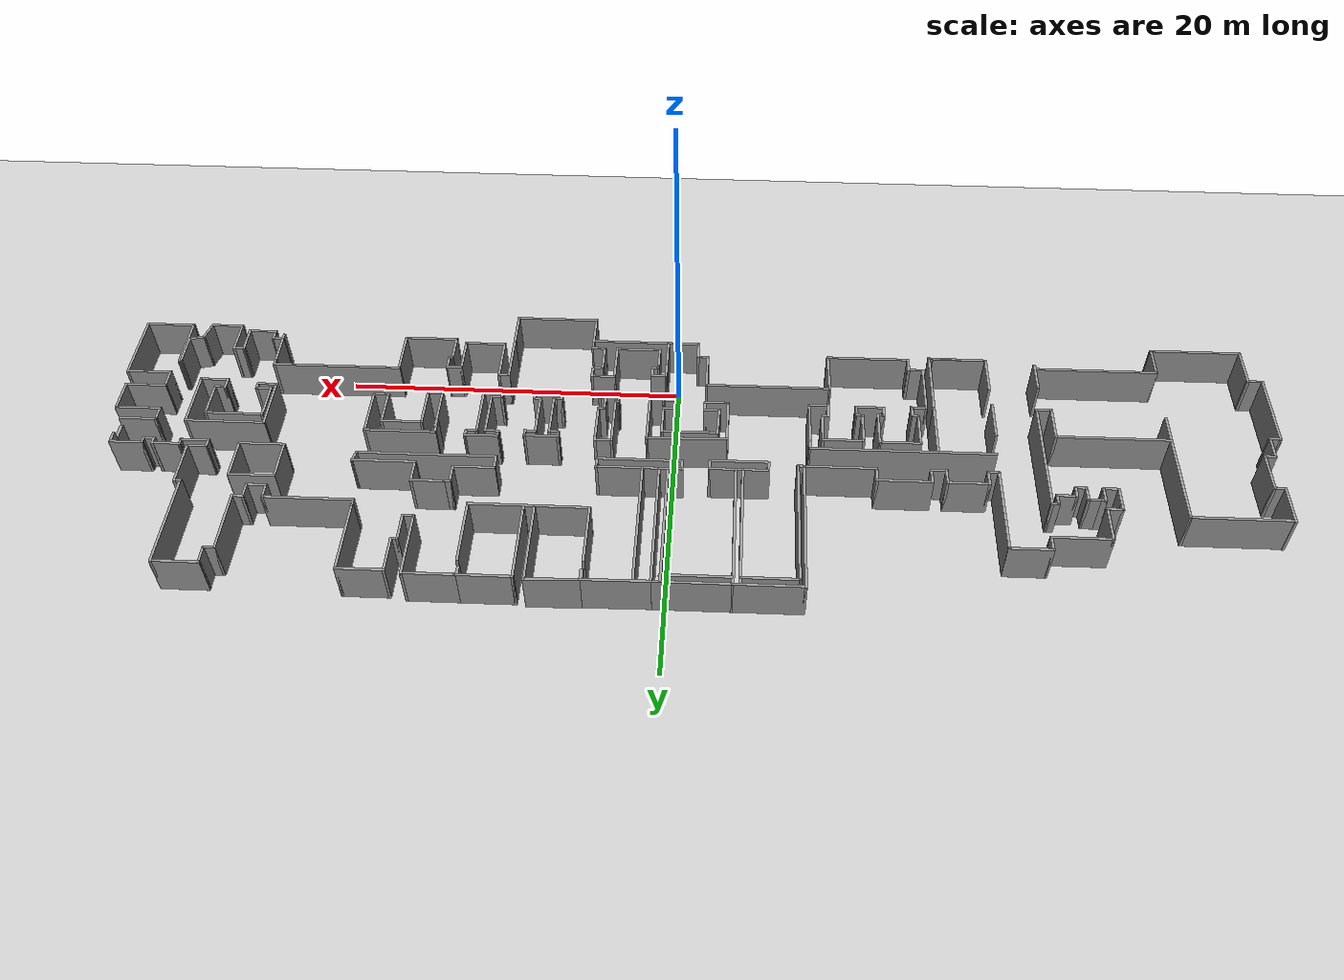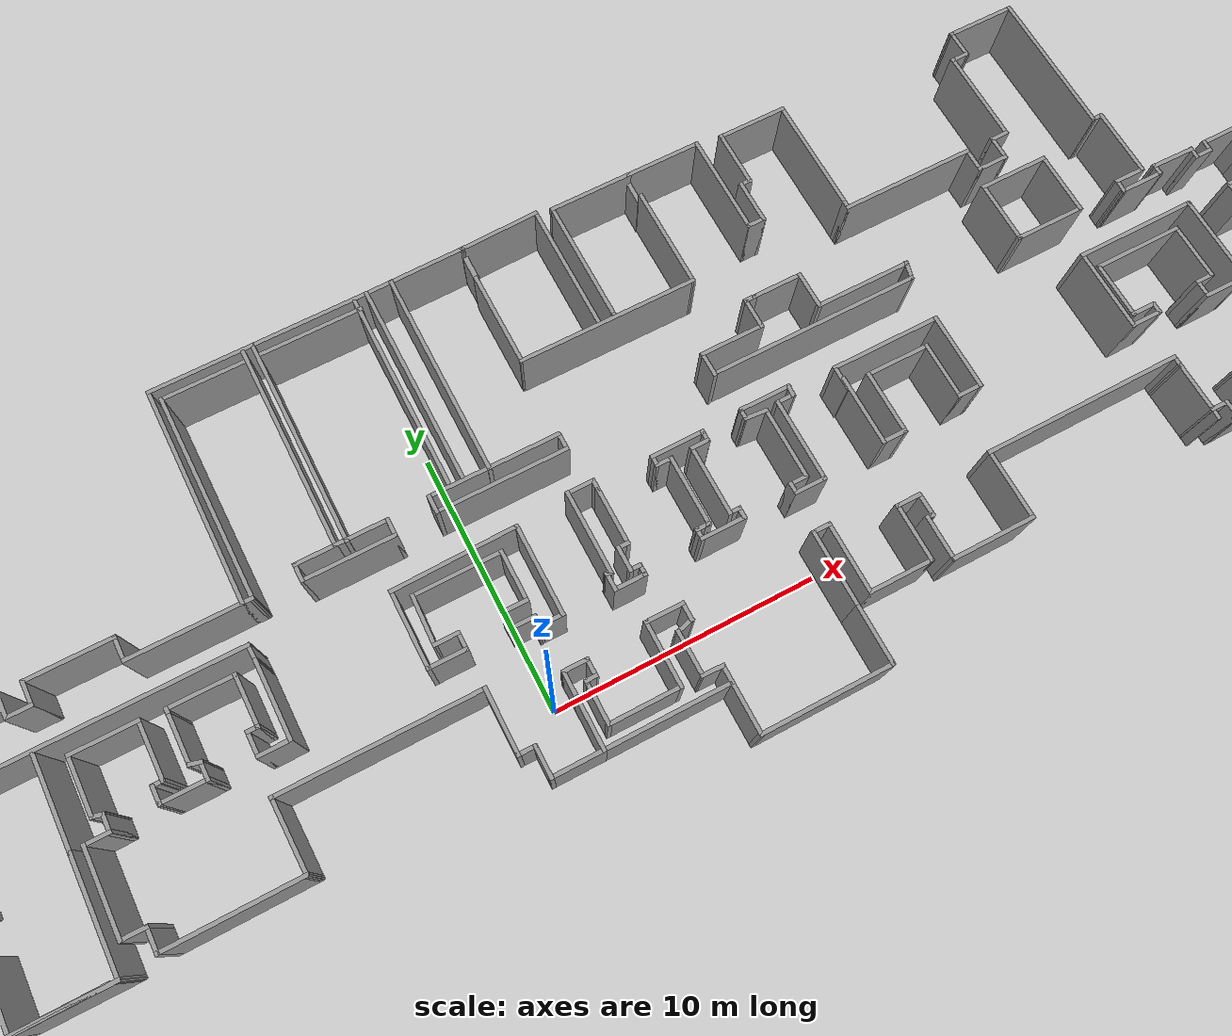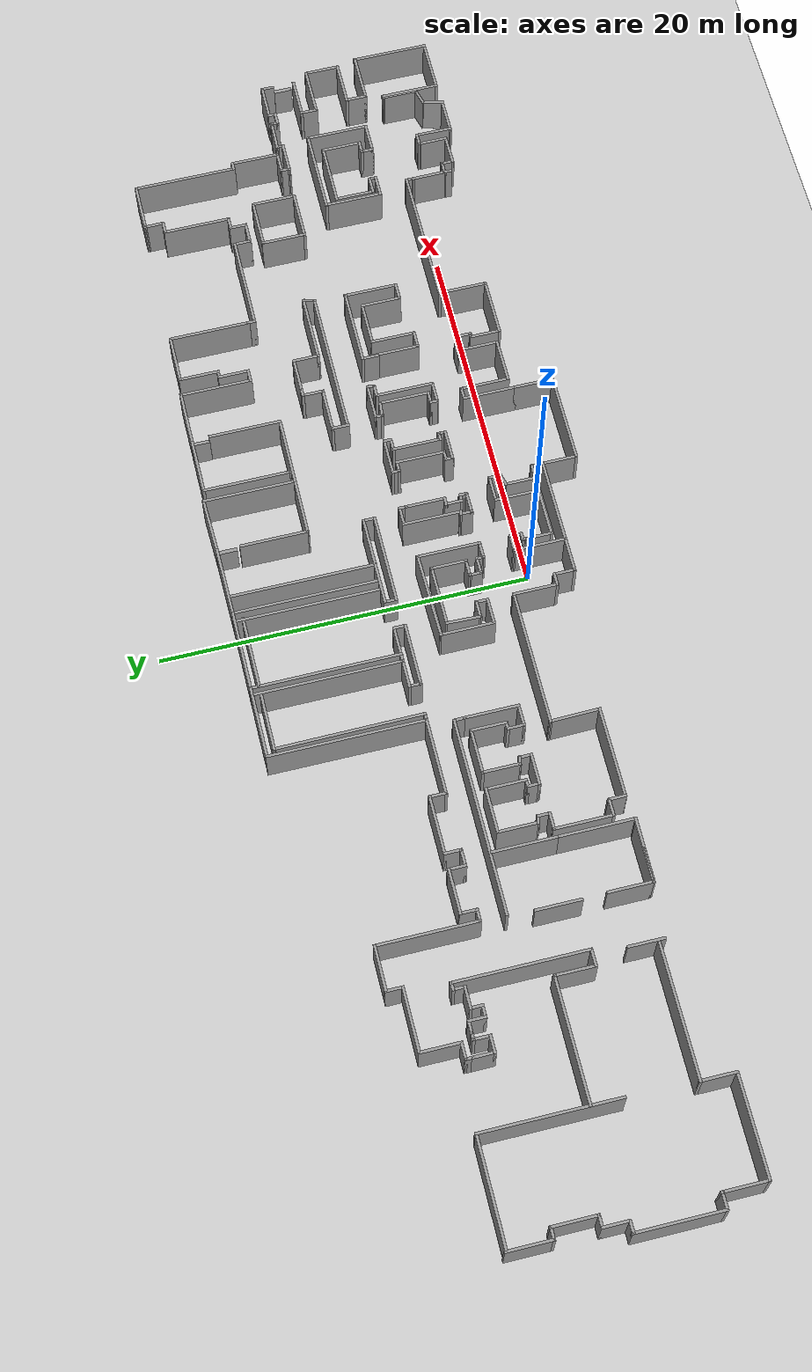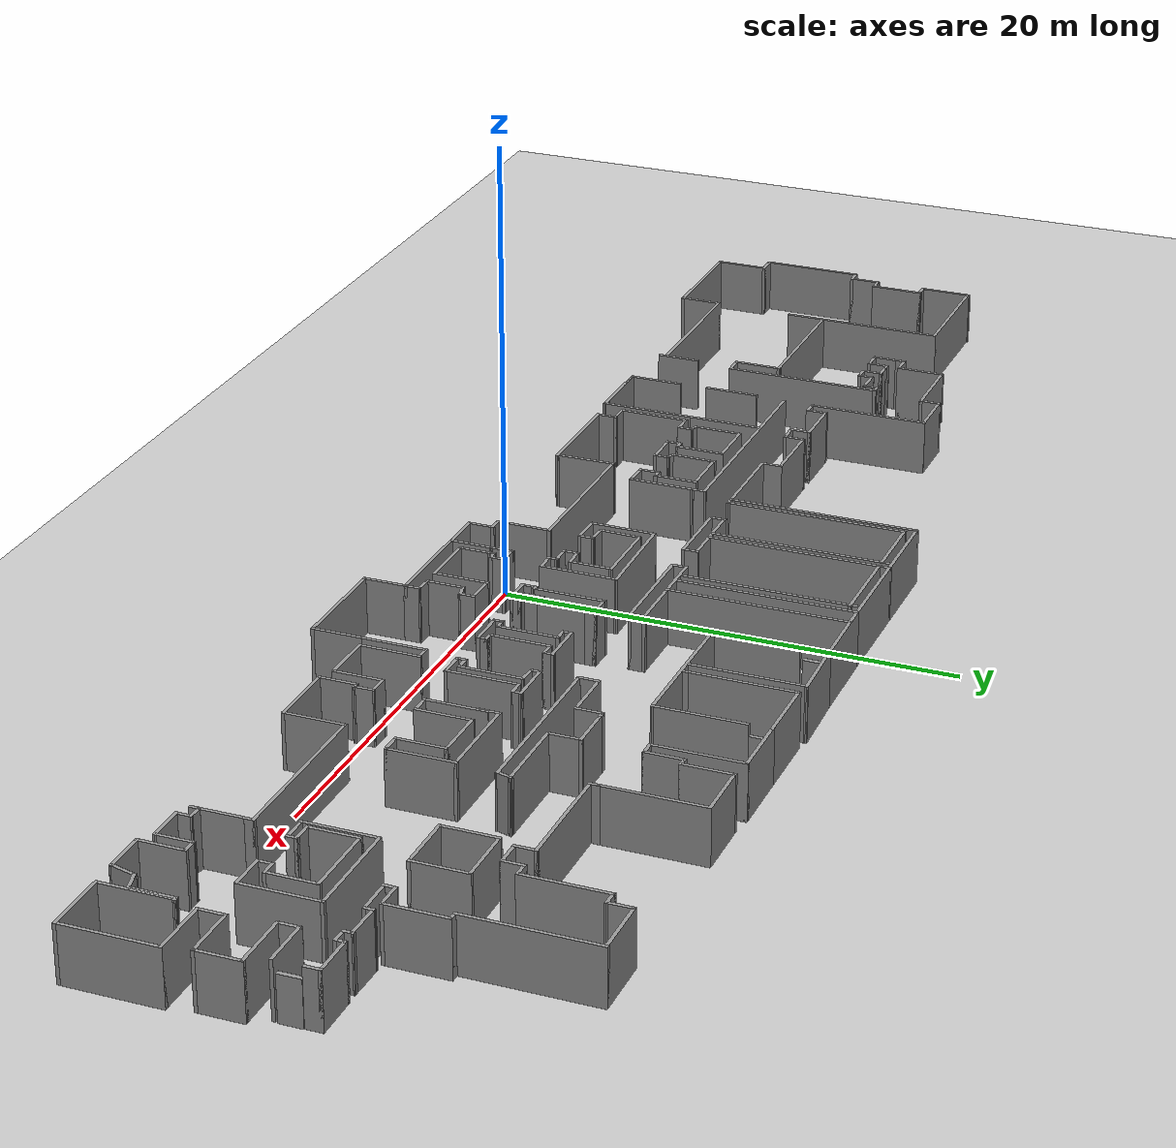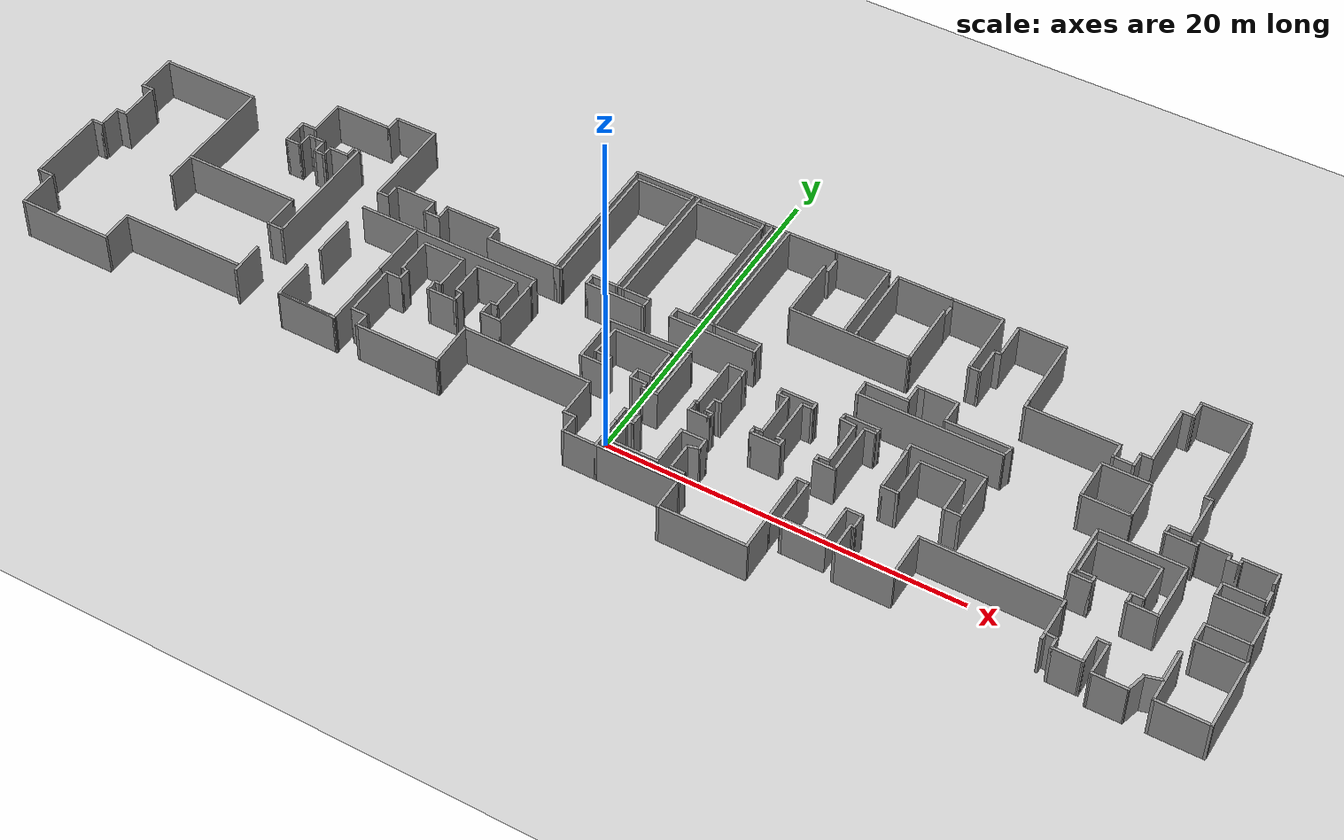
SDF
<?xml version='1.0'?>
<sdf version='1.7'>

  <world name="default">

    <!-- Add Physics Engine -->
    <physics name="default_physics" type="ode">
      <max_step_size>0.001</max_step_size>
      <real_time_factor>1</real_time_factor>
      <real_time_update_rate>1000</real_time_update_rate>
      <gravity>0 0 -9.81</gravity>
    </physics>

        <!-- Add the Ground Plane -->
    <model name="ground_plane">
      <static>1</static>
      <link name="link">
        <collision name="collision">
          <geometry>
            <plane>
              <normal>0 0 1</normal>
              <size>100 100</size>
            </plane>
          </geometry>
          <surface>
            <friction>
              <ode>
                <mu>100</mu>
                <mu2>50</mu2>
              </ode>
            </friction>
            <bounce/>
            <contact>
              <ode/>
            </contact>
          </surface>
          <max_contacts>10</max_contacts>
        </collision>
        <visual name="visual">
          <geometry>
            <plane>
              <normal>0 0 1</normal>
              <size>100 100</size>
            </plane>
          </geometry>
          <material>
            <script>
              <uri>file://media/materials/scripts/gazebo.material</uri>
              <name>Gazebo/Grey</name>
            </script>
          </material>
        </visual>
        <velocity_decay>
          <linear>0</linear>
          <angular>0</angular>
        </velocity_decay>
        <self_collide>0</self_collide>
        <kinematic>0</kinematic>
        <gravity>1</gravity>
      </link>
    </model>

  <model name='HandMade'>
    <pose>-0.902363 5.97176 0 0 -0 0</pose>
    <link name='Door_0'>
      <collision name='Door_0_Collision'>
        <geometry>
          <box>
            <size>0.957707 0.2 2</size>
          </box>
        </geometry>
        <pose>0 0 1 0 -0 0</pose>
      </collision>
      <visual name='Door_0_Visual'>
        <pose>0 0 1 0 -0 0</pose>
        <geometry>
          <box>
            <size>0.957707 0.2 2</size>
          </box>
        </geometry>
        <material>
          <script>
            <uri>file://media/materials/scripts/gazebo.material</uri>
            <name>Gazebo/Grey</name>
          </script>
        </material>
      </visual>
      <pose>5.38126 9.2915 0 0 -0 1.56978</pose>
    </link>
    <link name='Door_1'>
      <collision name='Door_1_Collision'>
        <geometry>
          <box>
            <size>0.9 0.17 2</size>
          </box>
        </geometry>
        <pose>0 0 1 0 -0 0</pose>
      </collision>
      <visual name='Door_1_Visual'>
        <pose>0 0 1 0 -0 0</pose>
        <geometry>
          <box>
            <size>0.9 0.17 2</size>
          </box>
        </geometry>
        <material>
          <script>
            <uri>file://media/materials/scripts/gazebo.material</uri>
            <name>Gazebo/Grey</name>
          </script>
        </material>
      </visual>
      <pose>12.0346 9.32077 0 0 -0 -1.58398</pose>
    </link>
    <link name='Door_2'>
      <collision name='Door_2_Collision'>
        <geometry>
          <box>
            <size>0.996178 0.2 2</size>
          </box>
        </geometry>
        <pose>0 0 1 0 -0 0</pose>
      </collision>
      <visual name='Door_2_Visual'>
        <pose>0 0 1 0 -0 0</pose>
        <geometry>
          <box>
            <size>0.996178 0.2 2</size>
          </box>
        </geometry>
        <material>
          <script>
            <uri>file://media/materials/scripts/gazebo.material</uri>
            <name>Gazebo/Grey</name>
          </script>
        </material>
      </visual>
      <pose>33.3267 0.090057 0 0 -0 1.57423</pose>
    </link>
    <link name='Wall_10'>
      <collision name='Wall_10_Collision'>
        <geometry>
          <box>
            <size>7.5 0.15 2.5</size>
          </box>
        </geometry>
        <pose>0 0 1.25 0 -0 0</pose>
      </collision>
      <visual name='Wall_10_Visual'>
        <pose>0 0 1.25 0 -0 0</pose>
        <geometry>
          <box>
            <size>7.5 0.15 2.5</size>
          </box>
        </geometry>
        <material>
          <script>
            <uri>file://media/materials/scripts/gazebo.material</uri>
            <name>Gazebo/Grey</name>
          </script>
          <ambient>1 1 1 1</ambient>
        </material>
        <meta>
          <layer>0</layer>
        </meta>
      </visual>
      <pose>-27.7593 0.603409 0 0 -0 -1.5708</pose>
    </link>
    <link name='Wall_101'>
      <collision name='Wall_101_Collision'>
        <geometry>
          <box>
            <size>3.90502 0.15 2.5</size>
          </box>
        </geometry>
        <pose>0 0 1.25 0 -0 0</pose>
      </collision>
      <visual name='Wall_101_Visual'>
        <pose>0 0 1.25 0 -0 0</pose>
        <geometry>
          <box>
            <size>3.90502 0.15 2.5</size>
          </box>
        </geometry>
        <material>
          <script>
            <uri>file://media/materials/scripts/gazebo.material</uri>
            <name>Gazebo/Grey</name>
          </script>
          <ambient>1 1 1 1</ambient>
        </material>
        <meta>
          <layer>0</layer>
        </meta>
      </visual>
      <pose>3.47392 9.84556 0 0 -0 0.011884</pose>
    </link>
    <link name='Wall_103'>
      <collision name='Wall_103_Collision'>
        <geometry>
          <box>
            <size>0.5 0.15 2.5</size>
          </box>
        </geometry>
        <pose>0 0 1.25 0 -0 0</pose>
      </collision>
      <visual name='Wall_103_Visual'>
        <pose>0 0 1.25 0 -0 0</pose>
        <geometry>
          <box>
            <size>0.5 0.15 2.5</size>
          </box>
        </geometry>
        <material>
          <script>
            <uri>file://media/materials/scripts/gazebo.material</uri>
            <name>Gazebo/Grey</name>
          </script>
          <ambient>1 1 1 1</ambient>
        </material>
        <meta>
          <layer>0</layer>
        </meta>
      </visual>
      <pose>-6.42846 1.47324 0 0 -0 0</pose>
    </link>
    <link name='Wall_104'>
      <collision name='Wall_104_Collision'>
        <geometry>
          <box>
            <size>8.05295 0.15 2.5</size>
          </box>
        </geometry>
        <pose>0 0 1.25 0 -0 0</pose>
      </collision>
      <visual name='Wall_104_Visual'>
        <pose>0 0 1.25 0 -0 0</pose>
        <geometry>
          <box>
            <size>8.05295 0.15 2.5</size>
          </box>
        </geometry>
        <material>
          <script>
            <uri>file://media/materials/scripts/gazebo.material</uri>
            <name>Gazebo/Grey</name>
          </script>
          <ambient>1 1 1 1</ambient>
        </material>
        <meta>
          <layer>0</layer>
        </meta>
      </visual>
      <pose>-6.27869 5.42464 0 0 -0 1.57718</pose>
    </link>
    <link name='Wall_105'>
      <collision name='Wall_105_Collision'>
        <geometry>
          <box>
            <size>3.25 0.15 2.5</size>
          </box>
        </geometry>
        <pose>0 0 1.25 0 -0 0</pose>
      </collision>
      <visual name='Wall_105_Visual'>
        <pose>0 0 1.25 0 -0 0</pose>
        <geometry>
          <box>
            <size>3.25 0.15 2.5</size>
          </box>
        </geometry>
        <material>
          <script>
            <uri>file://media/materials/scripts/gazebo.material</uri>
            <name>Gazebo/Grey</name>
          </script>
          <ambient>1 1 1 1</ambient>
        </material>
        <meta>
          <layer>0</layer>
        </meta>
      </visual>
      <pose>-4.75392 9.37603 0 0 -0 0</pose>
    </link>
    <link name='Wall_107'>
      <collision name='Wall_107_Collision'>
        <geometry>
          <box>
            <size>4 0.15 2.5</size>
          </box>
        </geometry>
        <pose>0 0 1.25 0 -0 0</pose>
      </collision>
      <visual name='Wall_107_Visual'>
        <pose>0 0 1.25 0 -0 0</pose>
        <geometry>
          <box>
            <size>4 0.15 2.5</size>
          </box>
        </geometry>
        <material>
          <script>
            <uri>file://media/materials/scripts/gazebo.material</uri>
            <name>Gazebo/Grey</name>
          </script>
          <ambient>1 1 1 1</ambient>
        </material>
        <meta>
          <layer>0</layer>
        </meta>
      </visual>
      <pose>-0.770391 9.37611 0 0 -0 0</pose>
    </link>
    <link name='Wall_112'>
      <collision name='Wall_112_Collision'>
        <geometry>
          <box>
            <size>6.91303 0.15 2.5</size>
          </box>
        </geometry>
        <pose>0 0 1.25 0 -0 0</pose>
      </collision>
      <visual name='Wall_112_Visual'>
        <pose>0 0 1.25 0 -0 0</pose>
        <geometry>
          <box>
            <size>6.91303 0.15 2.5</size>
          </box>
        </geometry>
        <material>
          <script>
            <uri>file://media/materials/scripts/gazebo.material</uri>
            <name>Gazebo/Grey</name>
          </script>
          <ambient>1 1 1 1</ambient>
        </material>
        <meta>
          <layer>0</layer>
        </meta>
      </visual>
      <pose>8.66504 4.98237 0 0 -0 -0.002699</pose>
    </link>
    <link name='Wall_114'>
      <collision name='Wall_114_Collision'>
        <geometry>
          <box>
            <size>3.25 0.15 2.5</size>
          </box>
        </geometry>
        <pose>0 0 1.25 0 -0 0</pose>
      </collision>
      <visual name='Wall_114_Visual'>
        <pose>0 0 1.25 0 -0 0</pose>
        <geometry>
          <box>
            <size>3.25 0.15 2.5</size>
          </box>
        </geometry>
        <material>
          <script>
            <uri>file://media/materials/scripts/gazebo.material</uri>
            <name>Gazebo/Grey</name>
          </script>
          <ambient>1 1 1 1</ambient>
        </material>
        <meta>
          <layer>0</layer>
        </meta>
      </visual>
      <pose>10.4965 9.82324 0 0 -0 3.14159</pose>
    </link>
    <link name='Wall_115'>
      <collision name='Wall_115_Collision'>
        <geometry>
          <box>
            <size>4.75 0.15 2.5</size>
          </box>
        </geometry>
        <pose>0 0 1.25 0 -0 0</pose>
      </collision>
      <visual name='Wall_115_Visual'>
        <pose>0 0 1.25 0 -0 0</pose>
        <geometry>
          <box>
            <size>4.75 0.15 2.5</size>
          </box>
        </geometry>
        <material>
          <script>
            <uri>file://media/materials/scripts/gazebo.material</uri>
            <name>Gazebo/Grey</name>
          </script>
          <ambient>1 1 1 1</ambient>
        </material>
        <meta>
          <layer>0</layer>
        </meta>
      </visual>
      <pose>8.94654 7.52324 0 0 -0 -1.5708</pose>
    </link>
    <link name='Wall_116'>
      <collision name='Wall_116_Collision'>
        <geometry>
          <box>
            <size>0.25 0.15 2.5</size>
          </box>
        </geometry>
        <pose>0 0 1.25 0 -0 0</pose>
      </collision>
      <visual name='Wall_116_Visual'>
        <pose>0 0 1.25 0 -0 0</pose>
        <geometry>
          <box>
            <size>0.25 0.15 2.5</size>
          </box>
        </geometry>
        <material>
          <script>
            <uri>file://media/materials/scripts/gazebo.material</uri>
            <name>Gazebo/Grey</name>
          </script>
          <ambient>1 1 1 1</ambient>
        </material>
        <meta>
          <layer>0</layer>
        </meta>
      </visual>
      <pose>8.94654 5.17324 0 0 -0 -1.5708</pose>
    </link>
    <link name='Wall_118'>
      <collision name='Wall_118_Collision'>
        <geometry>
          <box>
            <size>3.13479 0.15 2.5</size>
          </box>
        </geometry>
        <pose>0 0 1.25 0 -0 0</pose>
      </collision>
      <visual name='Wall_118_Visual'>
        <pose>0 0 1.25 0 -0 0</pose>
        <geometry>
          <box>
            <size>3.13479 0.15 2.5</size>
          </box>
        </geometry>
        <material>
          <script>
            <uri>file://media/materials/scripts/gazebo.material</uri>
            <name>Gazebo/Grey</name>
          </script>
          <ambient>1 1 1 1</ambient>
        </material>
        <meta>
          <layer>0</layer>
        </meta>
      </visual>
      <pose>6.84327 9.91326 0 0 -0 0.030417</pose>
    </link>
    <link name='Wall_119'>
      <collision name='Wall_119_Collision'>
        <geometry>
          <box>
            <size>5 0.15 2.5</size>
          </box>
        </geometry>
        <pose>0 0 1.25 0 -0 0</pose>
      </collision>
      <visual name='Wall_119_Visual'>
        <pose>0 0 1.25 0 -0 0</pose>
        <geometry>
          <box>
            <size>5 0.15 2.5</size>
          </box>
        </geometry>
        <material>
          <script>
            <uri>file://media/materials/scripts/gazebo.material</uri>
            <name>Gazebo/Grey</name>
          </script>
          <ambient>1 1 1 1</ambient>
        </material>
        <meta>
          <layer>0</layer>
        </meta>
      </visual>
      <pose>8.33523 7.51431 0 0 -0 -1.5708</pose>
    </link>
    <link name='Wall_12'>
      <collision name='Wall_12_Collision'>
        <geometry>
          <box>
            <size>6.75 0.15 2.5</size>
          </box>
        </geometry>
        <pose>0 0 1.25 0 -0 0</pose>
      </collision>
      <visual name='Wall_12_Visual'>
        <pose>0 0 1.25 0 -0 0</pose>
        <geometry>
          <box>
            <size>6.75 0.15 2.5</size>
          </box>
        </geometry>
        <material>
          <script>
            <uri>file://media/materials/scripts/gazebo.material</uri>
            <name>Gazebo/Grey</name>
          </script>
          <ambient>1 1 1 1</ambient>
        </material>
        <meta>
          <layer>0</layer>
        </meta>
      </visual>
      <pose>-24.4493 -1.37659 0 0 -0 0</pose>
    </link>
    <link name='Wall_121'>
      <collision name='Wall_121_Collision'>
        <geometry>
          <box>
            <size>3.75 0.15 2.5</size>
          </box>
        </geometry>
        <pose>0 0 1.25 0 -0 0</pose>
      </collision>
      <visual name='Wall_121_Visual'>
        <pose>0 0 1.25 0 -0 0</pose>
        <geometry>
          <box>
            <size>3.75 0.15 2.5</size>
          </box>
        </geometry>
        <material>
          <script>
            <uri>file://media/materials/scripts/gazebo.material</uri>
            <name>Gazebo/Grey</name>
          </script>
          <ambient>1 1 1 1</ambient>
        </material>
        <meta>
          <layer>0</layer>
        </meta>
      </visual>
      <pose>5.28354 6.7915 0 0 -0 1.5708</pose>
    </link>
    <link name='Wall_123'>
      <collision name='Wall_123_Collision'>
        <geometry>
          <box>
            <size>4 0.15 2.5</size>
          </box>
        </geometry>
        <pose>0 0 1.25 0 -0 0</pose>
      </collision>
      <visual name='Wall_123_Visual'>
        <pose>0 0 1.25 0 -0 0</pose>
        <geometry>
          <box>
            <size>4 0.15 2.5</size>
          </box>
        </geometry>
        <material>
          <script>
            <uri>file://media/materials/scripts/gazebo.material</uri>
            <name>Gazebo/Grey</name>
          </script>
          <ambient>1 1 1 1</ambient>
        </material>
        <meta>
          <layer>0</layer>
        </meta>
      </visual>
      <pose>12.0465 6.89824 0 0 -0 1.5708</pose>
    </link>
    <link name='Wall_125'>
      <collision name='Wall_125_Collision'>
        <geometry>
          <box>
            <size>3 0.15 2.5</size>
          </box>
        </geometry>
        <pose>0 0 1.25 0 -0 0</pose>
      </collision>
      <visual name='Wall_125_Visual'>
        <pose>0 0 1.25 0 -0 0</pose>
        <geometry>
          <box>
            <size>3 0.15 2.5</size>
          </box>
        </geometry>
        <material>
          <script>
            <uri>file://media/materials/scripts/gazebo.material</uri>
            <name>Gazebo/Grey</name>
          </script>
          <ambient>1 1 1 1</ambient>
        </material>
        <meta>
          <layer>0</layer>
        </meta>
      </visual>
      <pose>13.4715 9.82324 0 0 -0 0</pose>
    </link>
    <link name='Wall_126'>
      <collision name='Wall_126_Collision'>
        <geometry>
          <box>
            <size>4 0.15 2.5</size>
          </box>
        </geometry>
        <pose>0 0 1.25 0 -0 0</pose>
      </collision>
      <visual name='Wall_126_Visual'>
        <pose>0 0 1.25 0 -0 0</pose>
        <geometry>
          <box>
            <size>4 0.15 2.5</size>
          </box>
        </geometry>
        <material>
          <script>
            <uri>file://media/materials/scripts/gazebo.material</uri>
            <name>Gazebo/Grey</name>
          </script>
          <ambient>1 1 1 1</ambient>
        </material>
        <meta>
          <layer>0</layer>
        </meta>
      </visual>
      <pose>14.8965 7.89824 0 0 -0 -1.5708</pose>
    </link>
    <link name='Wall_127'>
      <collision name='Wall_127_Collision'>
        <geometry>
          <box>
            <size>0.75 0.15 2.5</size>
          </box>
        </geometry>
        <pose>0 0 1.25 0 -0 0</pose>
      </collision>
      <visual name='Wall_127_Visual'>
        <pose>0 0 1.25 0 -0 0</pose>
        <geometry>
          <box>
            <size>0.75 0.15 2.5</size>
          </box>
        </geometry>
        <material>
          <script>
            <uri>file://media/materials/scripts/gazebo.material</uri>
            <name>Gazebo/Grey</name>
          </script>
          <ambient>1 1 1 1</ambient>
        </material>
        <meta>
          <layer>0</layer>
        </meta>
      </visual>
      <pose>15.1965 5.97324 0 0 -0 0</pose>
    </link>
    <link name='Wall_128'>
      <collision name='Wall_128_Collision'>
        <geometry>
          <box>
            <size>1.75 0.15 2.5</size>
          </box>
        </geometry>
        <pose>0 0 1.25 0 -0 0</pose>
      </collision>
      <visual name='Wall_128_Visual'>
        <pose>0 0 1.25 0 -0 0</pose>
        <geometry>
          <box>
            <size>1.75 0.15 2.5</size>
          </box>
        </geometry>
        <material>
          <script>
            <uri>file://media/materials/scripts/gazebo.material</uri>
            <name>Gazebo/Grey</name>
          </script>
          <ambient>1 1 1 1</ambient>
        </material>
        <meta>
          <layer>0</layer>
        </meta>
      </visual>
      <pose>15.4965 6.77324 0 0 -0 1.5708</pose>
    </link>
    <link name='Wall_129'>
      <collision name='Wall_129_Collision'>
        <geometry>
          <box>
            <size>0.5 0.15 2.5</size>
          </box>
        </geometry>
        <pose>0 0 1.25 0 -0 0</pose>
      </collision>
      <visual name='Wall_129_Visual'>
        <pose>0 0 1.25 0 -0 0</pose>
        <geometry>
          <box>
            <size>0.5 0.15 2.5</size>
          </box>
        </geometry>
        <material>
          <script>
            <uri>file://media/materials/scripts/gazebo.material</uri>
            <name>Gazebo/Grey</name>
          </script>
          <ambient>1 1 1 1</ambient>
        </material>
        <meta>
          <layer>0</layer>
        </meta>
      </visual>
      <pose>15.6715 7.57324 0 0 -0 0</pose>
    </link>
    <link name='Wall_13'>
      <collision name='Wall_13_Collision'>
        <geometry>
          <box>
            <size>2.25 0.15 2.5</size>
          </box>
        </geometry>
        <pose>0 0 1.25 0 -0 0</pose>
      </collision>
      <visual name='Wall_13_Visual'>
        <pose>0 0 1.25 0 -0 0</pose>
        <geometry>
          <box>
            <size>2.25 0.15 2.5</size>
          </box>
        </geometry>
        <material>
          <script>
            <uri>file://media/materials/scripts/gazebo.material</uri>
            <name>Gazebo/Grey</name>
          </script>
          <ambient>1 1 1 1</ambient>
        </material>
        <meta>
          <layer>0</layer>
        </meta>
      </visual>
      <pose>-21.1493 -2.42659 0 0 -0 -1.5708</pose>
    </link>
    <link name='Wall_130'>
      <collision name='Wall_130_Collision'>
        <geometry>
          <box>
            <size>2.25 0.15 2.5</size>
          </box>
        </geometry>
        <pose>0 0 1.25 0 -0 0</pose>
      </collision>
      <visual name='Wall_130_Visual'>
        <pose>0 0 1.25 0 -0 0</pose>
        <geometry>
          <box>
            <size>2.25 0.15 2.5</size>
          </box>
        </geometry>
        <material>
          <script>
            <uri>file://media/materials/scripts/gazebo.material</uri>
            <name>Gazebo/Grey</name>
          </script>
          <ambient>1 1 1 1</ambient>
        </material>
        <meta>
          <layer>0</layer>
        </meta>
      </visual>
      <pose>15.8465 8.62325 0 0 -0 1.5708</pose>
    </link>
    <link name='Wall_131'>
      <collision name='Wall_131_Collision'>
        <geometry>
          <box>
            <size>2.75 0.15 2.5</size>
          </box>
        </geometry>
        <pose>0 0 1.25 0 -0 0</pose>
      </collision>
      <visual name='Wall_131_Visual'>
        <pose>0 0 1.25 0 -0 0</pose>
        <geometry>
          <box>
            <size>2.75 0.15 2.5</size>
          </box>
        </geometry>
        <material>
          <script>
            <uri>file://media/materials/scripts/gazebo.material</uri>
            <name>Gazebo/Grey</name>
          </script>
          <ambient>1 1 1 1</ambient>
        </material>
        <meta>
          <layer>0</layer>
        </meta>
      </visual>
      <pose>17.1465 9.67324 0 0 -0 0</pose>
    </link>
    <link name='Wall_132'>
      <collision name='Wall_132_Collision'>
        <geometry>
          <box>
            <size>4.5 0.15 2.5</size>
          </box>
        </geometry>
        <pose>0 0 1.25 0 -0 0</pose>
      </collision>
      <visual name='Wall_132_Visual'>
        <pose>0 0 1.25 0 -0 0</pose>
        <geometry>
          <box>
            <size>4.5 0.15 2.5</size>
          </box>
        </geometry>
        <material>
          <script>
            <uri>file://media/materials/scripts/gazebo.material</uri>
            <name>Gazebo/Grey</name>
          </script>
          <ambient>1 1 1 1</ambient>
        </material>
        <meta>
          <layer>0</layer>
        </meta>
      </visual>
      <pose>18.4465 7.49824 0 0 -0 -1.5708</pose>
    </link>
    <link name='Wall_134'>
      <collision name='Wall_134_Collision'>
        <geometry>
          <box>
            <size>0.5 0.15 2.5</size>
          </box>
        </geometry>
        <pose>0 0 1.25 0 -0 0</pose>
      </collision>
      <visual name='Wall_134_Visual'>
        <pose>0 0 1.25 0 -0 0</pose>
        <geometry>
          <box>
            <size>0.5 0.15 2.5</size>
          </box>
        </geometry>
        <material>
          <script>
            <uri>file://media/materials/scripts/gazebo.material</uri>
            <name>Gazebo/Grey</name>
          </script>
          <ambient>1 1 1 1</ambient>
        </material>
        <meta>
          <layer>0</layer>
        </meta>
      </visual>
      <pose>18.4465 5.14824 0 0 -0 -1.5708</pose>
    </link>
    <link name='Wall_135'>
      <collision name='Wall_135_Collision'>
        <geometry>
          <box>
            <size>5.25 0.15 2.5</size>
          </box>
        </geometry>
        <pose>0 0 1.25 0 -0 0</pose>
      </collision>
      <visual name='Wall_135_Visual'>
        <pose>0 0 1.25 0 -0 0</pose>
        <geometry>
          <box>
            <size>5.25 0.15 2.5</size>
          </box>
        </geometry>
        <material>
          <script>
            <uri>file://media/materials/scripts/gazebo.material</uri>
            <name>Gazebo/Grey</name>
          </script>
          <ambient>1 1 1 1</ambient>
        </material>
        <meta>
          <layer>0</layer>
        </meta>
      </visual>
      <pose>20.9965 4.97324 0 0 -0 0</pose>
    </link>
    <link name='Wall_136'>
      <collision name='Wall_136_Collision'>
        <geometry>
          <box>
            <size>1 0.15 2.5</size>
          </box>
        </geometry>
        <pose>0 0 1.25 0 -0 0</pose>
      </collision>
      <visual name='Wall_136_Visual'>
        <pose>0 0 1.25 0 -0 0</pose>
        <geometry>
          <box>
            <size>1 0.15 2.5</size>
          </box>
        </geometry>
        <material>
          <script>
            <uri>file://media/materials/scripts/gazebo.material</uri>
            <name>Gazebo/Grey</name>
          </script>
          <ambient>1 1 1 1</ambient>
        </material>
        <meta>
          <layer>0</layer>
        </meta>
      </visual>
      <pose>23.5465 4.54824 0 0 -0 -1.5708</pose>
    </link>
    <link name='Wall_137'>
      <collision name='Wall_137_Collision'>
        <geometry>
          <box>
            <size>1.25 0.15 2.5</size>
          </box>
        </geometry>
        <pose>0 0 1.25 0 -0 0</pose>
      </collision>
      <visual name='Wall_137_Visual'>
        <pose>0 0 1.25 0 -0 0</pose>
        <geometry>
          <box>
            <size>1.25 0.15 2.5</size>
          </box>
        </geometry>
        <material>
          <script>
            <uri>file://media/materials/scripts/gazebo.material</uri>
            <name>Gazebo/Grey</name>
          </script>
          <ambient>1 1 1 1</ambient>
        </material>
        <meta>
          <layer>0</layer>
        </meta>
      </visual>
      <pose>24.0965 4.12324 0 0 -0 0</pose>
    </link>
    <link name='Wall_138'>
      <collision name='Wall_138_Collision'>
        <geometry>
          <box>
            <size>1 0.15 2.5</size>
          </box>
        </geometry>
        <pose>0 0 1.25 0 -0 0</pose>
      </collision>
      <visual name='Wall_138_Visual'>
        <pose>0 0 1.25 0 -0 0</pose>
        <geometry>
          <box>
            <size>1 0.15 2.5</size>
          </box>
        </geometry>
        <material>
          <script>
            <uri>file://media/materials/scripts/gazebo.material</uri>
            <name>Gazebo/Grey</name>
          </script>
          <ambient>1 1 1 1</ambient>
        </material>
        <meta>
          <layer>0</layer>
        </meta>
      </visual>
      <pose>24.6465 4.54824 0 0 -0 1.5708</pose>
    </link>
    <link name='Wall_139'>
      <collision name='Wall_139_Collision'>
        <geometry>
          <box>
            <size>0.75 0.15 2.5</size>
          </box>
        </geometry>
        <pose>0 0 1.25 0 -0 0</pose>
      </collision>
      <visual name='Wall_139_Visual'>
        <pose>0 0 1.25 0 -0 0</pose>
        <geometry>
          <box>
            <size>0.75 0.15 2.5</size>
          </box>
        </geometry>
        <material>
          <script>
            <uri>file://media/materials/scripts/gazebo.material</uri>
            <name>Gazebo/Grey</name>
          </script>
          <ambient>1 1 1 1</ambient>
        </material>
        <meta>
          <layer>0</layer>
        </meta>
      </visual>
      <pose>24.9465 4.97324 0 0 -0 0</pose>
    </link>
    <link name='Wall_14'>
      <collision name='Wall_14_Collision'>
        <geometry>
          <box>
            <size>1 0.15 2.5</size>
          </box>
        </geometry>
        <pose>0 0 1.25 0 -0 0</pose>
      </collision>
      <visual name='Wall_14_Visual'>
        <pose>0 0 1.25 0 -0 0</pose>
        <geometry>
          <box>
            <size>1 0.15 2.5</size>
          </box>
        </geometry>
        <material>
          <script>
            <uri>file://media/materials/scripts/gazebo.material</uri>
            <name>Gazebo/Grey</name>
          </script>
          <ambient>1 1 1 1</ambient>
        </material>
        <meta>
          <layer>0</layer>
        </meta>
      </visual>
      <pose>-20.7243 -3.47659 0 0 -0 0</pose>
    </link>
    <link name='Wall_140'>
      <collision name='Wall_140_Collision'>
        <geometry>
          <box>
            <size>3.75 0.15 2.5</size>
          </box>
        </geometry>
        <pose>0 0 1.25 0 -0 0</pose>
      </collision>
      <visual name='Wall_140_Visual'>
        <pose>0 0 1.25 0 -0 0</pose>
        <geometry>
          <box>
            <size>3.75 0.15 2.5</size>
          </box>
        </geometry>
        <material>
          <script>
            <uri>file://media/materials/scripts/gazebo.material</uri>
            <name>Gazebo/Grey</name>
          </script>
          <ambient>1 1 1 1</ambient>
        </material>
        <meta>
          <layer>0</layer>
        </meta>
      </visual>
      <pose>25.2465 6.77324 0 0 -0 1.5708</pose>
    </link>
    <link name='Wall_141'>
      <collision name='Wall_141_Collision'>
        <geometry>
          <box>
            <size>0.75 0.15 2.5</size>
          </box>
        </geometry>
        <pose>0 0 1.25 0 -0 0</pose>
      </collision>
      <visual name='Wall_141_Visual'>
        <pose>0 0 1.25 0 -0 0</pose>
        <geometry>
          <box>
            <size>0.75 0.15 2.5</size>
          </box>
        </geometry>
        <material>
          <script>
            <uri>file://media/materials/scripts/gazebo.material</uri>
            <name>Gazebo/Grey</name>
          </script>
          <ambient>1 1 1 1</ambient>
        </material>
        <meta>
          <layer>0</layer>
        </meta>
      </visual>
      <pose>25.5465 8.57324 0 0 -0 0</pose>
    </link>
    <link name='Wall_142'>
      <collision name='Wall_142_Collision'>
        <geometry>
          <box>
            <size>1.15552 0.15 2.5</size>
          </box>
        </geometry>
        <pose>0 0 1.25 0 -0 0</pose>
      </collision>
      <visual name='Wall_142_Visual'>
        <pose>0 0 1.25 0 -0 0</pose>
        <geometry>
          <box>
            <size>1.15552 0.15 2.5</size>
          </box>
        </geometry>
        <material>
          <script>
            <uri>file://media/materials/scripts/gazebo.material</uri>
            <name>Gazebo/Grey</name>
          </script>
          <ambient>1 1 1 1</ambient>
        </material>
        <meta>
          <layer>0</layer>
        </meta>
      </visual>
      <pose>25.8412 9.07597 0 0 -0 1.58146</pose>
    </link>
    <link name='Wall_143'>
      <collision name='Wall_143_Collision'>
        <geometry>
          <box>
            <size>2.75 0.15 2.5</size>
          </box>
        </geometry>
        <pose>0 0 1.25 0 -0 0</pose>
      </collision>
      <visual name='Wall_143_Visual'>
        <pose>0 0 1.25 0 -0 0</pose>
        <geometry>
          <box>
            <size>2.75 0.15 2.5</size>
          </box>
        </geometry>
        <material>
          <script>
            <uri>file://media/materials/scripts/gazebo.material</uri>
            <name>Gazebo/Grey</name>
          </script>
          <ambient>1 1 1 1</ambient>
        </material>
        <meta>
          <layer>0</layer>
        </meta>
      </visual>
      <pose>27.1358 9.58597 0 0 -0 0</pose>
    </link>
    <link name='Wall_147'>
      <collision name='Wall_147_Collision'>
        <geometry>
          <box>
            <size>5.75 0.15 2.5</size>
          </box>
        </geometry>
        <pose>0 0 1.25 0 -0 0</pose>
      </collision>
      <visual name='Wall_147_Visual'>
        <pose>0 0 1.25 0 -0 0</pose>
        <geometry>
          <box>
            <size>5.75 0.15 2.5</size>
          </box>
        </geometry>
        <material>
          <script>
            <uri>file://media/materials/scripts/gazebo.material</uri>
            <name>Gazebo/Grey</name>
          </script>
          <ambient>1 1 1 1</ambient>
        </material>
        <meta>
          <layer>0</layer>
        </meta>
      </visual>
      <pose>28.4358 6.78597 0 0 -0 -1.5708</pose>
    </link>
    <link name='Wall_148'>
      <collision name='Wall_148_Collision'>
        <geometry>
          <box>
            <size>0.5 0.15 2.5</size>
          </box>
        </geometry>
        <pose>0 0 1.25 0 -0 0</pose>
      </collision>
      <visual name='Wall_148_Visual'>
        <pose>0 0 1.25 0 -0 0</pose>
        <geometry>
          <box>
            <size>0.5 0.15 2.5</size>
          </box>
        </geometry>
        <material>
          <script>
            <uri>file://media/materials/scripts/gazebo.material</uri>
            <name>Gazebo/Grey</name>
          </script>
          <ambient>1 1 1 1</ambient>
        </material>
        <meta>
          <layer>0</layer>
        </meta>
      </visual>
      <pose>28.6108 3.98597 0 0 -0 0</pose>
    </link>
    <link name='Wall_149'>
      <collision name='Wall_149_Collision'>
        <geometry>
          <box>
            <size>2.75 0.15 2.5</size>
          </box>
        </geometry>
        <pose>0 0 1.25 0 -0 0</pose>
      </collision>
      <visual name='Wall_149_Visual'>
        <pose>0 0 1.25 0 -0 0</pose>
        <geometry>
          <box>
            <size>2.75 0.15 2.5</size>
          </box>
        </geometry>
        <material>
          <script>
            <uri>file://media/materials/scripts/gazebo.material</uri>
            <name>Gazebo/Grey</name>
          </script>
          <ambient>1 1 1 1</ambient>
        </material>
        <meta>
          <layer>0</layer>
        </meta>
      </visual>
      <pose>28.7858 2.68597 0 0 -0 -1.5708</pose>
    </link>
    <link name='Wall_15'>
      <collision name='Wall_15_Collision'>
        <geometry>
          <box>
            <size>7.25 0.15 2.5</size>
          </box>
        </geometry>
        <pose>0 0 1.25 0 -0 0</pose>
      </collision>
      <visual name='Wall_15_Visual'>
        <pose>0 0 1.25 0 -0 0</pose>
        <geometry>
          <box>
            <size>7.25 0.15 2.5</size>
          </box>
        </geometry>
        <material>
          <script>
            <uri>file://media/materials/scripts/gazebo.material</uri>
            <name>Gazebo/Grey</name>
          </script>
          <ambient>1 1 1 1</ambient>
        </material>
        <meta>
          <layer>0</layer>
        </meta>
      </visual>
      <pose>-20.2993 0.073409 0 0 -0 1.5708</pose>
    </link>
    <link name='Wall_150'>
      <collision name='Wall_150_Collision'>
        <geometry>
          <box>
            <size>1.25 0.15 2.5</size>
          </box>
        </geometry>
        <pose>0 0 1.25 0 -0 0</pose>
      </collision>
      <visual name='Wall_150_Visual'>
        <pose>0 0 1.25 0 -0 0</pose>
        <geometry>
          <box>
            <size>1.25 0.15 2.5</size>
          </box>
        </geometry>
        <material>
          <script>
            <uri>file://media/materials/scripts/gazebo.material</uri>
            <name>Gazebo/Grey</name>
          </script>
          <ambient>1 1 1 1</ambient>
        </material>
        <meta>
          <layer>0</layer>
        </meta>
      </visual>
      <pose>28.2358 1.38597 0 0 -0 3.14159</pose>
    </link>
    <link name='Wall_151'>
      <collision name='Wall_151_Collision'>
        <geometry>
          <box>
            <size>0.584467 0.15 2.5</size>
          </box>
        </geometry>
        <pose>0 0 1.25 0 -0 0</pose>
      </collision>
      <visual name='Wall_151_Visual'>
        <pose>0 0 1.25 0 -0 0</pose>
        <geometry>
          <box>
            <size>0.584467 0.15 2.5</size>
          </box>
        </geometry>
        <material>
          <script>
            <uri>file://media/materials/scripts/gazebo.material</uri>
            <name>Gazebo/Grey</name>
          </script>
          <ambient>1 1 1 1</ambient>
        </material>
        <meta>
          <layer>0</layer>
        </meta>
      </visual>
      <pose>27.679 1.16885 0 0 -0 -1.60221</pose>
    </link>
    <link name='Wall_152'>
      <collision name='Wall_152_Collision'>
        <geometry>
          <box>
            <size>1.75 0.15 2.5</size>
          </box>
        </geometry>
        <pose>0 0 1.25 0 -0 0</pose>
      </collision>
      <visual name='Wall_152_Visual'>
        <pose>0 0 1.25 0 -0 0</pose>
        <geometry>
          <box>
            <size>1.75 0.15 2.5</size>
          </box>
        </geometry>
        <material>
          <script>
            <uri>file://media/materials/scripts/gazebo.material</uri>
            <name>Gazebo/Grey</name>
          </script>
          <ambient>1 1 1 1</ambient>
        </material>
        <meta>
          <layer>0</layer>
        </meta>
      </visual>
      <pose>28.4722 0.951722 0 0 -0 0</pose>
    </link>
    <link name='Wall_153'>
      <collision name='Wall_153_Collision'>
        <geometry>
          <box>
            <size>0.481171 0.15 2.5</size>
          </box>
        </geometry>
        <pose>0 0 1.25 0 -0 0</pose>
      </collision>
      <visual name='Wall_153_Visual'>
        <pose>0 0 1.25 0 -0 0</pose>
        <geometry>
          <box>
            <size>0.481171 0.15 2.5</size>
          </box>
        </geometry>
        <material>
          <script>
            <uri>file://media/materials/scripts/gazebo.material</uri>
            <name>Gazebo/Grey</name>
          </script>
          <ambient>1 1 1 1</ambient>
        </material>
        <meta>
          <layer>0</layer>
        </meta>
      </visual>
      <pose>29.2722 1.11731 0 0 -0 1.57041</pose>
    </link>
    <link name='Wall_154'>
      <collision name='Wall_154_Collision'>
        <geometry>
          <box>
            <size>1.75 0.15 2.5</size>
          </box>
        </geometry>
        <pose>0 0 1.25 0 -0 0</pose>
      </collision>
      <visual name='Wall_154_Visual'>
        <pose>0 0 1.25 0 -0 0</pose>
        <geometry>
          <box>
            <size>1.75 0.15 2.5</size>
          </box>
        </geometry>
        <material>
          <script>
            <uri>file://media/materials/scripts/gazebo.material</uri>
            <name>Gazebo/Grey</name>
          </script>
          <ambient>1 1 1 1</ambient>
        </material>
        <meta>
          <layer>0</layer>
        </meta>
      </visual>
      <pose>30.0723 1.26471 0 0 -0 -0.022723</pose>
    </link>
    <link name='Wall_155'>
      <collision name='Wall_155_Collision'>
        <geometry>
          <box>
            <size>0.5 0.15 2.5</size>
          </box>
        </geometry>
        <pose>0 0 1.25 0 -0 0</pose>
      </collision>
      <visual name='Wall_155_Visual'>
        <pose>0 0 1.25 0 -0 0</pose>
        <geometry>
          <box>
            <size>0.5 0.15 2.5</size>
          </box>
        </geometry>
        <material>
          <script>
            <uri>file://media/materials/scripts/gazebo.material</uri>
            <name>Gazebo/Grey</name>
          </script>
          <ambient>1 1 1 1</ambient>
        </material>
        <meta>
          <layer>0</layer>
        </meta>
      </visual>
      <pose>30.8723 1.08608 0 0 -0 -1.5708</pose>
    </link>
    <link name='Wall_159'>
      <collision name='Wall_159_Collision'>
        <geometry>
          <box>
            <size>0.75 0.15 2.5</size>
          </box>
        </geometry>
        <pose>0 0 1.25 0 -0 0</pose>
      </collision>
      <visual name='Wall_159_Visual'>
        <pose>0 0 1.25 0 -0 0</pose>
        <geometry>
          <box>
            <size>0.75 0.15 2.5</size>
          </box>
        </geometry>
        <material>
          <script>
            <uri>file://media/materials/scripts/gazebo.material</uri>
            <name>Gazebo/Grey</name>
          </script>
          <ambient>1 1 1 1</ambient>
        </material>
        <meta>
          <layer>0</layer>
        </meta>
      </visual>
      <pose>31.1723 0.911076 0 0 -0 0</pose>
    </link>
    <link name='Wall_160'>
      <collision name='Wall_160_Collision'>
        <geometry>
          <box>
            <size>0.5 0.15 2.5</size>
          </box>
        </geometry>
        <pose>0 0 1.25 0 -0 0</pose>
      </collision>
      <visual name='Wall_160_Visual'>
        <pose>0 0 1.25 0 -0 0</pose>
        <geometry>
          <box>
            <size>0.5 0.15 2.5</size>
          </box>
        </geometry>
        <material>
          <script>
            <uri>file://media/materials/scripts/gazebo.material</uri>
            <name>Gazebo/Grey</name>
          </script>
          <ambient>1 1 1 1</ambient>
        </material>
        <meta>
          <layer>0</layer>
        </meta>
      </visual>
      <pose>31.4723 1.08608 0 0 -0 1.5708</pose>
    </link>
    <link name='Wall_161'>
      <collision name='Wall_161_Collision'>
        <geometry>
          <box>
            <size>2 0.15 2.5</size>
          </box>
        </geometry>
        <pose>0 0 1.25 0 -0 0</pose>
      </collision>
      <visual name='Wall_161_Visual'>
        <pose>0 0 1.25 0 -0 0</pose>
        <geometry>
          <box>
            <size>2 0.15 2.5</size>
          </box>
        </geometry>
        <material>
          <script>
            <uri>file://media/materials/scripts/gazebo.material</uri>
            <name>Gazebo/Grey</name>
          </script>
          <ambient>1 1 1 1</ambient>
        </material>
        <meta>
          <layer>0</layer>
        </meta>
      </visual>
      <pose>32.3973 1.26108 0 0 -0 0</pose>
    </link>
    <link name='Wall_162'>
      <collision name='Wall_162_Collision'>
        <geometry>
          <box>
            <size>0.75 0.15 2.5</size>
          </box>
        </geometry>
        <pose>0 0 1.25 0 -0 0</pose>
      </collision>
      <visual name='Wall_162_Visual'>
        <pose>0 0 1.25 0 -0 0</pose>
        <geometry>
          <box>
            <size>0.75 0.15 2.5</size>
          </box>
        </geometry>
        <material>
          <script>
            <uri>file://media/materials/scripts/gazebo.material</uri>
            <name>Gazebo/Grey</name>
          </script>
          <ambient>1 1 1 1</ambient>
        </material>
        <meta>
          <layer>0</layer>
        </meta>
      </visual>
      <pose>33.3223 0.961076 0 0 -0 -1.5708</pose>
    </link>
    <link name='Wall_164'>
      <collision name='Wall_164_Collision'>
        <geometry>
          <box>
            <size>2.25 0.15 2.5</size>
          </box>
        </geometry>
        <pose>0 0 1.25 0 -0 0</pose>
      </collision>
      <visual name='Wall_164_Visual'>
        <pose>0 0 1.25 0 -0 0</pose>
        <geometry>
          <box>
            <size>2.25 0.15 2.5</size>
          </box>
        </geometry>
        <material>
          <script>
            <uri>file://media/materials/scripts/gazebo.material</uri>
            <name>Gazebo/Grey</name>
          </script>
          <ambient>1 1 1 1</ambient>
        </material>
        <meta>
          <layer>0</layer>
        </meta>
      </visual>
      <pose>32.2665 -0.573745 0 0 -0 0</pose>
    </link>
    <link name='Wall_166'>
      <collision name='Wall_166_Collision'>
        <geometry>
          <box>
            <size>1 0.15 2.5</size>
          </box>
        </geometry>
        <pose>0 0 1.25 0 -0 0</pose>
      </collision>
      <visual name='Wall_166_Visual'>
        <pose>0 0 1.25 0 -0 0</pose>
        <geometry>
          <box>
            <size>1 0.15 2.5</size>
          </box>
        </geometry>
        <material>
          <script>
            <uri>file://media/materials/scripts/gazebo.material</uri>
            <name>Gazebo/Grey</name>
          </script>
          <ambient>1 1 1 1</ambient>
        </material>
        <meta>
          <layer>0</layer>
        </meta>
      </visual>
      <pose>31.2165 -0.998745 0 0 -0 -1.5708</pose>
    </link>
    <link name='Wall_167'>
      <collision name='Wall_167_Collision'>
        <geometry>
          <box>
            <size>2.75 0.15 2.5</size>
          </box>
        </geometry>
        <pose>0 0 1.25 0 -0 0</pose>
      </collision>
      <visual name='Wall_167_Visual'>
        <pose>0 0 1.25 0 -0 0</pose>
        <geometry>
          <box>
            <size>2.75 0.15 2.5</size>
          </box>
        </geometry>
        <material>
          <script>
            <uri>file://media/materials/scripts/gazebo.material</uri>
            <name>Gazebo/Grey</name>
          </script>
          <ambient>1 1 1 1</ambient>
        </material>
        <meta>
          <layer>0</layer>
        </meta>
      </visual>
      <pose>32.5165 -1.42375 0 0 -0 0</pose>
    </link>
    <link name='Wall_168'>
      <collision name='Wall_168_Collision'>
        <geometry>
          <box>
            <size>2 0.15 2.5</size>
          </box>
        </geometry>
        <pose>0 0 1.25 0 -0 0</pose>
      </collision>
      <visual name='Wall_168_Visual'>
        <pose>0 0 1.25 0 -0 0</pose>
        <geometry>
          <box>
            <size>2 0.15 2.5</size>
          </box>
        </geometry>
        <material>
          <script>
            <uri>file://media/materials/scripts/gazebo.material</uri>
            <name>Gazebo/Grey</name>
          </script>
          <ambient>1 1 1 1</ambient>
        </material>
        <meta>
          <layer>0</layer>
        </meta>
      </visual>
      <pose>33.8165 -2.34875 0 0 -0 -1.5708</pose>
    </link>
    <link name='Wall_169'>
      <collision name='Wall_169_Collision'>
        <geometry>
          <box>
            <size>2.5 0.15 2.5</size>
          </box>
        </geometry>
        <pose>0 0 1.25 0 -0 0</pose>
      </collision>
      <visual name='Wall_169_Visual'>
        <pose>0 0 1.25 0 -0 0</pose>
        <geometry>
          <box>
            <size>2.5 0.15 2.5</size>
          </box>
        </geometry>
        <material>
          <script>
            <uri>file://media/materials/scripts/gazebo.material</uri>
            <name>Gazebo/Grey</name>
          </script>
          <ambient>1 1 1 1</ambient>
        </material>
        <meta>
          <layer>0</layer>
        </meta>
      </visual>
      <pose>32.6415 -3.27374 0 0 -0 3.14159</pose>
    </link>
    <link name='Wall_170'>
      <collision name='Wall_170_Collision'>
        <geometry>
          <box>
            <size>1.25 0.15 2.5</size>
          </box>
        </geometry>
        <pose>0 0 1.25 0 -0 0</pose>
      </collision>
      <visual name='Wall_170_Visual'>
        <pose>0 0 1.25 0 -0 0</pose>
        <geometry>
          <box>
            <size>1.25 0.15 2.5</size>
          </box>
        </geometry>
        <material>
          <script>
            <uri>file://media/materials/scripts/gazebo.material</uri>
            <name>Gazebo/Grey</name>
          </script>
          <ambient>1 1 1 1</ambient>
        </material>
        <meta>
          <layer>0</layer>
        </meta>
      </visual>
      <pose>31.4665 -3.82375 0 0 -0 -1.5708</pose>
    </link>
    <link name='Wall_171'>
      <collision name='Wall_171_Collision'>
        <geometry>
          <box>
            <size>2.75 0.15 2.5</size>
          </box>
        </geometry>
        <pose>0 0 1.25 0 -0 0</pose>
      </collision>
      <visual name='Wall_171_Visual'>
        <pose>0 0 1.25 0 -0 0</pose>
        <geometry>
          <box>
            <size>2.75 0.15 2.5</size>
          </box>
        </geometry>
        <material>
          <script>
            <uri>file://media/materials/scripts/gazebo.material</uri>
            <name>Gazebo/Grey</name>
          </script>
          <ambient>1 1 1 1</ambient>
        </material>
        <meta>
          <layer>0</layer>
        </meta>
      </visual>
      <pose>32.7665 -4.37375 0 0 -0 0</pose>
    </link>
    <link name='Wall_172'>
      <collision name='Wall_172_Collision'>
        <geometry>
          <box>
            <size>4.25 0.15 2.5</size>
          </box>
        </geometry>
        <pose>0 0 1.25 0 -0 0</pose>
      </collision>
      <visual name='Wall_172_Visual'>
        <pose>0 0 1.25 0 -0 0</pose>
        <geometry>
          <box>
            <size>4.25 0.15 2.5</size>
          </box>
        </geometry>
        <material>
          <script>
            <uri>file://media/materials/scripts/gazebo.material</uri>
            <name>Gazebo/Grey</name>
          </script>
          <ambient>1 1 1 1</ambient>
        </material>
        <meta>
          <layer>0</layer>
        </meta>
      </visual>
      <pose>34.0665 -6.42375 0 0 -0 -1.5708</pose>
    </link>
    <link name='Wall_173'>
      <collision name='Wall_173_Collision'>
        <geometry>
          <box>
            <size>3 0.15 2.5</size>
          </box>
        </geometry>
        <pose>0 0 1.25 0 -0 0</pose>
      </collision>
      <visual name='Wall_173_Visual'>
        <pose>0 0 1.25 0 -0 0</pose>
        <geometry>
          <box>
            <size>3 0.15 2.5</size>
          </box>
        </geometry>
        <material>
          <script>
            <uri>file://media/materials/scripts/gazebo.material</uri>
            <name>Gazebo/Grey</name>
          </script>
          <ambient>1 1 1 1</ambient>
        </material>
        <meta>
          <layer>0</layer>
        </meta>
      </visual>
      <pose>32.6415 -8.47374 0 0 -0 3.14159</pose>
    </link>
    <link name='Wall_174'>
      <collision name='Wall_174_Collision'>
        <geometry>
          <box>
            <size>3.25 0.15 2.5</size>
          </box>
        </geometry>
        <pose>0 0 1.25 0 -0 0</pose>
      </collision>
      <visual name='Wall_174_Visual'>
        <pose>0 0 1.25 0 -0 0</pose>
        <geometry>
          <box>
            <size>3.25 0.15 2.5</size>
          </box>
        </geometry>
        <material>
          <script>
            <uri>file://media/materials/scripts/gazebo.material</uri>
            <name>Gazebo/Grey</name>
          </script>
          <ambient>1 1 1 1</ambient>
        </material>
        <meta>
          <layer>0</layer>
        </meta>
      </visual>
      <pose>31.2165 -6.92375 0 0 -0 1.5708</pose>
    </link>
    <link name='Wall_175'>
      <collision name='Wall_175_Collision'>
        <geometry>
          <box>
            <size>0.25 0.15 2.5</size>
          </box>
        </geometry>
        <pose>0 0 1.25 0 -0 0</pose>
      </collision>
      <visual name='Wall_175_Visual'>
        <pose>0 0 1.25 0 -0 0</pose>
        <geometry>
          <box>
            <size>0.25 0.15 2.5</size>
          </box>
        </geometry>
        <material>
          <script>
            <uri>file://media/materials/scripts/gazebo.material</uri>
            <name>Gazebo/Grey</name>
          </script>
          <ambient>1 1 1 1</ambient>
        </material>
        <meta>
          <layer>0</layer>
        </meta>
      </visual>
      <pose>31.1682 -5.38669 0 0 -0 -2.87979</pose>
    </link>
    <link name='Wall_176'>
      <collision name='Wall_176_Collision'>
        <geometry>
          <box>
            <size>2 0.15 2.5</size>
          </box>
        </geometry>
        <pose>0 0 1.25 0 -0 0</pose>
      </collision>
      <visual name='Wall_176_Visual'>
        <pose>0 0 1.25 0 -0 0</pose>
        <geometry>
          <box>
            <size>2 0.15 2.5</size>
          </box>
        </geometry>
        <material>
          <script>
            <uri>file://media/materials/scripts/gazebo.material</uri>
            <name>Gazebo/Grey</name>
          </script>
          <ambient>1 1 1 1</ambient>
        </material>
        <meta>
          <layer>0</layer>
        </meta>
      </visual>
      <pose>31.1199 -6.32463 0 0 -0 -1.5708</pose>
    </link>
    <link name='Wall_177'>
      <collision name='Wall_177_Collision'>
        <geometry>
          <box>
            <size>1 0.15 2.5</size>
          </box>
        </geometry>
        <pose>0 0 1.25 0 -0 0</pose>
      </collision>
      <visual name='Wall_177_Visual'>
        <pose>0 0 1.25 0 -0 0</pose>
        <geometry>
          <box>
            <size>1 0.15 2.5</size>
          </box>
        </geometry>
        <material>
          <script>
            <uri>file://media/materials/scripts/gazebo.material</uri>
            <name>Gazebo/Grey</name>
          </script>
          <ambient>1 1 1 1</ambient>
        </material>
        <meta>
          <layer>0</layer>
        </meta>
      </visual>
      <pose>30.7094 -7.35963 0 0 -0 -2.87979</pose>
    </link>
    <link name='Wall_178'>
      <collision name='Wall_178_Collision'>
        <geometry>
          <box>
            <size>1.25 0.15 2.5</size>
          </box>
        </geometry>
        <pose>0 0 1.25 0 -0 0</pose>
      </collision>
      <visual name='Wall_178_Visual'>
        <pose>0 0 1.25 0 -0 0</pose>
        <geometry>
          <box>
            <size>1.25 0.15 2.5</size>
          </box>
        </geometry>
        <material>
          <script>
            <uri>file://media/materials/scripts/gazebo.material</uri>
            <name>Gazebo/Grey</name>
          </script>
          <ambient>1 1 1 1</ambient>
        </material>
        <meta>
          <layer>0</layer>
        </meta>
      </visual>
      <pose>30.1565 -8.00088 0 0 -0 -1.8326</pose>
    </link>
    <link name='Wall_179'>
      <collision name='Wall_179_Collision'>
        <geometry>
          <box>
            <size>2 0.15 2.5</size>
          </box>
        </geometry>
        <pose>0 0 1.25 0 -0 0</pose>
      </collision>
      <visual name='Wall_179_Visual'>
        <pose>0 0 1.25 0 -0 0</pose>
        <geometry>
          <box>
            <size>2 0.15 2.5</size>
          </box>
        </geometry>
        <material>
          <script>
            <uri>file://media/materials/scripts/gazebo.material</uri>
            <name>Gazebo/Grey</name>
          </script>
          <ambient>1 1 1 1</ambient>
        </material>
        <meta>
          <layer>0</layer>
        </meta>
      </visual>
      <pose>29.0892 -8.53214 0 0 -0 3.14159</pose>
    </link>
    <link name='Wall_18'>
      <collision name='Wall_18_Collision'>
        <geometry>
          <box>
            <size>0.5 0.15 2.5</size>
          </box>
        </geometry>
        <pose>0 0 1.25 0 -0 0</pose>
      </collision>
      <visual name='Wall_18_Visual'>
        <pose>0 0 1.25 0 -0 0</pose>
        <geometry>
          <box>
            <size>0.5 0.15 2.5</size>
          </box>
        </geometry>
        <material>
          <script>
            <uri>file://media/materials/scripts/gazebo.material</uri>
            <name>Gazebo/Grey</name>
          </script>
          <ambient>1 1 1 1</ambient>
        </material>
        <meta>
          <layer>0</layer>
        </meta>
      </visual>
      <pose>-20.4743 3.62341 0 0 -0 3.14159</pose>
    </link>
    <link name='Wall_180'>
      <collision name='Wall_180_Collision'>
        <geometry>
          <box>
            <size>2.0945 0.15 2.5</size>
          </box>
        </geometry>
        <pose>0 0 1.25 0 -0 0</pose>
      </collision>
      <visual name='Wall_180_Visual'>
        <pose>0 0 1.25 0 -0 0</pose>
        <geometry>
          <box>
            <size>2.0945 0.15 2.5</size>
          </box>
        </geometry>
        <material>
          <script>
            <uri>file://media/materials/scripts/gazebo.material</uri>
            <name>Gazebo/Grey</name>
          </script>
          <ambient>1 1 1 1</ambient>
        </material>
        <meta>
          <layer>0</layer>
        </meta>
      </visual>
      <pose>28.1715 -7.5599 0 0 -0 1.56332</pose>
    </link>
    <link name='Wall_181'>
      <collision name='Wall_181_Collision'>
        <geometry>
          <box>
            <size>0.75 0.15 2.5</size>
          </box>
        </geometry>
        <pose>0 0 1.25 0 -0 0</pose>
      </collision>
      <visual name='Wall_181_Visual'>
        <pose>0 0 1.25 0 -0 0</pose>
        <geometry>
          <box>
            <size>0.75 0.15 2.5</size>
          </box>
        </geometry>
        <material>
          <script>
            <uri>file://media/materials/scripts/gazebo.material</uri>
            <name>Gazebo/Grey</name>
          </script>
          <ambient>1 1 1 1</ambient>
        </material>
        <meta>
          <layer>0</layer>
        </meta>
      </visual>
      <pose>27.8715 -6.59492 0 0 -0 3.14159</pose>
    </link>
    <link name='Wall_182'>
      <collision name='Wall_182_Collision'>
        <geometry>
          <box>
            <size>1.68199 0.15 2.5</size>
          </box>
        </geometry>
        <pose>0 0 1.25 0 -0 0</pose>
      </collision>
      <visual name='Wall_182_Visual'>
        <pose>0 0 1.25 0 -0 0</pose>
        <geometry>
          <box>
            <size>1.68199 0.15 2.5</size>
          </box>
        </geometry>
        <material>
          <script>
            <uri>file://media/materials/scripts/gazebo.material</uri>
            <name>Gazebo/Grey</name>
          </script>
          <ambient>1 1 1 1</ambient>
        </material>
        <meta>
          <layer>0</layer>
        </meta>
      </visual>
      <pose>27.5781 -7.36089 0 0 -0 -1.5622</pose>
    </link>
    <link name='Wall_183'>
      <collision name='Wall_183_Collision'>
        <geometry>
          <box>
            <size>1.75 0.15 2.5</size>
          </box>
        </geometry>
        <pose>0 0 1.25 0 -0 0</pose>
      </collision>
      <visual name='Wall_183_Visual'>
        <pose>0 0 1.25 0 -0 0</pose>
        <geometry>
          <box>
            <size>1.75 0.15 2.5</size>
          </box>
        </geometry>
        <material>
          <script>
            <uri>file://media/materials/scripts/gazebo.material</uri>
            <name>Gazebo/Grey</name>
          </script>
          <ambient>1 1 1 1</ambient>
        </material>
        <meta>
          <layer>0</layer>
        </meta>
      </visual>
      <pose>26.7846 -8.12685 0 0 -0 3.14159</pose>
    </link>
    <link name='Wall_184'>
      <collision name='Wall_184_Collision'>
        <geometry>
          <box>
            <size>0.75 0.15 2.5</size>
          </box>
        </geometry>
        <pose>0 0 1.25 0 -0 0</pose>
      </collision>
      <visual name='Wall_184_Visual'>
        <pose>0 0 1.25 0 -0 0</pose>
        <geometry>
          <box>
            <size>0.75 0.15 2.5</size>
          </box>
        </geometry>
        <material>
          <script>
            <uri>file://media/materials/scripts/gazebo.material</uri>
            <name>Gazebo/Grey</name>
          </script>
          <ambient>1 1 1 1</ambient>
        </material>
        <meta>
          <layer>0</layer>
        </meta>
      </visual>
      <pose>25.9846 -7.82685 0 0 -0 1.5708</pose>
    </link>
    <link name='Wall_185'>
      <collision name='Wall_185_Collision'>
        <geometry>
          <box>
            <size>0.744335 0.15 2.5</size>
          </box>
        </geometry>
        <pose>0 0 1.25 0 -0 0</pose>
      </collision>
      <visual name='Wall_185_Visual'>
        <pose>0 0 1.25 0 -0 0</pose>
        <geometry>
          <box>
            <size>0.744335 0.15 2.5</size>
          </box>
        </geometry>
        <material>
          <script>
            <uri>file://media/materials/scripts/gazebo.material</uri>
            <name>Gazebo/Grey</name>
          </script>
          <ambient>1 1 1 1</ambient>
        </material>
        <meta>
          <layer>0</layer>
        </meta>
      </visual>
      <pose>25.6877 -7.51649 0 0 -0 3.10673</pose>
    </link>
    <link name='Wall_186'>
      <collision name='Wall_186_Collision'>
        <geometry>
          <box>
            <size>1.99049 0.15 2.5</size>
          </box>
        </geometry>
        <pose>0 0 1.25 0 -0 0</pose>
      </collision>
      <visual name='Wall_186_Visual'>
        <pose>0 0 1.25 0 -0 0</pose>
        <geometry>
          <box>
            <size>1.99049 0.15 2.5</size>
          </box>
        </geometry>
        <material>
          <script>
            <uri>file://media/materials/scripts/gazebo.material</uri>
            <name>Gazebo/Grey</name>
          </script>
          <ambient>1 1 1 1</ambient>
        </material>
        <meta>
          <layer>0</layer>
        </meta>
      </visual>
      <pose>25.3859 -6.58594 0 0 -0 1.57602</pose>
    </link>
    <link name='Wall_19'>
      <collision name='Wall_19_Collision'>
        <geometry>
          <box>
            <size>0.75 0.15 2.5</size>
          </box>
        </geometry>
        <pose>0 0 1.25 0 -0 0</pose>
      </collision>
      <visual name='Wall_19_Visual'>
        <pose>0 0 1.25 0 -0 0</pose>
        <geometry>
          <box>
            <size>0.75 0.15 2.5</size>
          </box>
        </geometry>
        <material>
          <script>
            <uri>file://media/materials/scripts/gazebo.material</uri>
            <name>Gazebo/Grey</name>
          </script>
          <ambient>1 1 1 1</ambient>
        </material>
        <meta>
          <layer>0</layer>
        </meta>
      </visual>
      <pose>-20.6493 3.32341 0 0 -0 -1.5708</pose>
    </link>
    <link name='Wall_190'>
      <collision name='Wall_190_Collision'>
        <geometry>
          <box>
            <size>0.495458 0.15 2.5</size>
          </box>
        </geometry>
        <pose>0 0 1.25 0 -0 0</pose>
      </collision>
      <visual name='Wall_190_Visual'>
        <pose>0 0 1.25 0 -0 0</pose>
        <geometry>
          <box>
            <size>0.495458 0.15 2.5</size>
          </box>
        </geometry>
        <material>
          <script>
            <uri>file://media/materials/scripts/gazebo.material</uri>
            <name>Gazebo/Grey</name>
          </script>
          <ambient>1 1 1 1</ambient>
        </material>
        <meta>
          <layer>0</layer>
        </meta>
      </visual>
      <pose>25.393 -7.67871 0 0 -0 1.52869</pose>
    </link>
    <link name='Wall_194'>
      <collision name='Wall_194_Collision'>
        <geometry>
          <box>
            <size>2.25 0.15 2.5</size>
          </box>
        </geometry>
        <pose>0 0 1.25 0 -0 0</pose>
      </collision>
      <visual name='Wall_194_Visual'>
        <pose>0 0 1.25 0 -0 0</pose>
        <geometry>
          <box>
            <size>2.25 0.15 2.5</size>
          </box>
        </geometry>
        <material>
          <script>
            <uri>file://media/materials/scripts/gazebo.material</uri>
            <name>Gazebo/Grey</name>
          </script>
          <ambient>1 1 1 1</ambient>
        </material>
        <meta>
          <layer>0</layer>
        </meta>
      </visual>
      <pose>11.0665 -8.9109 0 0 -0 -1.5708</pose>
    </link>
    <link name='Wall_195'>
      <collision name='Wall_195_Collision'>
        <geometry>
          <box>
            <size>5 0.15 2.5</size>
          </box>
        </geometry>
        <pose>0 0 1.25 0 -0 0</pose>
      </collision>
      <visual name='Wall_195_Visual'>
        <pose>0 0 1.25 0 -0 0</pose>
        <geometry>
          <box>
            <size>5 0.15 2.5</size>
          </box>
        </geometry>
        <material>
          <script>
            <uri>file://media/materials/scripts/gazebo.material</uri>
            <name>Gazebo/Grey</name>
          </script>
          <ambient>1 1 1 1</ambient>
        </material>
        <meta>
          <layer>0</layer>
        </meta>
      </visual>
      <pose>8.64151 -9.9609 0 0 -0 3.14159</pose>
    </link>
    <link name='Wall_196'>
      <collision name='Wall_196_Collision'>
        <geometry>
          <box>
            <size>2 0.15 2.5</size>
          </box>
        </geometry>
        <pose>0 0 1.25 0 -0 0</pose>
      </collision>
      <visual name='Wall_196_Visual'>
        <pose>0 0 1.25 0 -0 0</pose>
        <geometry>
          <box>
            <size>2 0.15 2.5</size>
          </box>
        </geometry>
        <material>
          <script>
            <uri>file://media/materials/scripts/gazebo.material</uri>
            <name>Gazebo/Grey</name>
          </script>
          <ambient>1 1 1 1</ambient>
        </material>
        <meta>
          <layer>0</layer>
        </meta>
      </visual>
      <pose>6.21651 -9.0359 0 0 -0 1.5708</pose>
    </link>
    <link name='Wall_197'>
      <collision name='Wall_197_Collision'>
        <geometry>
          <box>
            <size>4.75 0.15 2.5</size>
          </box>
        </geometry>
        <pose>0 0 1.25 0 -0 0</pose>
      </collision>
      <visual name='Wall_197_Visual'>
        <pose>0 0 1.25 0 -0 0</pose>
        <geometry>
          <box>
            <size>4.75 0.15 2.5</size>
          </box>
        </geometry>
        <material>
          <script>
            <uri>file://media/materials/scripts/gazebo.material</uri>
            <name>Gazebo/Grey</name>
          </script>
          <ambient>1 1 1 1</ambient>
        </material>
        <meta>
          <layer>0</layer>
        </meta>
      </visual>
      <pose>3.91651 -8.1109 0 0 -0 3.14159</pose>
    </link>
    <link name='Wall_198'>
      <collision name='Wall_198_Collision'>
        <geometry>
          <box>
            <size>2 0.15 2.5</size>
          </box>
        </geometry>
        <pose>0 0 1.25 0 -0 0</pose>
      </collision>
      <visual name='Wall_198_Visual'>
        <pose>0 0 1.25 0 -0 0</pose>
        <geometry>
          <box>
            <size>2 0.15 2.5</size>
          </box>
        </geometry>
        <material>
          <script>
            <uri>file://media/materials/scripts/gazebo.material</uri>
            <name>Gazebo/Grey</name>
          </script>
          <ambient>1 1 1 1</ambient>
        </material>
        <meta>
          <layer>0</layer>
        </meta>
      </visual>
      <pose>1.61651 -7.1859 0 0 -0 1.5708</pose>
    </link>
    <link name='Wall_20'>
      <collision name='Wall_20_Collision'>
        <geometry>
          <box>
            <size>1.25 0.15 2.5</size>
          </box>
        </geometry>
        <pose>0 0 1.25 0 -0 0</pose>
      </collision>
      <visual name='Wall_20_Visual'>
        <pose>0 0 1.25 0 -0 0</pose>
        <geometry>
          <box>
            <size>1.25 0.15 2.5</size>
          </box>
        </geometry>
        <material>
          <script>
            <uri>file://media/materials/scripts/gazebo.material</uri>
            <name>Gazebo/Grey</name>
          </script>
          <ambient>1 1 1 1</ambient>
        </material>
        <meta>
          <layer>0</layer>
        </meta>
      </visual>
      <pose>-21.1993 3.02341 0 0 -0 3.14159</pose>
    </link>
    <link name='Wall_200'>
      <collision name='Wall_200_Collision'>
        <geometry>
          <box>
            <size>3 0.15 2.5</size>
          </box>
        </geometry>
        <pose>0 0 1.25 0 -0 0</pose>
      </collision>
      <visual name='Wall_200_Visual'>
        <pose>0 0 1.25 0 -0 0</pose>
        <geometry>
          <box>
            <size>3 0.15 2.5</size>
          </box>
        </geometry>
        <material>
          <script>
            <uri>file://media/materials/scripts/gazebo.material</uri>
            <name>Gazebo/Grey</name>
          </script>
          <ambient>1 1 1 1</ambient>
        </material>
        <meta>
          <layer>0</layer>
        </meta>
      </visual>
      <pose>11.0665 -6.4359 0 0 -0 1.5708</pose>
    </link>
    <link name='Wall_201'>
      <collision name='Wall_201_Collision'>
        <geometry>
          <box>
            <size>0.75 0.15 2.5</size>
          </box>
        </geometry>
        <pose>0 0 1.25 0 -0 0</pose>
      </collision>
      <visual name='Wall_201_Visual'>
        <pose>0 0 1.25 0 -0 0</pose>
        <geometry>
          <box>
            <size>0.75 0.15 2.5</size>
          </box>
        </geometry>
        <material>
          <script>
            <uri>file://media/materials/scripts/gazebo.material</uri>
            <name>Gazebo/Grey</name>
          </script>
          <ambient>1 1 1 1</ambient>
        </material>
        <meta>
          <layer>0</layer>
        </meta>
      </visual>
      <pose>11.3665 -5.0109 0 0 -0 0</pose>
    </link>
    <link name='Wall_202'>
      <collision name='Wall_202_Collision'>
        <geometry>
          <box>
            <size>2.75 0.15 2.5</size>
          </box>
        </geometry>
        <pose>0 0 1.25 0 -0 0</pose>
      </collision>
      <visual name='Wall_202_Visual'>
        <pose>0 0 1.25 0 -0 0</pose>
        <geometry>
          <box>
            <size>2.75 0.15 2.5</size>
          </box>
        </geometry>
        <material>
          <script>
            <uri>file://media/materials/scripts/gazebo.material</uri>
            <name>Gazebo/Grey</name>
          </script>
          <ambient>1 1 1 1</ambient>
        </material>
        <meta>
          <layer>0</layer>
        </meta>
      </visual>
      <pose>11.6665 -6.3109 0 0 -0 -1.5708</pose>
    </link>
    <link name='Wall_21'>
      <collision name='Wall_21_Collision'>
        <geometry>
          <box>
            <size>0.75 0.15 2.5</size>
          </box>
        </geometry>
        <pose>0 0 1.25 0 -0 0</pose>
      </collision>
      <visual name='Wall_21_Visual'>
        <pose>0 0 1.25 0 -0 0</pose>
        <geometry>
          <box>
            <size>0.75 0.15 2.5</size>
          </box>
        </geometry>
        <material>
          <script>
            <uri>file://media/materials/scripts/gazebo.material</uri>
            <name>Gazebo/Grey</name>
          </script>
          <ambient>1 1 1 1</ambient>
        </material>
        <meta>
          <layer>0</layer>
        </meta>
      </visual>
      <pose>-21.7493 2.72341 0 0 -0 -1.5708</pose>
    </link>
    <link name='Wall_217'>
      <collision name='Wall_217_Collision'>
        <geometry>
          <box>
            <size>2.5 0.15 2.5</size>
          </box>
        </geometry>
        <pose>0 0 1.25 0 -0 0</pose>
      </collision>
      <visual name='Wall_217_Visual'>
        <pose>0 0 1.25 0 -0 0</pose>
        <geometry>
          <box>
            <size>2.5 0.15 2.5</size>
          </box>
        </geometry>
        <material>
          <script>
            <uri>file://media/materials/scripts/gazebo.material</uri>
            <name>Gazebo/Grey</name>
          </script>
          <ambient>1 1 1 1</ambient>
        </material>
        <meta>
          <layer>0</layer>
        </meta>
      </visual>
      <pose>4.71569 -6.30267 0 0 -0 1.5708</pose>
    </link>
    <link name='Wall_218'>
      <collision name='Wall_218_Collision'>
        <geometry>
          <box>
            <size>1.5 0.15 2.5</size>
          </box>
        </geometry>
        <pose>0 0 1.25 0 -0 0</pose>
      </collision>
      <visual name='Wall_218_Visual'>
        <pose>0 0 1.25 0 -0 0</pose>
        <geometry>
          <box>
            <size>1.5 0.15 2.5</size>
          </box>
        </geometry>
        <material>
          <script>
            <uri>file://media/materials/scripts/gazebo.material</uri>
            <name>Gazebo/Grey</name>
          </script>
          <ambient>1 1 1 1</ambient>
        </material>
        <meta>
          <layer>0</layer>
        </meta>
      </visual>
      <pose>5.39069 -5.12767 0 0 -0 0</pose>
    </link>
    <link name='Wall_219'>
      <collision name='Wall_219_Collision'>
        <geometry>
          <box>
            <size>0.75 0.15 2.5</size>
          </box>
        </geometry>
        <pose>0 0 1.25 0 -0 0</pose>
      </collision>
      <visual name='Wall_219_Visual'>
        <pose>0 0 1.25 0 -0 0</pose>
        <geometry>
          <box>
            <size>0.75 0.15 2.5</size>
          </box>
        </geometry>
        <material>
          <script>
            <uri>file://media/materials/scripts/gazebo.material</uri>
            <name>Gazebo/Grey</name>
          </script>
          <ambient>1 1 1 1</ambient>
        </material>
        <meta>
          <layer>0</layer>
        </meta>
      </visual>
      <pose>6.06569 -5.42767 0 0 -0 -1.5708</pose>
    </link>
    <link name='Wall_22'>
      <collision name='Wall_22_Collision'>
        <geometry>
          <box>
            <size>0.75 0.15 2.5</size>
          </box>
        </geometry>
        <pose>0 0 1.25 0 -0 0</pose>
      </collision>
      <visual name='Wall_22_Visual'>
        <pose>0 0 1.25 0 -0 0</pose>
        <geometry>
          <box>
            <size>0.75 0.15 2.5</size>
          </box>
        </geometry>
        <material>
          <script>
            <uri>file://media/materials/scripts/gazebo.material</uri>
            <name>Gazebo/Grey</name>
          </script>
          <ambient>1 1 1 1</ambient>
        </material>
        <meta>
          <layer>0</layer>
        </meta>
      </visual>
      <pose>-22.0493 2.42341 0 0 -0 3.14159</pose>
    </link>
    <link name='Wall_220'>
      <collision name='Wall_220_Collision'>
        <geometry>
          <box>
            <size>0.75 0.15 2.5</size>
          </box>
        </geometry>
        <pose>0 0 1.25 0 -0 0</pose>
      </collision>
      <visual name='Wall_220_Visual'>
        <pose>0 0 1.25 0 -0 0</pose>
        <geometry>
          <box>
            <size>0.75 0.15 2.5</size>
          </box>
        </geometry>
        <material>
          <script>
            <uri>file://media/materials/scripts/gazebo.material</uri>
            <name>Gazebo/Grey</name>
          </script>
          <ambient>1 1 1 1</ambient>
        </material>
        <meta>
          <layer>0</layer>
        </meta>
      </visual>
      <pose>5.77592 -5.80531 0 0 -0 -2.87979</pose>
    </link>
    <link name='Wall_221'>
      <collision name='Wall_221_Collision'>
        <geometry>
          <box>
            <size>1.75 0.15 2.5</size>
          </box>
        </geometry>
        <pose>0 0 1.25 0 -0 0</pose>
      </collision>
      <visual name='Wall_221_Visual'>
        <pose>0 0 1.25 0 -0 0</pose>
        <geometry>
          <box>
            <size>1.75 0.15 2.5</size>
          </box>
        </geometry>
        <material>
          <script>
            <uri>file://media/materials/scripts/gazebo.material</uri>
            <name>Gazebo/Grey</name>
          </script>
          <ambient>1 1 1 1</ambient>
        </material>
        <meta>
          <layer>0</layer>
        </meta>
      </visual>
      <pose>5.48614 -6.68296 0 0 -0 -1.5708</pose>
    </link>
    <link name='Wall_222'>
      <collision name='Wall_222_Collision'>
        <geometry>
          <box>
            <size>0.880906 0.15 2.5</size>
          </box>
        </geometry>
        <pose>0 0 1.25 0 -0 0</pose>
      </collision>
      <visual name='Wall_222_Visual'>
        <pose>0 0 1.25 0 -0 0</pose>
        <geometry>
          <box>
            <size>0.880906 0.15 2.5</size>
          </box>
        </geometry>
        <material>
          <script>
            <uri>file://media/materials/scripts/gazebo.material</uri>
            <name>Gazebo/Grey</name>
          </script>
          <ambient>1 1 1 1</ambient>
        </material>
        <meta>
          <layer>0</layer>
        </meta>
      </visual>
      <pose>5.85133 -7.49693 0 0 -0 -0.038236</pose>
    </link>
    <link name='Wall_223'>
      <collision name='Wall_223_Collision'>
        <geometry>
          <box>
            <size>0.75 0.15 2.5</size>
          </box>
        </geometry>
        <pose>0 0 1.25 0 -0 0</pose>
      </collision>
      <visual name='Wall_223_Visual'>
        <pose>0 0 1.25 0 -0 0</pose>
        <geometry>
          <box>
            <size>0.75 0.15 2.5</size>
          </box>
        </geometry>
        <material>
          <script>
            <uri>file://media/materials/scripts/gazebo.material</uri>
            <name>Gazebo/Grey</name>
          </script>
          <ambient>1 1 1 1</ambient>
        </material>
        <meta>
          <layer>0</layer>
        </meta>
      </visual>
      <pose>6.21651 -7.8109 0 0 -0 -1.5708</pose>
    </link>
    <link name='Wall_225'>
      <collision name='Wall_225_Collision'>
        <geometry>
          <box>
            <size>2.75 0.15 2.5</size>
          </box>
        </geometry>
        <pose>0 0 1.25 0 -0 0</pose>
      </collision>
      <visual name='Wall_225_Visual'>
        <pose>0 0 1.25 0 -0 0</pose>
        <geometry>
          <box>
            <size>2.75 0.15 2.5</size>
          </box>
        </geometry>
        <material>
          <script>
            <uri>file://media/materials/scripts/gazebo.material</uri>
            <name>Gazebo/Grey</name>
          </script>
          <ambient>1 1 1 1</ambient>
        </material>
        <meta>
          <layer>0</layer>
        </meta>
      </visual>
      <pose>3.41569 -7.47766 0 0 -0 3.14159</pose>
    </link>
    <link name='Wall_226'>
      <collision name='Wall_226_Collision'>
        <geometry>
          <box>
            <size>1.5 0.15 2.5</size>
          </box>
        </geometry>
        <pose>0 0 1.25 0 -0 0</pose>
      </collision>
      <visual name='Wall_226_Visual'>
        <pose>0 0 1.25 0 -0 0</pose>
        <geometry>
          <box>
            <size>1.5 0.15 2.5</size>
          </box>
        </geometry>
        <material>
          <script>
            <uri>file://media/materials/scripts/gazebo.material</uri>
            <name>Gazebo/Grey</name>
          </script>
          <ambient>1 1 1 1</ambient>
        </material>
        <meta>
          <layer>0</layer>
        </meta>
      </visual>
      <pose>2.11569 -6.80267 0 0 -0 1.5708</pose>
    </link>
    <link name='Wall_227'>
      <collision name='Wall_227_Collision'>
        <geometry>
          <box>
            <size>0.25 0.15 2.5</size>
          </box>
        </geometry>
        <pose>0 0 1.25 0 -0 0</pose>
      </collision>
      <visual name='Wall_227_Visual'>
        <pose>0 0 1.25 0 -0 0</pose>
        <geometry>
          <box>
            <size>0.25 0.15 2.5</size>
          </box>
        </geometry>
        <material>
          <script>
            <uri>file://media/materials/scripts/gazebo.material</uri>
            <name>Gazebo/Grey</name>
          </script>
          <ambient>1 1 1 1</ambient>
        </material>
        <meta>
          <layer>0</layer>
        </meta>
      </visual>
      <pose>2.11569 -6.07766 0 0 -0 1.5708</pose>
    </link>
    <link name='Wall_228'>
      <collision name='Wall_228_Collision'>
        <geometry>
          <box>
            <size>0.25 0.15 2.5</size>
          </box>
        </geometry>
        <pose>0 0 1.25 0 -0 0</pose>
      </collision>
      <visual name='Wall_228_Visual'>
        <pose>0 0 1.25 0 -0 0</pose>
        <geometry>
          <box>
            <size>0.25 0.15 2.5</size>
          </box>
        </geometry>
        <material>
          <script>
            <uri>file://media/materials/scripts/gazebo.material</uri>
            <name>Gazebo/Grey</name>
          </script>
          <ambient>1 1 1 1</ambient>
        </material>
        <meta>
          <layer>0</layer>
        </meta>
      </visual>
      <pose>2.11569 -5.97767 0 0 -0 1.5708</pose>
    </link>
    <link name='Wall_229'>
      <collision name='Wall_229_Collision'>
        <geometry>
          <box>
            <size>0.5 0.15 2.5</size>
          </box>
        </geometry>
        <pose>0 0 1.25 0 -0 0</pose>
      </collision>
      <visual name='Wall_229_Visual'>
        <pose>0 0 1.25 0 -0 0</pose>
        <geometry>
          <box>
            <size>0.5 0.15 2.5</size>
          </box>
        </geometry>
        <material>
          <script>
            <uri>file://media/materials/scripts/gazebo.material</uri>
            <name>Gazebo/Grey</name>
          </script>
          <ambient>1 1 1 1</ambient>
        </material>
        <meta>
          <layer>0</layer>
        </meta>
      </visual>
      <pose>2.29069 -5.92767 0 0 -0 0</pose>
    </link>
    <link name='Wall_23'>
      <collision name='Wall_23_Collision'>
        <geometry>
          <box>
            <size>1 0.15 2.5</size>
          </box>
        </geometry>
        <pose>0 0 1.25 0 -0 0</pose>
      </collision>
      <visual name='Wall_23_Visual'>
        <pose>0 0 1.25 0 -0 0</pose>
        <geometry>
          <box>
            <size>1 0.15 2.5</size>
          </box>
        </geometry>
        <material>
          <script>
            <uri>file://media/materials/scripts/gazebo.material</uri>
            <name>Gazebo/Grey</name>
          </script>
          <ambient>1 1 1 1</ambient>
        </material>
        <meta>
          <layer>0</layer>
        </meta>
      </visual>
      <pose>-22.3493 2.84841 0 0 -0 1.5708</pose>
    </link>
    <link name='Wall_230'>
      <collision name='Wall_230_Collision'>
        <geometry>
          <box>
            <size>0.75 0.15 2.5</size>
          </box>
        </geometry>
        <pose>0 0 1.25 0 -0 0</pose>
      </collision>
      <visual name='Wall_230_Visual'>
        <pose>0 0 1.25 0 -0 0</pose>
        <geometry>
          <box>
            <size>0.75 0.15 2.5</size>
          </box>
        </geometry>
        <material>
          <script>
            <uri>file://media/materials/scripts/gazebo.material</uri>
            <name>Gazebo/Grey</name>
          </script>
          <ambient>1 1 1 1</ambient>
        </material>
        <meta>
          <layer>0</layer>
        </meta>
      </visual>
      <pose>2.46569 -5.62767 0 0 -0 1.5708</pose>
    </link>
    <link name='Wall_231'>
      <collision name='Wall_231_Collision'>
        <geometry>
          <box>
            <size>1 0.15 2.5</size>
          </box>
        </geometry>
        <pose>0 0 1.25 0 -0 0</pose>
      </collision>
      <visual name='Wall_231_Visual'>
        <pose>0 0 1.25 0 -0 0</pose>
        <geometry>
          <box>
            <size>1 0.15 2.5</size>
          </box>
        </geometry>
        <material>
          <script>
            <uri>file://media/materials/scripts/gazebo.material</uri>
            <name>Gazebo/Grey</name>
          </script>
          <ambient>1 1 1 1</ambient>
        </material>
        <meta>
          <layer>0</layer>
        </meta>
      </visual>
      <pose>2.04069 -5.32766 0 0 -0 3.14159</pose>
    </link>
    <link name='Wall_232'>
      <collision name='Wall_232_Collision'>
        <geometry>
          <box>
            <size>1.08323 0.15 2.5</size>
          </box>
        </geometry>
        <pose>0 0 1.25 0 -0 0</pose>
      </collision>
      <visual name='Wall_232_Visual'>
        <pose>0 0 1.25 0 -0 0</pose>
        <geometry>
          <box>
            <size>1.08323 0.15 2.5</size>
          </box>
        </geometry>
        <material>
          <script>
            <uri>file://media/materials/scripts/gazebo.material</uri>
            <name>Gazebo/Grey</name>
          </script>
          <ambient>1 1 1 1</ambient>
        </material>
        <meta>
          <layer>0</layer>
        </meta>
      </visual>
      <pose>1.6161 -5.79428 0 0 -0 -1.56992</pose>
    </link>
    <link name='Wall_235'>
      <collision name='Wall_235_Collision'>
        <geometry>
          <box>
            <size>2 0.15 2.5</size>
          </box>
        </geometry>
        <pose>0 0 1.25 0 -0 0</pose>
      </collision>
      <visual name='Wall_235_Visual'>
        <pose>0 0 1.25 0 -0 0</pose>
        <geometry>
          <box>
            <size>2 0.15 2.5</size>
          </box>
        </geometry>
        <material>
          <script>
            <uri>file://media/materials/scripts/gazebo.material</uri>
            <name>Gazebo/Grey</name>
          </script>
          <ambient>1 1 1 1</ambient>
        </material>
        <meta>
          <layer>0</layer>
        </meta>
      </visual>
      <pose>0.69151 -8.1109 0 0 -0 3.14159</pose>
    </link>
    <link name='Wall_236'>
      <collision name='Wall_236_Collision'>
        <geometry>
          <box>
            <size>1.25 0.15 2.5</size>
          </box>
        </geometry>
        <pose>0 0 1.25 0 -0 0</pose>
      </collision>
      <visual name='Wall_236_Visual'>
        <pose>0 0 1.25 0 -0 0</pose>
        <geometry>
          <box>
            <size>1.25 0.15 2.5</size>
          </box>
        </geometry>
        <material>
          <script>
            <uri>file://media/materials/scripts/gazebo.material</uri>
            <name>Gazebo/Grey</name>
          </script>
          <ambient>1 1 1 1</ambient>
        </material>
        <meta>
          <layer>0</layer>
        </meta>
      </visual>
      <pose>-0.23349 -7.5609 0 0 -0 1.5708</pose>
    </link>
    <link name='Wall_239'>
      <collision name='Wall_239_Collision'>
        <geometry>
          <box>
            <size>0.75 0.15 2.5</size>
          </box>
        </geometry>
        <pose>0 0 1.25 0 -0 0</pose>
      </collision>
      <visual name='Wall_239_Visual'>
        <pose>0 0 1.25 0 -0 0</pose>
        <geometry>
          <box>
            <size>0.75 0.15 2.5</size>
          </box>
        </geometry>
        <material>
          <script>
            <uri>file://media/materials/scripts/gazebo.material</uri>
            <name>Gazebo/Grey</name>
          </script>
          <ambient>1 1 1 1</ambient>
        </material>
        <meta>
          <layer>0</layer>
        </meta>
      </visual>
      <pose>-0.53349 -7.0109 0 0 -0 3.14159</pose>
    </link>
    <link name='Wall_24'>
      <collision name='Wall_24_Collision'>
        <geometry>
          <box>
            <size>0.75 0.15 2.5</size>
          </box>
        </geometry>
        <pose>0 0 1.25 0 -0 0</pose>
      </collision>
      <visual name='Wall_24_Visual'>
        <pose>0 0 1.25 0 -0 0</pose>
        <geometry>
          <box>
            <size>0.75 0.15 2.5</size>
          </box>
        </geometry>
        <material>
          <script>
            <uri>file://media/materials/scripts/gazebo.material</uri>
            <name>Gazebo/Grey</name>
          </script>
          <ambient>1 1 1 1</ambient>
        </material>
        <meta>
          <layer>0</layer>
        </meta>
      </visual>
      <pose>-22.6493 3.27341 0 0 -0 3.14159</pose>
    </link>
    <link name='Wall_240'>
      <collision name='Wall_240_Collision'>
        <geometry>
          <box>
            <size>2.5 0.15 2.5</size>
          </box>
        </geometry>
        <pose>0 0 1.25 0 -0 0</pose>
      </collision>
      <visual name='Wall_240_Visual'>
        <pose>0 0 1.25 0 -0 0</pose>
        <geometry>
          <box>
            <size>2.5 0.15 2.5</size>
          </box>
        </geometry>
        <material>
          <script>
            <uri>file://media/materials/scripts/gazebo.material</uri>
            <name>Gazebo/Grey</name>
          </script>
          <ambient>1 1 1 1</ambient>
        </material>
        <meta>
          <layer>0</layer>
        </meta>
      </visual>
      <pose>-0.83349 -5.8359 0 0 -0 1.5708</pose>
    </link>
    <link name='Wall_25'>
      <collision name='Wall_25_Collision'>
        <geometry>
          <box>
            <size>0.5 0.15 2.5</size>
          </box>
        </geometry>
        <pose>0 0 1.25 0 -0 0</pose>
      </collision>
      <visual name='Wall_25_Visual'>
        <pose>0 0 1.25 0 -0 0</pose>
        <geometry>
          <box>
            <size>0.5 0.15 2.5</size>
          </box>
        </geometry>
        <material>
          <script>
            <uri>file://media/materials/scripts/gazebo.material</uri>
            <name>Gazebo/Grey</name>
          </script>
          <ambient>1 1 1 1</ambient>
        </material>
        <meta>
          <layer>0</layer>
        </meta>
      </visual>
      <pose>-23.1243 3.27341 0 0 -0 3.14159</pose>
    </link>
    <link name='Wall_257'>
      <collision name='Wall_257_Collision'>
        <geometry>
          <box>
            <size>7.5 0.15 2.5</size>
          </box>
        </geometry>
        <pose>0 0 1.25 0 -0 0</pose>
      </collision>
      <visual name='Wall_257_Visual'>
        <pose>0 0 1.25 0 -0 0</pose>
        <geometry>
          <box>
            <size>7.5 0.15 2.5</size>
          </box>
        </geometry>
        <material>
          <script>
            <uri>file://media/materials/scripts/gazebo.material</uri>
            <name>Gazebo/Grey</name>
          </script>
          <ambient>1 1 1 1</ambient>
        </material>
        <meta>
          <layer>0</layer>
        </meta>
      </visual>
      <pose>-4.50849 -4.6609 0 0 -0 3.14159</pose>
    </link>
    <link name='Wall_258'>
      <collision name='Wall_258_Collision'>
        <geometry>
          <box>
            <size>2.76827 0.15 2.5</size>
          </box>
        </geometry>
        <pose>0 0 1.25 0 -0 0</pose>
      </collision>
      <visual name='Wall_258_Visual'>
        <pose>0 0 1.25 0 -0 0</pose>
        <geometry>
          <box>
            <size>2.76827 0.15 2.5</size>
          </box>
        </geometry>
        <material>
          <script>
            <uri>file://media/materials/scripts/gazebo.material</uri>
            <name>Gazebo/Grey</name>
          </script>
          <ambient>1 1 1 1</ambient>
        </material>
        <meta>
          <layer>0</layer>
        </meta>
      </visual>
      <pose>-8.15578 -5.96974 0 0 -0 -1.54963</pose>
    </link>
    <link name='Wall_259'>
      <collision name='Wall_259_Collision'>
        <geometry>
          <box>
            <size>5 0.15 2.5</size>
          </box>
        </geometry>
        <pose>0 0 1.25 0 -0 0</pose>
      </collision>
      <visual name='Wall_259_Visual'>
        <pose>0 0 1.25 0 -0 0</pose>
        <geometry>
          <box>
            <size>5 0.15 2.5</size>
          </box>
        </geometry>
        <material>
          <script>
            <uri>file://media/materials/scripts/gazebo.material</uri>
            <name>Gazebo/Grey</name>
          </script>
          <ambient>1 1 1 1</ambient>
        </material>
        <meta>
          <layer>0</layer>
        </meta>
      </visual>
      <pose>-10.5531 -7.27858 0 0 -0 3.14159</pose>
    </link>
    <link name='Wall_26'>
      <collision name='Wall_26_Collision'>
        <geometry>
          <box>
            <size>1 0.15 2.5</size>
          </box>
        </geometry>
        <pose>0 0 1.25 0 -0 0</pose>
      </collision>
      <visual name='Wall_26_Visual'>
        <pose>0 0 1.25 0 -0 0</pose>
        <geometry>
          <box>
            <size>1 0.15 2.5</size>
          </box>
        </geometry>
        <material>
          <script>
            <uri>file://media/materials/scripts/gazebo.material</uri>
            <name>Gazebo/Grey</name>
          </script>
          <ambient>1 1 1 1</ambient>
        </material>
        <meta>
          <layer>0</layer>
        </meta>
      </visual>
      <pose>-23.2993 2.84841 0 0 -0 -1.5708</pose>
    </link>
    <link name='Wall_262'>
      <collision name='Wall_262_Collision'>
        <geometry>
          <box>
            <size>1 0.15 2.5</size>
          </box>
        </geometry>
        <pose>0 0 1.25 0 -0 0</pose>
      </collision>
      <visual name='Wall_262_Visual'>
        <pose>0 0 1.25 0 -0 0</pose>
        <geometry>
          <box>
            <size>1 0.15 2.5</size>
          </box>
        </geometry>
        <material>
          <script>
            <uri>file://media/materials/scripts/gazebo.material</uri>
            <name>Gazebo/Grey</name>
          </script>
          <ambient>1 1 1 1</ambient>
        </material>
        <meta>
          <layer>0</layer>
        </meta>
      </visual>
      <pose>-12.9781 -6.85358 0 0 -0 1.5708</pose>
    </link>
    <link name='Wall_263'>
      <collision name='Wall_263_Collision'>
        <geometry>
          <box>
            <size>1 0.15 2.5</size>
          </box>
        </geometry>
        <pose>0 0 1.25 0 -0 0</pose>
      </collision>
      <visual name='Wall_263_Visual'>
        <pose>0 0 1.25 0 -0 0</pose>
        <geometry>
          <box>
            <size>1 0.15 2.5</size>
          </box>
        </geometry>
        <material>
          <script>
            <uri>file://media/materials/scripts/gazebo.material</uri>
            <name>Gazebo/Grey</name>
          </script>
          <ambient>1 1 1 1</ambient>
        </material>
        <meta>
          <layer>0</layer>
        </meta>
      </visual>
      <pose>-13.4031 -6.42858 0 0 -0 3.14159</pose>
    </link>
    <link name='Wall_264'>
      <collision name='Wall_264_Collision'>
        <geometry>
          <box>
            <size>3.25 0.15 2.5</size>
          </box>
        </geometry>
        <pose>0 0 1.25 0 -0 0</pose>
      </collision>
      <visual name='Wall_264_Visual'>
        <pose>0 0 1.25 0 -0 0</pose>
        <geometry>
          <box>
            <size>3.25 0.15 2.5</size>
          </box>
        </geometry>
        <material>
          <script>
            <uri>file://media/materials/scripts/gazebo.material</uri>
            <name>Gazebo/Grey</name>
          </script>
          <ambient>1 1 1 1</ambient>
        </material>
        <meta>
          <layer>0</layer>
        </meta>
      </visual>
      <pose>-13.8281 -4.87858 0 0 -0 1.5708</pose>
    </link>
    <link name='Wall_265'>
      <collision name='Wall_265_Collision'>
        <geometry>
          <box>
            <size>1 0.15 2.5</size>
          </box>
        </geometry>
        <pose>0 0 1.25 0 -0 0</pose>
      </collision>
      <visual name='Wall_265_Visual'>
        <pose>0 0 1.25 0 -0 0</pose>
        <geometry>
          <box>
            <size>1 0.15 2.5</size>
          </box>
        </geometry>
        <material>
          <script>
            <uri>file://media/materials/scripts/gazebo.material</uri>
            <name>Gazebo/Grey</name>
          </script>
          <ambient>1 1 1 1</ambient>
        </material>
        <meta>
          <layer>0</layer>
        </meta>
      </visual>
      <pose>-13.4031 -3.32858 0 0 -0 0</pose>
    </link>
    <link name='Wall_266'>
      <collision name='Wall_266_Collision'>
        <geometry>
          <box>
            <size>0.75 0.15 2.5</size>
          </box>
        </geometry>
        <pose>0 0 1.25 0 -0 0</pose>
      </collision>
      <visual name='Wall_266_Visual'>
        <pose>0 0 1.25 0 -0 0</pose>
        <geometry>
          <box>
            <size>0.75 0.15 2.5</size>
          </box>
        </geometry>
        <material>
          <script>
            <uri>file://media/materials/scripts/gazebo.material</uri>
            <name>Gazebo/Grey</name>
          </script>
          <ambient>1 1 1 1</ambient>
        </material>
        <meta>
          <layer>0</layer>
        </meta>
      </visual>
      <pose>-12.9781 -3.02858 0 0 -0 1.5708</pose>
    </link>
    <link name='Wall_267'>
      <collision name='Wall_267_Collision'>
        <geometry>
          <box>
            <size>0.5 0.15 2.5</size>
          </box>
        </geometry>
        <pose>0 0 1.25 0 -0 0</pose>
      </collision>
      <visual name='Wall_267_Visual'>
        <pose>0 0 1.25 0 -0 0</pose>
        <geometry>
          <box>
            <size>0.5 0.15 2.5</size>
          </box>
        </geometry>
        <material>
          <script>
            <uri>file://media/materials/scripts/gazebo.material</uri>
            <name>Gazebo/Grey</name>
          </script>
          <ambient>1 1 1 1</ambient>
        </material>
        <meta>
          <layer>0</layer>
        </meta>
      </visual>
      <pose>-13.1471 -2.68328 0 0 -0 2.87979</pose>
    </link>
    <link name='Wall_268'>
      <collision name='Wall_268_Collision'>
        <geometry>
          <box>
            <size>2.25 0.15 2.5</size>
          </box>
        </geometry>
        <pose>0 0 1.25 0 -0 0</pose>
      </collision>
      <visual name='Wall_268_Visual'>
        <pose>0 0 1.25 0 -0 0</pose>
        <geometry>
          <box>
            <size>2.25 0.15 2.5</size>
          </box>
        </geometry>
        <material>
          <script>
            <uri>file://media/materials/scripts/gazebo.material</uri>
            <name>Gazebo/Grey</name>
          </script>
          <ambient>1 1 1 1</ambient>
        </material>
        <meta>
          <layer>0</layer>
        </meta>
      </visual>
      <pose>-13.3161 -1.58799 0 0 -0 1.5708</pose>
    </link>
    <link name='Wall_269'>
      <collision name='Wall_269_Collision'>
        <geometry>
          <box>
            <size>2.5 0.15 2.5</size>
          </box>
        </geometry>
        <pose>0 0 1.25 0 -0 0</pose>
      </collision>
      <visual name='Wall_269_Visual'>
        <pose>0 0 1.25 0 -0 0</pose>
        <geometry>
          <box>
            <size>2.5 0.15 2.5</size>
          </box>
        </geometry>
        <material>
          <script>
            <uri>file://media/materials/scripts/gazebo.material</uri>
            <name>Gazebo/Grey</name>
          </script>
          <ambient>1 1 1 1</ambient>
        </material>
        <meta>
          <layer>0</layer>
        </meta>
      </visual>
      <pose>-12.1411 -0.537989 0 0 -0 0</pose>
    </link>
    <link name='Wall_27'>
      <collision name='Wall_27_Collision'>
        <geometry>
          <box>
            <size>1 0.15 2.5</size>
          </box>
        </geometry>
        <pose>0 0 1.25 0 -0 0</pose>
      </collision>
      <visual name='Wall_27_Visual'>
        <pose>0 0 1.25 0 -0 0</pose>
        <geometry>
          <box>
            <size>1 0.15 2.5</size>
          </box>
        </geometry>
        <material>
          <script>
            <uri>file://media/materials/scripts/gazebo.material</uri>
            <name>Gazebo/Grey</name>
          </script>
          <ambient>1 1 1 1</ambient>
        </material>
        <meta>
          <layer>0</layer>
        </meta>
      </visual>
      <pose>-23.7243 2.42341 0 0 -0 3.14159</pose>
    </link>
    <link name='Wall_270'>
      <collision name='Wall_270_Collision'>
        <geometry>
          <box>
            <size>2.25 0.15 2.5</size>
          </box>
        </geometry>
        <pose>0 0 1.25 0 -0 0</pose>
      </collision>
      <visual name='Wall_270_Visual'>
        <pose>0 0 1.25 0 -0 0</pose>
        <geometry>
          <box>
            <size>2.25 0.15 2.5</size>
          </box>
        </geometry>
        <material>
          <script>
            <uri>file://media/materials/scripts/gazebo.material</uri>
            <name>Gazebo/Grey</name>
          </script>
          <ambient>1 1 1 1</ambient>
        </material>
        <meta>
          <layer>0</layer>
        </meta>
      </visual>
      <pose>-10.9661 -1.58799 0 0 -0 -1.5708</pose>
    </link>
    <link name='Wall_271'>
      <collision name='Wall_271_Collision'>
        <geometry>
          <box>
            <size>0.5 0.15 2.5</size>
          </box>
        </geometry>
        <pose>0 0 1.25 0 -0 0</pose>
      </collision>
      <visual name='Wall_271_Visual'>
        <pose>0 0 1.25 0 -0 0</pose>
        <geometry>
          <box>
            <size>0.5 0.15 2.5</size>
          </box>
        </geometry>
        <material>
          <script>
            <uri>file://media/materials/scripts/gazebo.material</uri>
            <name>Gazebo/Grey</name>
          </script>
          <ambient>1 1 1 1</ambient>
        </material>
        <meta>
          <layer>0</layer>
        </meta>
      </visual>
      <pose>-11.1411 -2.63799 0 0 -0 3.14159</pose>
    </link>
    <link name='Wall_272'>
      <collision name='Wall_272_Collision'>
        <geometry>
          <box>
            <size>0.75 0.15 2.5</size>
          </box>
        </geometry>
        <pose>0 0 1.25 0 -0 0</pose>
      </collision>
      <visual name='Wall_272_Visual'>
        <pose>0 0 1.25 0 -0 0</pose>
        <geometry>
          <box>
            <size>0.75 0.15 2.5</size>
          </box>
        </geometry>
        <material>
          <script>
            <uri>file://media/materials/scripts/gazebo.material</uri>
            <name>Gazebo/Grey</name>
          </script>
          <ambient>1 1 1 1</ambient>
        </material>
        <meta>
          <layer>0</layer>
        </meta>
      </visual>
      <pose>-11.3161 -2.93799 0 0 -0 -1.5708</pose>
    </link>
    <link name='Wall_273'>
      <collision name='Wall_273_Collision'>
        <geometry>
          <box>
            <size>1.75 0.15 2.5</size>
          </box>
        </geometry>
        <pose>0 0 1.25 0 -0 0</pose>
      </collision>
      <visual name='Wall_273_Visual'>
        <pose>0 0 1.25 0 -0 0</pose>
        <geometry>
          <box>
            <size>1.75 0.15 2.5</size>
          </box>
        </geometry>
        <material>
          <script>
            <uri>file://media/materials/scripts/gazebo.material</uri>
            <name>Gazebo/Grey</name>
          </script>
          <ambient>1 1 1 1</ambient>
        </material>
        <meta>
          <layer>0</layer>
        </meta>
      </visual>
      <pose>-10.5161 -3.23799 0 0 -0 0</pose>
    </link>
    <link name='Wall_274'>
      <collision name='Wall_274_Collision'>
        <geometry>
          <box>
            <size>0.75 0.15 2.5</size>
          </box>
        </geometry>
        <pose>0 0 1.25 0 -0 0</pose>
      </collision>
      <visual name='Wall_274_Visual'>
        <pose>0 0 1.25 0 -0 0</pose>
        <geometry>
          <box>
            <size>0.75 0.15 2.5</size>
          </box>
        </geometry>
        <material>
          <script>
            <uri>file://media/materials/scripts/gazebo.material</uri>
            <name>Gazebo/Grey</name>
          </script>
          <ambient>1 1 1 1</ambient>
        </material>
        <meta>
          <layer>0</layer>
        </meta>
      </visual>
      <pose>-9.71615 -2.93799 0 0 -0 1.5708</pose>
    </link>
    <link name='Wall_275'>
      <collision name='Wall_275_Collision'>
        <geometry>
          <box>
            <size>0.5 0.15 2.5</size>
          </box>
        </geometry>
        <pose>0 0 1.25 0 -0 0</pose>
      </collision>
      <visual name='Wall_275_Visual'>
        <pose>0 0 1.25 0 -0 0</pose>
        <geometry>
          <box>
            <size>0.5 0.15 2.5</size>
          </box>
        </geometry>
        <material>
          <script>
            <uri>file://media/materials/scripts/gazebo.material</uri>
            <name>Gazebo/Grey</name>
          </script>
          <ambient>1 1 1 1</ambient>
        </material>
        <meta>
          <layer>0</layer>
        </meta>
      </visual>
      <pose>-9.88518 -2.5927 0 0 -0 2.87979</pose>
    </link>
    <link name='Wall_276'>
      <collision name='Wall_276_Collision'>
        <geometry>
          <box>
            <size>2 0.15 2.5</size>
          </box>
        </geometry>
        <pose>0 0 1.25 0 -0 0</pose>
      </collision>
      <visual name='Wall_276_Visual'>
        <pose>0 0 1.25 0 -0 0</pose>
        <geometry>
          <box>
            <size>2 0.15 2.5</size>
          </box>
        </geometry>
        <material>
          <script>
            <uri>file://media/materials/scripts/gazebo.material</uri>
            <name>Gazebo/Grey</name>
          </script>
          <ambient>1 1 1 1</ambient>
        </material>
        <meta>
          <layer>0</layer>
        </meta>
      </visual>
      <pose>-10.0542 -1.6224 0 0 -0 1.5708</pose>
    </link>
    <link name='Wall_277'>
      <collision name='Wall_277_Collision'>
        <geometry>
          <box>
            <size>0.25 0.15 2.5</size>
          </box>
        </geometry>
        <pose>0 0 1.25 0 -0 0</pose>
      </collision>
      <visual name='Wall_277_Visual'>
        <pose>0 0 1.25 0 -0 0</pose>
        <geometry>
          <box>
            <size>0.25 0.15 2.5</size>
          </box>
        </geometry>
        <material>
          <script>
            <uri>file://media/materials/scripts/gazebo.material</uri>
            <name>Gazebo/Grey</name>
          </script>
          <ambient>1 1 1 1</ambient>
        </material>
        <meta>
          <layer>0</layer>
        </meta>
      </visual>
      <pose>-10.0542 -0.647403 0 0 -0 1.5708</pose>
    </link>
    <link name='Wall_278'>
      <collision name='Wall_278_Collision'>
        <geometry>
          <box>
            <size>2.5 0.15 2.5</size>
          </box>
        </geometry>
        <pose>0 0 1.25 0 -0 0</pose>
      </collision>
      <visual name='Wall_278_Visual'>
        <pose>0 0 1.25 0 -0 0</pose>
        <geometry>
          <box>
            <size>2.5 0.15 2.5</size>
          </box>
        </geometry>
        <material>
          <script>
            <uri>file://media/materials/scripts/gazebo.material</uri>
            <name>Gazebo/Grey</name>
          </script>
          <ambient>1 1 1 1</ambient>
        </material>
        <meta>
          <layer>0</layer>
        </meta>
      </visual>
      <pose>-8.87922 -0.597403 0 0 -0 0</pose>
    </link>
    <link name='Wall_279'>
      <collision name='Wall_279_Collision'>
        <geometry>
          <box>
            <size>2 0.15 2.5</size>
          </box>
        </geometry>
        <pose>0 0 1.25 0 -0 0</pose>
      </collision>
      <visual name='Wall_279_Visual'>
        <pose>0 0 1.25 0 -0 0</pose>
        <geometry>
          <box>
            <size>2 0.15 2.5</size>
          </box>
        </geometry>
        <material>
          <script>
            <uri>file://media/materials/scripts/gazebo.material</uri>
            <name>Gazebo/Grey</name>
          </script>
          <ambient>1 1 1 1</ambient>
        </material>
        <meta>
          <layer>0</layer>
        </meta>
      </visual>
      <pose>-7.70422 -1.5224 0 0 -0 -1.5708</pose>
    </link>
    <link name='Wall_28'>
      <collision name='Wall_28_Collision'>
        <geometry>
          <box>
            <size>1.25 0.15 2.5</size>
          </box>
        </geometry>
        <pose>0 0 1.25 0 -0 0</pose>
      </collision>
      <visual name='Wall_28_Visual'>
        <pose>0 0 1.25 0 -0 0</pose>
        <geometry>
          <box>
            <size>1.25 0.15 2.5</size>
          </box>
        </geometry>
        <material>
          <script>
            <uri>file://media/materials/scripts/gazebo.material</uri>
            <name>Gazebo/Grey</name>
          </script>
          <ambient>1 1 1 1</ambient>
        </material>
        <meta>
          <layer>0</layer>
        </meta>
      </visual>
      <pose>-24.1493 2.97341 0 0 -0 1.5708</pose>
    </link>
    <link name='Wall_280'>
      <collision name='Wall_280_Collision'>
        <geometry>
          <box>
            <size>0.5 0.15 2.5</size>
          </box>
        </geometry>
        <pose>0 0 1.25 0 -0 0</pose>
      </collision>
      <visual name='Wall_280_Visual'>
        <pose>0 0 1.25 0 -0 0</pose>
        <geometry>
          <box>
            <size>0.5 0.15 2.5</size>
          </box>
        </geometry>
        <material>
          <script>
            <uri>file://media/materials/scripts/gazebo.material</uri>
            <name>Gazebo/Grey</name>
          </script>
          <ambient>1 1 1 1</ambient>
        </material>
        <meta>
          <layer>0</layer>
        </meta>
      </visual>
      <pose>-7.87922 -2.4474 0 0 -0 3.14159</pose>
    </link>
    <link name='Wall_281'>
      <collision name='Wall_281_Collision'>
        <geometry>
          <box>
            <size>1 0.15 2.5</size>
          </box>
        </geometry>
        <pose>0 0 1.25 0 -0 0</pose>
      </collision>
      <visual name='Wall_281_Visual'>
        <pose>0 0 1.25 0 -0 0</pose>
        <geometry>
          <box>
            <size>1 0.15 2.5</size>
          </box>
        </geometry>
        <material>
          <script>
            <uri>file://media/materials/scripts/gazebo.material</uri>
            <name>Gazebo/Grey</name>
          </script>
          <ambient>1 1 1 1</ambient>
        </material>
        <meta>
          <layer>0</layer>
        </meta>
      </visual>
      <pose>-8.05422 -2.8724 0 0 -0 -1.5708</pose>
    </link>
    <link name='Wall_282'>
      <collision name='Wall_282_Collision'>
        <geometry>
          <box>
            <size>1.25 0.15 2.5</size>
          </box>
        </geometry>
        <pose>0 0 1.25 0 -0 0</pose>
      </collision>
      <visual name='Wall_282_Visual'>
        <pose>0 0 1.25 0 -0 0</pose>
        <geometry>
          <box>
            <size>1.25 0.15 2.5</size>
          </box>
        </geometry>
        <material>
          <script>
            <uri>file://media/materials/scripts/gazebo.material</uri>
            <name>Gazebo/Grey</name>
          </script>
          <ambient>1 1 1 1</ambient>
        </material>
        <meta>
          <layer>0</layer>
        </meta>
      </visual>
      <pose>-7.50422 -3.2974 0 0 -0 0</pose>
    </link>
    <link name='Wall_283'>
      <collision name='Wall_283_Collision'>
        <geometry>
          <box>
            <size>3 0.15 2.5</size>
          </box>
        </geometry>
        <pose>0 0 1.25 0 -0 0</pose>
      </collision>
      <visual name='Wall_283_Visual'>
        <pose>0 0 1.25 0 -0 0</pose>
        <geometry>
          <box>
            <size>3 0.15 2.5</size>
          </box>
        </geometry>
        <material>
          <script>
            <uri>file://media/materials/scripts/gazebo.material</uri>
            <name>Gazebo/Grey</name>
          </script>
          <ambient>1 1 1 1</ambient>
        </material>
        <meta>
          <layer>0</layer>
        </meta>
      </visual>
      <pose>-6.95422 -1.8724 0 0 -0 1.5708</pose>
    </link>
    <link name='Wall_285'>
      <collision name='Wall_285_Collision'>
        <geometry>
          <box>
            <size>10.75 0.15 2.5</size>
          </box>
        </geometry>
        <pose>0 0 1.25 0 -0 0</pose>
      </collision>
      <visual name='Wall_285_Visual'>
        <pose>0 0 1.25 0 -0 0</pose>
        <geometry>
          <box>
            <size>10.75 0.15 2.5</size>
          </box>
        </geometry>
        <material>
          <script>
            <uri>file://media/materials/scripts/gazebo.material</uri>
            <name>Gazebo/Grey</name>
          </script>
          <ambient>1 1 1 1</ambient>
        </material>
        <meta>
          <layer>0</layer>
        </meta>
      </visual>
      <pose>-12.2731 0.10355 0 0 -0 0</pose>
    </link>
    <link name='Wall_286'>
      <collision name='Wall_286_Collision'>
        <geometry>
          <box>
            <size>0.701275 0.15 2.5</size>
          </box>
        </geometry>
        <pose>0 0 1.25 0 -0 0</pose>
      </collision>
      <visual name='Wall_286_Visual'>
        <pose>0 0 1.25 0 -0 0</pose>
        <geometry>
          <box>
            <size>0.701275 0.15 2.5</size>
          </box>
        </geometry>
        <material>
          <script>
            <uri>file://media/materials/scripts/gazebo.material</uri>
            <name>Gazebo/Grey</name>
          </script>
          <ambient>1 1 1 1</ambient>
        </material>
        <meta>
          <layer>0</layer>
        </meta>
      </visual>
      <pose>-6.96364 -0.171926 0 0 -0 -1.53662</pose>
    </link>
    <link name='Wall_288'>
      <collision name='Wall_288_Collision'>
        <geometry>
          <box>
            <size>2.5 0.15 2.5</size>
          </box>
        </geometry>
        <pose>0 0 1.25 0 -0 0</pose>
      </collision>
      <visual name='Wall_288_Visual'>
        <pose>0 0 1.25 0 -0 0</pose>
        <geometry>
          <box>
            <size>2.5 0.15 2.5</size>
          </box>
        </geometry>
        <material>
          <script>
            <uri>file://media/materials/scripts/gazebo.material</uri>
            <name>Gazebo/Grey</name>
          </script>
          <ambient>1 1 1 1</ambient>
        </material>
        <meta>
          <layer>0</layer>
        </meta>
      </visual>
      <pose>-17.7166 -2.51486 0 0 -0 1.5708</pose>
    </link>
    <link name='Wall_29'>
      <collision name='Wall_29_Collision'>
        <geometry>
          <box>
            <size>0.5 0.15 2.5</size>
          </box>
        </geometry>
        <pose>0 0 1.25 0 -0 0</pose>
      </collision>
      <visual name='Wall_29_Visual'>
        <pose>0 0 1.25 0 -0 0</pose>
        <geometry>
          <box>
            <size>0.5 0.15 2.5</size>
          </box>
        </geometry>
        <material>
          <script>
            <uri>file://media/materials/scripts/gazebo.material</uri>
            <name>Gazebo/Grey</name>
          </script>
          <ambient>1 1 1 1</ambient>
        </material>
        <meta>
          <layer>0</layer>
        </meta>
      </visual>
      <pose>-24.1493 3.69841 0 0 -0 1.5708</pose>
    </link>
    <link name='Wall_290'>
      <collision name='Wall_290_Collision'>
        <geometry>
          <box>
            <size>2.5 0.15 2.5</size>
          </box>
        </geometry>
        <pose>0 0 1.25 0 -0 0</pose>
      </collision>
      <visual name='Wall_290_Visual'>
        <pose>0 0 1.25 0 -0 0</pose>
        <geometry>
          <box>
            <size>2.5 0.15 2.5</size>
          </box>
        </geometry>
        <material>
          <script>
            <uri>file://media/materials/scripts/gazebo.material</uri>
            <name>Gazebo/Grey</name>
          </script>
          <ambient>1 1 1 1</ambient>
        </material>
        <meta>
          <layer>0</layer>
        </meta>
      </visual>
      <pose>-17.6756 -6.24263 0 0 -0 -1.5708</pose>
    </link>
    <link name='Wall_291'>
      <collision name='Wall_291_Collision'>
        <geometry>
          <box>
            <size>3.25 0.15 2.5</size>
          </box>
        </geometry>
        <pose>0 0 1.25 0 -0 0</pose>
      </collision>
      <visual name='Wall_291_Visual'>
        <pose>0 0 1.25 0 -0 0</pose>
        <geometry>
          <box>
            <size>3.25 0.15 2.5</size>
          </box>
        </geometry>
        <material>
          <script>
            <uri>file://media/materials/scripts/gazebo.material</uri>
            <name>Gazebo/Grey</name>
          </script>
          <ambient>1 1 1 1</ambient>
        </material>
        <meta>
          <layer>0</layer>
        </meta>
      </visual>
      <pose>-16.1256 -7.41763 0 0 -0 0</pose>
    </link>
    <link name='Wall_293'>
      <collision name='Wall_293_Collision'>
        <geometry>
          <box>
            <size>3.5 0.15 2.5</size>
          </box>
        </geometry>
        <pose>0 0 1.25 0 -0 0</pose>
      </collision>
      <visual name='Wall_293_Visual'>
        <pose>0 0 1.25 0 -0 0</pose>
        <geometry>
          <box>
            <size>3.5 0.15 2.5</size>
          </box>
        </geometry>
        <material>
          <script>
            <uri>file://media/materials/scripts/gazebo.material</uri>
            <name>Gazebo/Grey</name>
          </script>
          <ambient>1 1 1 1</ambient>
        </material>
        <meta>
          <layer>0</layer>
        </meta>
      </visual>
      <pose>-14.2718 -1.67397 0 0 -0 -1.5708</pose>
    </link>
    <link name='Wall_295'>
      <collision name='Wall_295_Collision'>
        <geometry>
          <box>
            <size>4.25 0.15 2.5</size>
          </box>
        </geometry>
        <pose>0 0 1.25 0 -0 0</pose>
      </collision>
      <visual name='Wall_295_Visual'>
        <pose>0 0 1.25 0 -0 0</pose>
        <geometry>
          <box>
            <size>4.25 0.15 2.5</size>
          </box>
        </geometry>
        <material>
          <script>
            <uri>file://media/materials/scripts/gazebo.material</uri>
            <name>Gazebo/Grey</name>
          </script>
          <ambient>1 1 1 1</ambient>
        </material>
        <meta>
          <layer>0</layer>
        </meta>
      </visual>
      <pose>-14.2718 -5.39898 0 0 -0 -1.5708</pose>
    </link>
    <link name='Wall_296'>
      <collision name='Wall_296_Collision'>
        <geometry>
          <box>
            <size>3.55396 0.15 2.5</size>
          </box>
        </geometry>
        <pose>0 0 1.25 0 -0 0</pose>
      </collision>
      <visual name='Wall_296_Visual'>
        <pose>0 0 1.25 0 -0 0</pose>
        <geometry>
          <box>
            <size>3.55396 0.15 2.5</size>
          </box>
        </geometry>
        <material>
          <script>
            <uri>file://media/materials/scripts/gazebo.material</uri>
            <name>Gazebo/Grey</name>
          </script>
          <ambient>1 1 1 1</ambient>
        </material>
        <meta>
          <layer>0</layer>
        </meta>
      </visual>
      <pose>-15.9737 -7.4333 0 0 -0 3.13238</pose>
    </link>
    <link name='Wall_298'>
      <collision name='Wall_298_Collision'>
        <geometry>
          <box>
            <size>2 0.15 2.5</size>
          </box>
        </geometry>
        <pose>0 0 1.25 0 -0 0</pose>
      </collision>
      <visual name='Wall_298_Visual'>
        <pose>0 0 1.25 0 -0 0</pose>
        <geometry>
          <box>
            <size>2 0.15 2.5</size>
          </box>
        </geometry>
        <material>
          <script>
            <uri>file://media/materials/scripts/gazebo.material</uri>
            <name>Gazebo/Grey</name>
          </script>
          <ambient>1 1 1 1</ambient>
        </material>
        <meta>
          <layer>0</layer>
        </meta>
      </visual>
      <pose>-20.6078 -6.20968 0 0 -0 1.5708</pose>
    </link>
    <link name='Wall_30'>
      <collision name='Wall_30_Collision'>
        <geometry>
          <box>
            <size>1 0.15 2.5</size>
          </box>
        </geometry>
        <pose>0 0 1.25 0 -0 0</pose>
      </collision>
      <visual name='Wall_30_Visual'>
        <pose>0 0 1.25 0 -0 0</pose>
        <geometry>
          <box>
            <size>1 0.15 2.5</size>
          </box>
        </geometry>
        <material>
          <script>
            <uri>file://media/materials/scripts/gazebo.material</uri>
            <name>Gazebo/Grey</name>
          </script>
          <ambient>1 1 1 1</ambient>
        </material>
        <meta>
          <layer>0</layer>
        </meta>
      </visual>
      <pose>-23.7243 3.87341 0 0 -0 0</pose>
    </link>
    <link name='Wall_300'>
      <collision name='Wall_300_Collision'>
        <geometry>
          <box>
            <size>7.25 0.15 2.5</size>
          </box>
        </geometry>
        <pose>0 0 1.25 0 -0 0</pose>
      </collision>
      <visual name='Wall_300_Visual'>
        <pose>0 0 1.25 0 -0 0</pose>
        <geometry>
          <box>
            <size>7.25 0.15 2.5</size>
          </box>
        </geometry>
        <material>
          <script>
            <uri>file://media/materials/scripts/gazebo.material</uri>
            <name>Gazebo/Grey</name>
          </script>
          <ambient>1 1 1 1</ambient>
        </material>
        <meta>
          <layer>0</layer>
        </meta>
      </visual>
      <pose>-24.3165 -6.82711 0 0 -0 0</pose>
    </link>
    <link name='Wall_303'>
      <collision name='Wall_303_Collision'>
        <geometry>
          <box>
            <size>2 0.15 2.5</size>
          </box>
        </geometry>
        <pose>0 0 1.25 0 -0 0</pose>
      </collision>
      <visual name='Wall_303_Visual'>
        <pose>0 0 1.25 0 -0 0</pose>
        <geometry>
          <box>
            <size>2 0.15 2.5</size>
          </box>
        </geometry>
        <material>
          <script>
            <uri>file://media/materials/scripts/gazebo.material</uri>
            <name>Gazebo/Grey</name>
          </script>
          <ambient>1 1 1 1</ambient>
        </material>
        <meta>
          <layer>0</layer>
        </meta>
      </visual>
      <pose>-27.8665 -7.75211 0 0 -0 -1.5708</pose>
    </link>
    <link name='Wall_304'>
      <collision name='Wall_304_Collision'>
        <geometry>
          <box>
            <size>5.5 0.15 2.5</size>
          </box>
        </geometry>
        <pose>0 0 1.25 0 -0 0</pose>
      </collision>
      <visual name='Wall_304_Visual'>
        <pose>0 0 1.25 0 -0 0</pose>
        <geometry>
          <box>
            <size>5.5 0.15 2.5</size>
          </box>
        </geometry>
        <material>
          <script>
            <uri>file://media/materials/scripts/gazebo.material</uri>
            <name>Gazebo/Grey</name>
          </script>
          <ambient>1 1 1 1</ambient>
        </material>
        <meta>
          <layer>0</layer>
        </meta>
      </visual>
      <pose>-30.5415 -8.67711 0 0 -0 3.14159</pose>
    </link>
    <link name='Wall_305'>
      <collision name='Wall_305_Collision'>
        <geometry>
          <box>
            <size>2.5 0.15 2.5</size>
          </box>
        </geometry>
        <pose>0 0 1.25 0 -0 0</pose>
      </collision>
      <visual name='Wall_305_Visual'>
        <pose>0 0 1.25 0 -0 0</pose>
        <geometry>
          <box>
            <size>2.5 0.15 2.5</size>
          </box>
        </geometry>
        <material>
          <script>
            <uri>file://media/materials/scripts/gazebo.material</uri>
            <name>Gazebo/Grey</name>
          </script>
          <ambient>1 1 1 1</ambient>
        </material>
        <meta>
          <layer>0</layer>
        </meta>
      </visual>
      <pose>-33.2165 -7.50211 0 0 -0 1.5708</pose>
    </link>
    <link name='Wall_306'>
      <collision name='Wall_306_Collision'>
        <geometry>
          <box>
            <size>1 0.15 2.5</size>
          </box>
        </geometry>
        <pose>0 0 1.25 0 -0 0</pose>
      </collision>
      <visual name='Wall_306_Visual'>
        <pose>0 0 1.25 0 -0 0</pose>
        <geometry>
          <box>
            <size>1 0.15 2.5</size>
          </box>
        </geometry>
        <material>
          <script>
            <uri>file://media/materials/scripts/gazebo.material</uri>
            <name>Gazebo/Grey</name>
          </script>
          <ambient>1 1 1 1</ambient>
        </material>
        <meta>
          <layer>0</layer>
        </meta>
      </visual>
      <pose>-33.6415 -6.32711 0 0 -0 3.14159</pose>
    </link>
    <link name='Wall_307'>
      <collision name='Wall_307_Collision'>
        <geometry>
          <box>
            <size>4.75 0.15 2.5</size>
          </box>
        </geometry>
        <pose>0 0 1.25 0 -0 0</pose>
      </collision>
      <visual name='Wall_307_Visual'>
        <pose>0 0 1.25 0 -0 0</pose>
        <geometry>
          <box>
            <size>4.75 0.15 2.5</size>
          </box>
        </geometry>
        <material>
          <script>
            <uri>file://media/materials/scripts/gazebo.material</uri>
            <name>Gazebo/Grey</name>
          </script>
          <ambient>1 1 1 1</ambient>
        </material>
        <meta>
          <layer>0</layer>
        </meta>
      </visual>
      <pose>-34.0665 -4.02711 0 0 -0 1.5708</pose>
    </link>
    <link name='Wall_308'>
      <collision name='Wall_308_Collision'>
        <geometry>
          <box>
            <size>0.75 0.15 2.5</size>
          </box>
        </geometry>
        <pose>0 0 1.25 0 -0 0</pose>
      </collision>
      <visual name='Wall_308_Visual'>
        <pose>0 0 1.25 0 -0 0</pose>
        <geometry>
          <box>
            <size>0.75 0.15 2.5</size>
          </box>
        </geometry>
        <material>
          <script>
            <uri>file://media/materials/scripts/gazebo.material</uri>
            <name>Gazebo/Grey</name>
          </script>
          <ambient>1 1 1 1</ambient>
        </material>
        <meta>
          <layer>0</layer>
        </meta>
      </visual>
      <pose>-33.7665 -1.72711 0 0 -0 0</pose>
    </link>
    <link name='Wall_311'>
      <collision name='Wall_311_Collision'>
        <geometry>
          <box>
            <size>1.5 0.15 2.5</size>
          </box>
        </geometry>
        <pose>0 0 1.25 0 -0 0</pose>
      </collision>
      <visual name='Wall_311_Visual'>
        <pose>0 0 1.25 0 -0 0</pose>
        <geometry>
          <box>
            <size>1.5 0.15 2.5</size>
          </box>
        </geometry>
        <material>
          <script>
            <uri>file://media/materials/scripts/gazebo.material</uri>
            <name>Gazebo/Grey</name>
          </script>
          <ambient>1 1 1 1</ambient>
        </material>
        <meta>
          <layer>0</layer>
        </meta>
      </visual>
      <pose>-33.4665 -1.05211 0 0 -0 1.5708</pose>
    </link>
    <link name='Wall_312'>
      <collision name='Wall_312_Collision'>
        <geometry>
          <box>
            <size>0.75 0.15 2.5</size>
          </box>
        </geometry>
        <pose>0 0 1.25 0 -0 0</pose>
      </collision>
      <visual name='Wall_312_Visual'>
        <pose>0 0 1.25 0 -0 0</pose>
        <geometry>
          <box>
            <size>0.75 0.15 2.5</size>
          </box>
        </geometry>
        <material>
          <script>
            <uri>file://media/materials/scripts/gazebo.material</uri>
            <name>Gazebo/Grey</name>
          </script>
          <ambient>1 1 1 1</ambient>
        </material>
        <meta>
          <layer>0</layer>
        </meta>
      </visual>
      <pose>-33.1665 -0.377108 0 0 -0 0</pose>
    </link>
    <link name='Wall_313'>
      <collision name='Wall_313_Collision'>
        <geometry>
          <box>
            <size>2.5 0.15 2.5</size>
          </box>
        </geometry>
        <pose>0 0 1.25 0 -0 0</pose>
      </collision>
      <visual name='Wall_313_Visual'>
        <pose>0 0 1.25 0 -0 0</pose>
        <geometry>
          <box>
            <size>2.5 0.15 2.5</size>
          </box>
        </geometry>
        <material>
          <script>
            <uri>file://media/materials/scripts/gazebo.material</uri>
            <name>Gazebo/Grey</name>
          </script>
          <ambient>1 1 1 1</ambient>
        </material>
        <meta>
          <layer>0</layer>
        </meta>
      </visual>
      <pose>-32.8665 0.797892 0 0 -0 1.5708</pose>
    </link>
    <link name='Wall_314'>
      <collision name='Wall_314_Collision'>
        <geometry>
          <box>
            <size>0.75 0.15 2.5</size>
          </box>
        </geometry>
        <pose>0 0 1.25 0 -0 0</pose>
      </collision>
      <visual name='Wall_314_Visual'>
        <pose>0 0 1.25 0 -0 0</pose>
        <geometry>
          <box>
            <size>0.75 0.15 2.5</size>
          </box>
        </geometry>
        <material>
          <script>
            <uri>file://media/materials/scripts/gazebo.material</uri>
            <name>Gazebo/Grey</name>
          </script>
          <ambient>1 1 1 1</ambient>
        </material>
        <meta>
          <layer>0</layer>
        </meta>
      </visual>
      <pose>-33.1665 1.97289 0 0 -0 3.14159</pose>
    </link>
    <link name='Wall_315'>
      <collision name='Wall_315_Collision'>
        <geometry>
          <box>
            <size>2.5 0.15 2.5</size>
          </box>
        </geometry>
        <pose>0 0 1.25 0 -0 0</pose>
      </collision>
      <visual name='Wall_315_Visual'>
        <pose>0 0 1.25 0 -0 0</pose>
        <geometry>
          <box>
            <size>2.5 0.15 2.5</size>
          </box>
        </geometry>
        <material>
          <script>
            <uri>file://media/materials/scripts/gazebo.material</uri>
            <name>Gazebo/Grey</name>
          </script>
          <ambient>1 1 1 1</ambient>
        </material>
        <meta>
          <layer>0</layer>
        </meta>
      </visual>
      <pose>-33.4665 3.14789 0 0 -0 1.5708</pose>
    </link>
    <link name='Wall_318'>
      <collision name='Wall_318_Collision'>
        <geometry>
          <box>
            <size>3.38314 0.15 2.5</size>
          </box>
        </geometry>
        <pose>0 0 1.25 0 -0 0</pose>
      </collision>
      <visual name='Wall_318_Visual'>
        <pose>0 0 1.25 0 -0 0</pose>
        <geometry>
          <box>
            <size>3.38314 0.15 2.5</size>
          </box>
        </geometry>
        <material>
          <script>
            <uri>file://media/materials/scripts/gazebo.material</uri>
            <name>Gazebo/Grey</name>
          </script>
          <ambient>1 1 1 1</ambient>
        </material>
        <meta>
          <layer>0</layer>
        </meta>
      </visual>
      <pose>0.010175 -0.852323 0 0 -0 0.001284</pose>
    </link>
    <link name='Wall_32'>
      <collision name='Wall_32_Collision'>
        <geometry>
          <box>
            <size>2.25 0.15 2.5</size>
          </box>
        </geometry>
        <pose>0 0 1.25 0 -0 0</pose>
      </collision>
      <visual name='Wall_32_Visual'>
        <pose>0 0 1.25 0 -0 0</pose>
        <geometry>
          <box>
            <size>2.25 0.15 2.5</size>
          </box>
        </geometry>
        <material>
          <script>
            <uri>file://media/materials/scripts/gazebo.material</uri>
            <name>Gazebo/Grey</name>
          </script>
          <ambient>1 1 1 1</ambient>
        </material>
        <meta>
          <layer>0</layer>
        </meta>
      </visual>
      <pose>-23.2993 4.92341 0 0 -0 1.5708</pose>
    </link>
    <link name='Wall_324'>
      <collision name='Wall_324_Collision'>
        <geometry>
          <box>
            <size>1 0.15 2.5</size>
          </box>
        </geometry>
        <pose>0 0 1.25 0 -0 0</pose>
      </collision>
      <visual name='Wall_324_Visual'>
        <pose>0 0 1.25 0 -0 0</pose>
        <geometry>
          <box>
            <size>1 0.15 2.5</size>
          </box>
        </geometry>
        <material>
          <script>
            <uri>file://media/materials/scripts/gazebo.material</uri>
            <name>Gazebo/Grey</name>
          </script>
          <ambient>1 1 1 1</ambient>
        </material>
        <meta>
          <layer>0</layer>
        </meta>
      </visual>
      <pose>2.03199 -3.64863 0 0 -0 0</pose>
    </link>
    <link name='Wall_325'>
      <collision name='Wall_325_Collision'>
        <geometry>
          <box>
            <size>3.5 0.15 2.5</size>
          </box>
        </geometry>
        <pose>0 0 1.25 0 -0 0</pose>
      </collision>
      <visual name='Wall_325_Visual'>
        <pose>0 0 1.25 0 -0 0</pose>
        <geometry>
          <box>
            <size>3.5 0.15 2.5</size>
          </box>
        </geometry>
        <material>
          <script>
            <uri>file://media/materials/scripts/gazebo.material</uri>
            <name>Gazebo/Grey</name>
          </script>
          <ambient>1 1 1 1</ambient>
        </material>
        <meta>
          <layer>0</layer>
        </meta>
      </visual>
      <pose>2.45699 -1.97363 0 0 -0 1.5708</pose>
    </link>
    <link name='Wall_326'>
      <collision name='Wall_326_Collision'>
        <geometry>
          <box>
            <size>4.77211 0.15 2.5</size>
          </box>
        </geometry>
        <pose>0 0 1.25 0 -0 0</pose>
      </collision>
      <visual name='Wall_326_Visual'>
        <pose>0 0 1.25 0 -0 0</pose>
        <geometry>
          <box>
            <size>4.77211 0.15 2.5</size>
          </box>
        </geometry>
        <material>
          <script>
            <uri>file://media/materials/scripts/gazebo.material</uri>
            <name>Gazebo/Grey</name>
          </script>
          <ambient>1 1 1 1</ambient>
        </material>
        <meta>
          <layer>0</layer>
        </meta>
      </visual>
      <pose>0.146481 -0.348817 0 0 -0 -3.11988</pose>
    </link>
    <link name='Wall_327'>
      <collision name='Wall_327_Collision'>
        <geometry>
          <box>
            <size>3 0.15 2.5</size>
          </box>
        </geometry>
        <pose>0 0 1.25 0 -0 0</pose>
      </collision>
      <visual name='Wall_327_Visual'>
        <pose>0 0 1.25 0 -0 0</pose>
        <geometry>
          <box>
            <size>3 0.15 2.5</size>
          </box>
        </geometry>
        <material>
          <script>
            <uri>file://media/materials/scripts/gazebo.material</uri>
            <name>Gazebo/Grey</name>
          </script>
          <ambient>1 1 1 1</ambient>
        </material>
        <meta>
          <layer>0</layer>
        </meta>
      </visual>
      <pose>-2.16403 -1.824 0 0 -0 -1.5708</pose>
    </link>
    <link name='Wall_33'>
      <collision name='Wall_33_Collision'>
        <geometry>
          <box>
            <size>3.5 0.15 2.5</size>
          </box>
        </geometry>
        <pose>0 0 1.25 0 -0 0</pose>
      </collision>
      <visual name='Wall_33_Visual'>
        <pose>0 0 1.25 0 -0 0</pose>
        <geometry>
          <box>
            <size>3.5 0.15 2.5</size>
          </box>
        </geometry>
        <material>
          <script>
            <uri>file://media/materials/scripts/gazebo.material</uri>
            <name>Gazebo/Grey</name>
          </script>
          <ambient>1 1 1 1</ambient>
        </material>
        <meta>
          <layer>0</layer>
        </meta>
      </visual>
      <pose>-21.6243 5.97341 0 0 -0 0</pose>
    </link>
    <link name='Wall_330'>
      <collision name='Wall_330_Collision'>
        <geometry>
          <box>
            <size>2 0.15 2.5</size>
          </box>
        </geometry>
        <pose>0 0 1.25 0 -0 0</pose>
      </collision>
      <visual name='Wall_330_Visual'>
        <pose>0 0 1.25 0 -0 0</pose>
        <geometry>
          <box>
            <size>2 0.15 2.5</size>
          </box>
        </geometry>
        <material>
          <script>
            <uri>file://media/materials/scripts/gazebo.material</uri>
            <name>Gazebo/Grey</name>
          </script>
          <ambient>1 1 1 1</ambient>
        </material>
        <meta>
          <layer>0</layer>
        </meta>
      </visual>
      <pose>1.62675 -1.77525 0 0 -0 -1.5708</pose>
    </link>
    <link name='Wall_331'>
      <collision name='Wall_331_Collision'>
        <geometry>
          <box>
            <size>1 0.15 2.5</size>
          </box>
        </geometry>
        <pose>0 0 1.25 0 -0 0</pose>
      </collision>
      <visual name='Wall_331_Visual'>
        <pose>0 0 1.25 0 -0 0</pose>
        <geometry>
          <box>
            <size>1 0.15 2.5</size>
          </box>
        </geometry>
        <material>
          <script>
            <uri>file://media/materials/scripts/gazebo.material</uri>
            <name>Gazebo/Grey</name>
          </script>
          <ambient>1 1 1 1</ambient>
        </material>
        <meta>
          <layer>0</layer>
        </meta>
      </visual>
      <pose>1.20175 -2.70025 0 0 -0 3.14159</pose>
    </link>
    <link name='Wall_332'>
      <collision name='Wall_332_Collision'>
        <geometry>
          <box>
            <size>0.75 0.15 2.5</size>
          </box>
        </geometry>
        <pose>0 0 1.25 0 -0 0</pose>
      </collision>
      <visual name='Wall_332_Visual'>
        <pose>0 0 1.25 0 -0 0</pose>
        <geometry>
          <box>
            <size>0.75 0.15 2.5</size>
          </box>
        </geometry>
        <material>
          <script>
            <uri>file://media/materials/scripts/gazebo.material</uri>
            <name>Gazebo/Grey</name>
          </script>
          <ambient>1 1 1 1</ambient>
        </material>
        <meta>
          <layer>0</layer>
        </meta>
      </visual>
      <pose>0.776746 -3.00025 0 0 -0 -1.5708</pose>
    </link>
    <link name='Wall_333'>
      <collision name='Wall_333_Collision'>
        <geometry>
          <box>
            <size>1 0.15 2.5</size>
          </box>
        </geometry>
        <pose>0 0 1.25 0 -0 0</pose>
      </collision>
      <visual name='Wall_333_Visual'>
        <pose>0 0 1.25 0 -0 0</pose>
        <geometry>
          <box>
            <size>1 0.15 2.5</size>
          </box>
        </geometry>
        <material>
          <script>
            <uri>file://media/materials/scripts/gazebo.material</uri>
            <name>Gazebo/Grey</name>
          </script>
          <ambient>1 1 1 1</ambient>
        </material>
        <meta>
          <layer>0</layer>
        </meta>
      </visual>
      <pose>1.20175 -3.30025 0 0 -0 0</pose>
    </link>
    <link name='Wall_334'>
      <collision name='Wall_334_Collision'>
        <geometry>
          <box>
            <size>0.498946 0.15 2.5</size>
          </box>
        </geometry>
        <pose>0 0 1.25 0 -0 0</pose>
      </collision>
      <visual name='Wall_334_Visual'>
        <pose>0 0 1.25 0 -0 0</pose>
        <geometry>
          <box>
            <size>0.498946 0.15 2.5</size>
          </box>
        </geometry>
        <material>
          <script>
            <uri>file://media/materials/scripts/gazebo.material</uri>
            <name>Gazebo/Grey</name>
          </script>
          <ambient>1 1 1 1</ambient>
        </material>
        <meta>
          <layer>0</layer>
        </meta>
      </visual>
      <pose>1.61687 -3.47444 0 0 -0 -1.62744</pose>
    </link>
    <link name='Wall_34'>
      <collision name='Wall_34_Collision'>
        <geometry>
          <box>
            <size>1 0.15 2.5</size>
          </box>
        </geometry>
        <pose>0 0 1.25 0 -0 0</pose>
      </collision>
      <visual name='Wall_34_Visual'>
        <pose>0 0 1.25 0 -0 0</pose>
        <geometry>
          <box>
            <size>1 0.15 2.5</size>
          </box>
        </geometry>
        <material>
          <script>
            <uri>file://media/materials/scripts/gazebo.material</uri>
            <name>Gazebo/Grey</name>
          </script>
          <ambient>1 1 1 1</ambient>
        </material>
        <meta>
          <layer>0</layer>
        </meta>
      </visual>
      <pose>-19.9493 6.39841 0 0 -0 1.5708</pose>
    </link>
    <link name='Wall_347'>
      <collision name='Wall_347_Collision'>
        <geometry>
          <box>
            <size>1.94268 0.15 2.5</size>
          </box>
        </geometry>
        <pose>0 0 1.25 0 -0 0</pose>
      </collision>
      <visual name='Wall_347_Visual'>
        <pose>0 0 1.25 0 -0 0</pose>
        <geometry>
          <box>
            <size>1.94268 0.15 2.5</size>
          </box>
        </geometry>
        <material>
          <script>
            <uri>file://media/materials/scripts/gazebo.material</uri>
            <name>Gazebo/Grey</name>
          </script>
          <ambient>1 1 1 1</ambient>
        </material>
        <meta>
          <layer>0</layer>
        </meta>
      </visual>
      <pose>-1.63388 -1.75032 0 0 -0 1.54013</pose>
    </link>
    <link name='Wall_349'>
      <collision name='Wall_349_Collision'>
        <geometry>
          <box>
            <size>1 0.15 2.5</size>
          </box>
        </geometry>
        <pose>0 0 1.25 0 -0 0</pose>
      </collision>
      <visual name='Wall_349_Visual'>
        <pose>0 0 1.25 0 -0 0</pose>
        <geometry>
          <box>
            <size>1 0.15 2.5</size>
          </box>
        </geometry>
        <material>
          <script>
            <uri>file://media/materials/scripts/gazebo.material</uri>
            <name>Gazebo/Grey</name>
          </script>
          <ambient>1 1 1 1</ambient>
        </material>
        <meta>
          <layer>0</layer>
        </meta>
      </visual>
      <pose>-1.23637 -2.64624 0 0 -0 0</pose>
    </link>
    <link name='Wall_35'>
      <collision name='Wall_35_Collision'>
        <geometry>
          <box>
            <size>2.51262 0.15 2.5</size>
          </box>
        </geometry>
        <pose>0 0 1.25 0 -0 0</pose>
      </collision>
      <visual name='Wall_35_Visual'>
        <pose>0 0 1.25 0 -0 0</pose>
        <geometry>
          <box>
            <size>2.51262 0.15 2.5</size>
          </box>
        </geometry>
        <material>
          <script>
            <uri>file://media/materials/scripts/gazebo.material</uri>
            <name>Gazebo/Grey</name>
          </script>
          <ambient>1 1 1 1</ambient>
        </material>
        <meta>
          <layer>0</layer>
        </meta>
      </visual>
      <pose>-18.7679 6.82333 0 0 -0 -7e-05</pose>
    </link>
    <link name='Wall_350'>
      <collision name='Wall_350_Collision'>
        <geometry>
          <box>
            <size>0.75 0.15 2.5</size>
          </box>
        </geometry>
        <pose>0 0 1.25 0 -0 0</pose>
      </collision>
      <visual name='Wall_350_Visual'>
        <pose>0 0 1.25 0 -0 0</pose>
        <geometry>
          <box>
            <size>0.75 0.15 2.5</size>
          </box>
        </geometry>
        <material>
          <script>
            <uri>file://media/materials/scripts/gazebo.material</uri>
            <name>Gazebo/Grey</name>
          </script>
          <ambient>1 1 1 1</ambient>
        </material>
        <meta>
          <layer>0</layer>
        </meta>
      </visual>
      <pose>-0.811367 -2.94624 0 0 -0 -1.5708</pose>
    </link>
    <link name='Wall_351'>
      <collision name='Wall_351_Collision'>
        <geometry>
          <box>
            <size>1.5 0.15 2.5</size>
          </box>
        </geometry>
        <pose>0 0 1.25 0 -0 0</pose>
      </collision>
      <visual name='Wall_351_Visual'>
        <pose>0 0 1.25 0 -0 0</pose>
        <geometry>
          <box>
            <size>1.5 0.15 2.5</size>
          </box>
        </geometry>
        <material>
          <script>
            <uri>file://media/materials/scripts/gazebo.material</uri>
            <name>Gazebo/Grey</name>
          </script>
          <ambient>1 1 1 1</ambient>
        </material>
        <meta>
          <layer>0</layer>
        </meta>
      </visual>
      <pose>-1.48637 -3.24624 0 0 -0 3.14159</pose>
    </link>
    <link name='Wall_354'>
      <collision name='Wall_354_Collision'>
        <geometry>
          <box>
            <size>3.25 0.15 2.5</size>
          </box>
        </geometry>
        <pose>0 0 1.25 0 -0 0</pose>
      </collision>
      <visual name='Wall_354_Visual'>
        <pose>0 0 1.25 0 -0 0</pose>
        <geometry>
          <box>
            <size>3.25 0.15 2.5</size>
          </box>
        </geometry>
        <material>
          <script>
            <uri>file://media/materials/scripts/gazebo.material</uri>
            <name>Gazebo/Grey</name>
          </script>
          <ambient>1 1 1 1</ambient>
        </material>
        <meta>
          <layer>0</layer>
        </meta>
      </visual>
      <pose>4.48338 -1.58974 0 0 -0 -1.5708</pose>
    </link>
    <link name='Wall_355'>
      <collision name='Wall_355_Collision'>
        <geometry>
          <box>
            <size>0.294585 0.15 2.5</size>
          </box>
        </geometry>
        <pose>0 0 1.25 0 -0 0</pose>
      </collision>
      <visual name='Wall_355_Visual'>
        <pose>0 0 1.25 0 -0 0</pose>
        <geometry>
          <box>
            <size>0.294585 0.15 2.5</size>
          </box>
        </geometry>
        <material>
          <script>
            <uri>file://media/materials/scripts/gazebo.material</uri>
            <name>Gazebo/Grey</name>
          </script>
          <ambient>1 1 1 1</ambient>
        </material>
        <meta>
          <layer>0</layer>
        </meta>
      </visual>
      <pose>4.41332 -3.12191 0 0 -0 2.89238</pose>
    </link>
    <link name='Wall_356'>
      <collision name='Wall_356_Collision'>
        <geometry>
          <box>
            <size>0.75 0.15 2.5</size>
          </box>
        </geometry>
        <pose>0 0 1.25 0 -0 0</pose>
      </collision>
      <visual name='Wall_356_Visual'>
        <pose>0 0 1.25 0 -0 0</pose>
        <geometry>
          <box>
            <size>0.75 0.15 2.5</size>
          </box>
        </geometry>
        <material>
          <script>
            <uri>file://media/materials/scripts/gazebo.material</uri>
            <name>Gazebo/Grey</name>
          </script>
          <ambient>1 1 1 1</ambient>
        </material>
        <meta>
          <layer>0</layer>
        </meta>
      </visual>
      <pose>4.34326 -3.40408 0 0 -0 -1.5708</pose>
    </link>
    <link name='Wall_357'>
      <collision name='Wall_357_Collision'>
        <geometry>
          <box>
            <size>1.25 0.15 2.5</size>
          </box>
        </geometry>
        <pose>0 0 1.25 0 -0 0</pose>
      </collision>
      <visual name='Wall_357_Visual'>
        <pose>0 0 1.25 0 -0 0</pose>
        <geometry>
          <box>
            <size>1.25 0.15 2.5</size>
          </box>
        </geometry>
        <material>
          <script>
            <uri>file://media/materials/scripts/gazebo.material</uri>
            <name>Gazebo/Grey</name>
          </script>
          <ambient>1 1 1 1</ambient>
        </material>
        <meta>
          <layer>0</layer>
        </meta>
      </visual>
      <pose>4.89326 -3.70409 0 0 -0 0</pose>
    </link>
    <link name='Wall_358'>
      <collision name='Wall_358_Collision'>
        <geometry>
          <box>
            <size>0.5 0.15 2.5</size>
          </box>
        </geometry>
        <pose>0 0 1.25 0 -0 0</pose>
      </collision>
      <visual name='Wall_358_Visual'>
        <pose>0 0 1.25 0 -0 0</pose>
        <geometry>
          <box>
            <size>0.5 0.15 2.5</size>
          </box>
        </geometry>
        <material>
          <script>
            <uri>file://media/materials/scripts/gazebo.material</uri>
            <name>Gazebo/Grey</name>
          </script>
          <ambient>1 1 1 1</ambient>
        </material>
        <meta>
          <layer>0</layer>
        </meta>
      </visual>
      <pose>5.44326 -3.52908 0 0 -0 1.5708</pose>
    </link>
    <link name='Wall_359'>
      <collision name='Wall_359_Collision'>
        <geometry>
          <box>
            <size>0.5 0.15 2.5</size>
          </box>
        </geometry>
        <pose>0 0 1.25 0 -0 0</pose>
      </collision>
      <visual name='Wall_359_Visual'>
        <pose>0 0 1.25 0 -0 0</pose>
        <geometry>
          <box>
            <size>0.5 0.15 2.5</size>
          </box>
        </geometry>
        <material>
          <script>
            <uri>file://media/materials/scripts/gazebo.material</uri>
            <name>Gazebo/Grey</name>
          </script>
          <ambient>1 1 1 1</ambient>
        </material>
        <meta>
          <layer>0</layer>
        </meta>
      </visual>
      <pose>5.26826 -3.35408 0 0 -0 3.14159</pose>
    </link>
    <link name='Wall_360'>
      <collision name='Wall_360_Collision'>
        <geometry>
          <box>
            <size>1 0.15 2.5</size>
          </box>
        </geometry>
        <pose>0 0 1.25 0 -0 0</pose>
      </collision>
      <visual name='Wall_360_Visual'>
        <pose>0 0 1.25 0 -0 0</pose>
        <geometry>
          <box>
            <size>1 0.15 2.5</size>
          </box>
        </geometry>
        <material>
          <script>
            <uri>file://media/materials/scripts/gazebo.material</uri>
            <name>Gazebo/Grey</name>
          </script>
          <ambient>1 1 1 1</ambient>
        </material>
        <meta>
          <layer>0</layer>
        </meta>
      </visual>
      <pose>5.09326 -2.92909 0 0 -0 1.5708</pose>
    </link>
    <link name='Wall_361'>
      <collision name='Wall_361_Collision'>
        <geometry>
          <box>
            <size>0.5 0.15 2.5</size>
          </box>
        </geometry>
        <pose>0 0 1.25 0 -0 0</pose>
      </collision>
      <visual name='Wall_361_Visual'>
        <pose>0 0 1.25 0 -0 0</pose>
        <geometry>
          <box>
            <size>0.5 0.15 2.5</size>
          </box>
        </geometry>
        <material>
          <script>
            <uri>file://media/materials/scripts/gazebo.material</uri>
            <name>Gazebo/Grey</name>
          </script>
          <ambient>1 1 1 1</ambient>
        </material>
        <meta>
          <layer>0</layer>
        </meta>
      </visual>
      <pose>5.26826 -2.50408 0 0 -0 0</pose>
    </link>
    <link name='Wall_362'>
      <collision name='Wall_362_Collision'>
        <geometry>
          <box>
            <size>2.25 0.15 2.5</size>
          </box>
        </geometry>
        <pose>0 0 1.25 0 -0 0</pose>
      </collision>
      <visual name='Wall_362_Visual'>
        <pose>0 0 1.25 0 -0 0</pose>
        <geometry>
          <box>
            <size>2.25 0.15 2.5</size>
          </box>
        </geometry>
        <material>
          <script>
            <uri>file://media/materials/scripts/gazebo.material</uri>
            <name>Gazebo/Grey</name>
          </script>
          <ambient>1 1 1 1</ambient>
        </material>
        <meta>
          <layer>0</layer>
        </meta>
      </visual>
      <pose>5.44326 -1.45409 0 0 -0 1.5708</pose>
    </link>
    <link name='Wall_363'>
      <collision name='Wall_363_Collision'>
        <geometry>
          <box>
            <size>0.5 0.15 2.5</size>
          </box>
        </geometry>
        <pose>0 0 1.25 0 -0 0</pose>
      </collision>
      <visual name='Wall_363_Visual'>
        <pose>0 0 1.25 0 -0 0</pose>
        <geometry>
          <box>
            <size>0.5 0.15 2.5</size>
          </box>
        </geometry>
        <material>
          <script>
            <uri>file://media/materials/scripts/gazebo.material</uri>
            <name>Gazebo/Grey</name>
          </script>
          <ambient>1 1 1 1</ambient>
        </material>
        <meta>
          <layer>0</layer>
        </meta>
      </visual>
      <pose>5.44326 -0.229085 0 0 -0 1.5708</pose>
    </link>
    <link name='Wall_364'>
      <collision name='Wall_364_Collision'>
        <geometry>
          <box>
            <size>1 0.15 2.5</size>
          </box>
        </geometry>
        <pose>0 0 1.25 0 -0 0</pose>
      </collision>
      <visual name='Wall_364_Visual'>
        <pose>0 0 1.25 0 -0 0</pose>
        <geometry>
          <box>
            <size>1 0.15 2.5</size>
          </box>
        </geometry>
        <material>
          <script>
            <uri>file://media/materials/scripts/gazebo.material</uri>
            <name>Gazebo/Grey</name>
          </script>
          <ambient>1 1 1 1</ambient>
        </material>
        <meta>
          <layer>0</layer>
        </meta>
      </visual>
      <pose>5.01826 -0.054085 0 0 -0 3.14159</pose>
    </link>
    <link name='Wall_366'>
      <collision name='Wall_366_Collision'>
        <geometry>
          <box>
            <size>2.08578 0.15 2.5</size>
          </box>
        </geometry>
        <pose>0 0 1.25 0 -0 0</pose>
      </collision>
      <visual name='Wall_366_Visual'>
        <pose>0 0 1.25 0 -0 0</pose>
        <geometry>
          <box>
            <size>2.08578 0.15 2.5</size>
          </box>
        </geometry>
        <material>
          <script>
            <uri>file://media/materials/scripts/gazebo.material</uri>
            <name>Gazebo/Grey</name>
          </script>
          <ambient>1 1 1 1</ambient>
        </material>
        <meta>
          <layer>0</layer>
        </meta>
      </visual>
      <pose>8.57729 -0.204574 0 0 -0 0</pose>
    </link>
    <link name='Wall_367'>
      <collision name='Wall_367_Collision'>
        <geometry>
          <box>
            <size>0.5 0.15 2.5</size>
          </box>
        </geometry>
        <pose>0 0 1.25 0 -0 0</pose>
      </collision>
      <visual name='Wall_367_Visual'>
        <pose>0 0 1.25 0 -0 0</pose>
        <geometry>
          <box>
            <size>0.5 0.15 2.5</size>
          </box>
        </geometry>
        <material>
          <script>
            <uri>file://media/materials/scripts/gazebo.material</uri>
            <name>Gazebo/Grey</name>
          </script>
          <ambient>1 1 1 1</ambient>
        </material>
        <meta>
          <layer>0</layer>
        </meta>
      </visual>
      <pose>9.54517 -0.379574 0 0 -0 -1.5708</pose>
    </link>
    <link name='Wall_368'>
      <collision name='Wall_368_Collision'>
        <geometry>
          <box>
            <size>0.75 0.15 2.5</size>
          </box>
        </geometry>
        <pose>0 0 1.25 0 -0 0</pose>
      </collision>
      <visual name='Wall_368_Visual'>
        <pose>0 0 1.25 0 -0 0</pose>
        <geometry>
          <box>
            <size>0.75 0.15 2.5</size>
          </box>
        </geometry>
        <material>
          <script>
            <uri>file://media/materials/scripts/gazebo.material</uri>
            <name>Gazebo/Grey</name>
          </script>
          <ambient>1 1 1 1</ambient>
        </material>
        <meta>
          <layer>0</layer>
        </meta>
      </visual>
      <pose>9.24517 -0.554574 0 0 -0 3.14159</pose>
    </link>
    <link name='Wall_369'>
      <collision name='Wall_369_Collision'>
        <geometry>
          <box>
            <size>2.75 0.15 2.5</size>
          </box>
        </geometry>
        <pose>0 0 1.25 0 -0 0</pose>
      </collision>
      <visual name='Wall_369_Visual'>
        <pose>0 0 1.25 0 -0 0</pose>
        <geometry>
          <box>
            <size>2.75 0.15 2.5</size>
          </box>
        </geometry>
        <material>
          <script>
            <uri>file://media/materials/scripts/gazebo.material</uri>
            <name>Gazebo/Grey</name>
          </script>
          <ambient>1 1 1 1</ambient>
        </material>
        <meta>
          <layer>0</layer>
        </meta>
      </visual>
      <pose>8.94517 -1.85457 0 0 -0 -1.5708</pose>
    </link>
    <link name='Wall_370'>
      <collision name='Wall_370_Collision'>
        <geometry>
          <box>
            <size>0.5 0.15 2.5</size>
          </box>
        </geometry>
        <pose>0 0 1.25 0 -0 0</pose>
      </collision>
      <visual name='Wall_370_Visual'>
        <pose>0 0 1.25 0 -0 0</pose>
        <geometry>
          <box>
            <size>0.5 0.15 2.5</size>
          </box>
        </geometry>
        <material>
          <script>
            <uri>file://media/materials/scripts/gazebo.material</uri>
            <name>Gazebo/Grey</name>
          </script>
          <ambient>1 1 1 1</ambient>
        </material>
        <meta>
          <layer>0</layer>
        </meta>
      </visual>
      <pose>9.12017 -3.15457 0 0 -0 0</pose>
    </link>
    <link name='Wall_371'>
      <collision name='Wall_371_Collision'>
        <geometry>
          <box>
            <size>0.5 0.15 2.5</size>
          </box>
        </geometry>
        <pose>0 0 1.25 0 -0 0</pose>
      </collision>
      <visual name='Wall_371_Visual'>
        <pose>0 0 1.25 0 -0 0</pose>
        <geometry>
          <box>
            <size>0.5 0.15 2.5</size>
          </box>
        </geometry>
        <material>
          <script>
            <uri>file://media/materials/scripts/gazebo.material</uri>
            <name>Gazebo/Grey</name>
          </script>
          <ambient>1 1 1 1</ambient>
        </material>
        <meta>
          <layer>0</layer>
        </meta>
      </visual>
      <pose>9.29517 -3.32957 0 0 -0 -1.5708</pose>
    </link>
    <link name='Wall_372'>
      <collision name='Wall_372_Collision'>
        <geometry>
          <box>
            <size>1.75 0.15 2.5</size>
          </box>
        </geometry>
        <pose>0 0 1.25 0 -0 0</pose>
      </collision>
      <visual name='Wall_372_Visual'>
        <pose>0 0 1.25 0 -0 0</pose>
        <geometry>
          <box>
            <size>1.75 0.15 2.5</size>
          </box>
        </geometry>
        <material>
          <script>
            <uri>file://media/materials/scripts/gazebo.material</uri>
            <name>Gazebo/Grey</name>
          </script>
          <ambient>1 1 1 1</ambient>
        </material>
        <meta>
          <layer>0</layer>
        </meta>
      </visual>
      <pose>8.49517 -3.50457 0 0 -0 3.14159</pose>
    </link>
    <link name='Wall_373'>
      <collision name='Wall_373_Collision'>
        <geometry>
          <box>
            <size>0.5 0.15 2.5</size>
          </box>
        </geometry>
        <pose>0 0 1.25 0 -0 0</pose>
      </collision>
      <visual name='Wall_373_Visual'>
        <pose>0 0 1.25 0 -0 0</pose>
        <geometry>
          <box>
            <size>0.5 0.15 2.5</size>
          </box>
        </geometry>
        <material>
          <script>
            <uri>file://media/materials/scripts/gazebo.material</uri>
            <name>Gazebo/Grey</name>
          </script>
          <ambient>1 1 1 1</ambient>
        </material>
        <meta>
          <layer>0</layer>
        </meta>
      </visual>
      <pose>7.69517 -3.32957 0 0 -0 1.5708</pose>
    </link>
    <link name='Wall_374'>
      <collision name='Wall_374_Collision'>
        <geometry>
          <box>
            <size>0.5 0.15 2.5</size>
          </box>
        </geometry>
        <pose>0 0 1.25 0 -0 0</pose>
      </collision>
      <visual name='Wall_374_Visual'>
        <pose>0 0 1.25 0 -0 0</pose>
        <geometry>
          <box>
            <size>0.5 0.15 2.5</size>
          </box>
        </geometry>
        <material>
          <script>
            <uri>file://media/materials/scripts/gazebo.material</uri>
            <name>Gazebo/Grey</name>
          </script>
          <ambient>1 1 1 1</ambient>
        </material>
        <meta>
          <layer>0</layer>
        </meta>
      </visual>
      <pose>7.87017 -3.15457 0 0 -0 0</pose>
    </link>
    <link name='Wall_375'>
      <collision name='Wall_375_Collision'>
        <geometry>
          <box>
            <size>0.25 0.15 2.5</size>
          </box>
        </geometry>
        <pose>0 0 1.25 0 -0 0</pose>
      </collision>
      <visual name='Wall_375_Visual'>
        <pose>0 0 1.25 0 -0 0</pose>
        <geometry>
          <box>
            <size>0.25 0.15 2.5</size>
          </box>
        </geometry>
        <material>
          <script>
            <uri>file://media/materials/scripts/gazebo.material</uri>
            <name>Gazebo/Grey</name>
          </script>
          <ambient>1 1 1 1</ambient>
        </material>
        <meta>
          <layer>0</layer>
        </meta>
      </visual>
      <pose>8.09517 -3.15457 0 0 -0 0</pose>
    </link>
    <link name='Wall_376'>
      <collision name='Wall_376_Collision'>
        <geometry>
          <box>
            <size>2.75 0.15 2.5</size>
          </box>
        </geometry>
        <pose>0 0 1.25 0 -0 0</pose>
      </collision>
      <visual name='Wall_376_Visual'>
        <pose>0 0 1.25 0 -0 0</pose>
        <geometry>
          <box>
            <size>2.75 0.15 2.5</size>
          </box>
        </geometry>
        <material>
          <script>
            <uri>file://media/materials/scripts/gazebo.material</uri>
            <name>Gazebo/Grey</name>
          </script>
          <ambient>1 1 1 1</ambient>
        </material>
        <meta>
          <layer>0</layer>
        </meta>
      </visual>
      <pose>8.14517 -1.85457 0 0 -0 1.5708</pose>
    </link>
    <link name='Wall_377'>
      <collision name='Wall_377_Collision'>
        <geometry>
          <box>
            <size>0.685817 0.15 2.5</size>
          </box>
        </geometry>
        <pose>0 0 1.25 0 -0 0</pose>
      </collision>
      <visual name='Wall_377_Visual'>
        <pose>0 0 1.25 0 -0 0</pose>
        <geometry>
          <box>
            <size>0.685817 0.15 2.5</size>
          </box>
        </geometry>
        <material>
          <script>
            <uri>file://media/materials/scripts/gazebo.material</uri>
            <name>Gazebo/Grey</name>
          </script>
          <ambient>1 1 1 1</ambient>
        </material>
        <meta>
          <layer>0</layer>
        </meta>
      </visual>
      <pose>7.87729 -0.554574 0 0 -0 3.14159</pose>
    </link>
    <link name='Wall_378'>
      <collision name='Wall_378_Collision'>
        <geometry>
          <box>
            <size>0.5 0.15 2.5</size>
          </box>
        </geometry>
        <pose>0 0 1.25 0 -0 0</pose>
      </collision>
      <visual name='Wall_378_Visual'>
        <pose>0 0 1.25 0 -0 0</pose>
        <geometry>
          <box>
            <size>0.5 0.15 2.5</size>
          </box>
        </geometry>
        <material>
          <script>
            <uri>file://media/materials/scripts/gazebo.material</uri>
            <name>Gazebo/Grey</name>
          </script>
          <ambient>1 1 1 1</ambient>
        </material>
        <meta>
          <layer>0</layer>
        </meta>
      </visual>
      <pose>7.60941 -0.379574 0 0 -0 1.5708</pose>
    </link>
    <link name='Wall_380'>
      <collision name='Wall_380_Collision'>
        <geometry>
          <box>
            <size>2.75 0.15 2.5</size>
          </box>
        </geometry>
        <pose>0 0 1.25 0 -0 0</pose>
      </collision>
      <visual name='Wall_380_Visual'>
        <pose>0 0 1.25 0 -0 0</pose>
        <geometry>
          <box>
            <size>2.75 0.15 2.5</size>
          </box>
        </geometry>
        <material>
          <script>
            <uri>file://media/materials/scripts/gazebo.material</uri>
            <name>Gazebo/Grey</name>
          </script>
          <ambient>1 1 1 1</ambient>
        </material>
        <meta>
          <layer>0</layer>
        </meta>
      </visual>
      <pose>14.8083 -2.04285 0 0 -0 -1.5708</pose>
    </link>
    <link name='Wall_381'>
      <collision name='Wall_381_Collision'>
        <geometry>
          <box>
            <size>1 0.15 2.5</size>
          </box>
        </geometry>
        <pose>0 0 1.25 0 -0 0</pose>
      </collision>
      <visual name='Wall_381_Visual'>
        <pose>0 0 1.25 0 -0 0</pose>
        <geometry>
          <box>
            <size>1 0.15 2.5</size>
          </box>
        </geometry>
        <material>
          <script>
            <uri>file://media/materials/scripts/gazebo.material</uri>
            <name>Gazebo/Grey</name>
          </script>
          <ambient>1 1 1 1</ambient>
        </material>
        <meta>
          <layer>0</layer>
        </meta>
      </visual>
      <pose>15.2333 -3.34285 0 0 -0 0</pose>
    </link>
    <link name='Wall_382'>
      <collision name='Wall_382_Collision'>
        <geometry>
          <box>
            <size>2.5 0.15 2.5</size>
          </box>
        </geometry>
        <pose>0 0 1.25 0 -0 0</pose>
      </collision>
      <visual name='Wall_382_Visual'>
        <pose>0 0 1.25 0 -0 0</pose>
        <geometry>
          <box>
            <size>2.5 0.15 2.5</size>
          </box>
        </geometry>
        <material>
          <script>
            <uri>file://media/materials/scripts/gazebo.material</uri>
            <name>Gazebo/Grey</name>
          </script>
          <ambient>1 1 1 1</ambient>
        </material>
        <meta>
          <layer>0</layer>
        </meta>
      </visual>
      <pose>15.6583 -2.16785 0 0 -0 1.5708</pose>
    </link>
    <link name='Wall_383'>
      <collision name='Wall_383_Collision'>
        <geometry>
          <box>
            <size>2.5 0.15 2.5</size>
          </box>
        </geometry>
        <pose>0 0 1.25 0 -0 0</pose>
      </collision>
      <visual name='Wall_383_Visual'>
        <pose>0 0 1.25 0 -0 0</pose>
        <geometry>
          <box>
            <size>2.5 0.15 2.5</size>
          </box>
        </geometry>
        <material>
          <script>
            <uri>file://media/materials/scripts/gazebo.material</uri>
            <name>Gazebo/Grey</name>
          </script>
          <ambient>1 1 1 1</ambient>
        </material>
        <meta>
          <layer>0</layer>
        </meta>
      </visual>
      <pose>16.8333 -0.992851 0 0 -0 0</pose>
    </link>
    <link name='Wall_384'>
      <collision name='Wall_384_Collision'>
        <geometry>
          <box>
            <size>2.25 0.15 2.5</size>
          </box>
        </geometry>
        <pose>0 0 1.25 0 -0 0</pose>
      </collision>
      <visual name='Wall_384_Visual'>
        <pose>0 0 1.25 0 -0 0</pose>
        <geometry>
          <box>
            <size>2.25 0.15 2.5</size>
          </box>
        </geometry>
        <material>
          <script>
            <uri>file://media/materials/scripts/gazebo.material</uri>
            <name>Gazebo/Grey</name>
          </script>
          <ambient>1 1 1 1</ambient>
        </material>
        <meta>
          <layer>0</layer>
        </meta>
      </visual>
      <pose>18.0083 -2.04285 0 0 -0 -1.5708</pose>
    </link>
    <link name='Wall_385'>
      <collision name='Wall_385_Collision'>
        <geometry>
          <box>
            <size>1 0.15 2.5</size>
          </box>
        </geometry>
        <pose>0 0 1.25 0 -0 0</pose>
      </collision>
      <visual name='Wall_385_Visual'>
        <pose>0 0 1.25 0 -0 0</pose>
        <geometry>
          <box>
            <size>1 0.15 2.5</size>
          </box>
        </geometry>
        <material>
          <script>
            <uri>file://media/materials/scripts/gazebo.material</uri>
            <name>Gazebo/Grey</name>
          </script>
          <ambient>1 1 1 1</ambient>
        </material>
        <meta>
          <layer>0</layer>
        </meta>
      </visual>
      <pose>18.4333 -3.09285 0 0 -0 0</pose>
    </link>
    <link name='Wall_386'>
      <collision name='Wall_386_Collision'>
        <geometry>
          <box>
            <size>3 0.15 2.5</size>
          </box>
        </geometry>
        <pose>0 0 1.25 0 -0 0</pose>
      </collision>
      <visual name='Wall_386_Visual'>
        <pose>0 0 1.25 0 -0 0</pose>
        <geometry>
          <box>
            <size>3 0.15 2.5</size>
          </box>
        </geometry>
        <material>
          <script>
            <uri>file://media/materials/scripts/gazebo.material</uri>
            <name>Gazebo/Grey</name>
          </script>
          <ambient>1 1 1 1</ambient>
        </material>
        <meta>
          <layer>0</layer>
        </meta>
      </visual>
      <pose>18.8583 -1.66785 0 0 -0 1.5708</pose>
    </link>
    <link name='Wall_387'>
      <collision name='Wall_387_Collision'>
        <geometry>
          <box>
            <size>4.25 0.15 2.5</size>
          </box>
        </geometry>
        <pose>0 0 1.25 0 -0 0</pose>
      </collision>
      <visual name='Wall_387_Visual'>
        <pose>0 0 1.25 0 -0 0</pose>
        <geometry>
          <box>
            <size>4.25 0.15 2.5</size>
          </box>
        </geometry>
        <material>
          <script>
            <uri>file://media/materials/scripts/gazebo.material</uri>
            <name>Gazebo/Grey</name>
          </script>
          <ambient>1 1 1 1</ambient>
        </material>
        <meta>
          <layer>0</layer>
        </meta>
      </visual>
      <pose>16.8083 -0.242851 0 0 -0 3.14159</pose>
    </link>
    <link name='Wall_388'>
      <collision name='Wall_388_Collision'>
        <geometry>
          <box>
            <size>1 0.15 2.5</size>
          </box>
        </geometry>
        <pose>0 0 1.25 0 -0 0</pose>
      </collision>
      <visual name='Wall_388_Visual'>
        <pose>0 0 1.25 0 -0 0</pose>
        <geometry>
          <box>
            <size>1 0.15 2.5</size>
          </box>
        </geometry>
        <material>
          <script>
            <uri>file://media/materials/scripts/gazebo.material</uri>
            <name>Gazebo/Grey</name>
          </script>
          <ambient>1 1 1 1</ambient>
        </material>
        <meta>
          <layer>0</layer>
        </meta>
      </visual>
      <pose>14.7583 -0.667851 0 0 -0 -1.5708</pose>
    </link>
    <link name='Wall_390'>
      <collision name='Wall_390_Collision'>
        <geometry>
          <box>
            <size>2 0.15 2.5</size>
          </box>
        </geometry>
        <pose>0 0 1.25 0 -0 0</pose>
      </collision>
      <visual name='Wall_390_Visual'>
        <pose>0 0 1.25 0 -0 0</pose>
        <geometry>
          <box>
            <size>2 0.15 2.5</size>
          </box>
        </geometry>
        <material>
          <script>
            <uri>file://media/materials/scripts/gazebo.material</uri>
            <name>Gazebo/Grey</name>
          </script>
          <ambient>1 1 1 1</ambient>
        </material>
        <meta>
          <layer>0</layer>
        </meta>
      </visual>
      <pose>12.0606 -0.102195 0 0 -0 0</pose>
    </link>
    <link name='Wall_391'>
      <collision name='Wall_391_Collision'>
        <geometry>
          <box>
            <size>0.501327 0.15 2.5</size>
          </box>
        </geometry>
        <pose>0 0 1.25 0 -0 0</pose>
      </collision>
      <visual name='Wall_391_Visual'>
        <pose>0 0 1.25 0 -0 0</pose>
        <geometry>
          <box>
            <size>0.501327 0.15 2.5</size>
          </box>
        </geometry>
        <material>
          <script>
            <uri>file://media/materials/scripts/gazebo.material</uri>
            <name>Gazebo/Grey</name>
          </script>
          <ambient>1 1 1 1</ambient>
        </material>
        <meta>
          <layer>0</layer>
        </meta>
      </visual>
      <pose>12.9703 -0.277195 0 0 -0 -1.65774</pose>
    </link>
    <link name='Wall_392'>
      <collision name='Wall_392_Collision'>
        <geometry>
          <box>
            <size>0.75 0.15 2.5</size>
          </box>
        </geometry>
        <pose>0 0 1.25 0 -0 0</pose>
      </collision>
      <visual name='Wall_392_Visual'>
        <pose>0 0 1.25 0 -0 0</pose>
        <geometry>
          <box>
            <size>0.75 0.15 2.5</size>
          </box>
        </geometry>
        <material>
          <script>
            <uri>file://media/materials/scripts/gazebo.material</uri>
            <name>Gazebo/Grey</name>
          </script>
          <ambient>1 1 1 1</ambient>
        </material>
        <meta>
          <layer>0</layer>
        </meta>
      </visual>
      <pose>12.655 -0.452195 0 0 -0 3.14159</pose>
    </link>
    <link name='Wall_393'>
      <collision name='Wall_393_Collision'>
        <geometry>
          <box>
            <size>3.25 0.15 2.5</size>
          </box>
        </geometry>
        <pose>0 0 1.25 0 -0 0</pose>
      </collision>
      <visual name='Wall_393_Visual'>
        <pose>0 0 1.25 0 -0 0</pose>
        <geometry>
          <box>
            <size>3.25 0.15 2.5</size>
          </box>
        </geometry>
        <material>
          <script>
            <uri>file://media/materials/scripts/gazebo.material</uri>
            <name>Gazebo/Grey</name>
          </script>
          <ambient>1 1 1 1</ambient>
        </material>
        <meta>
          <layer>0</layer>
        </meta>
      </visual>
      <pose>12.355 -2.00219 0 0 -0 -1.5708</pose>
    </link>
    <link name='Wall_394'>
      <collision name='Wall_394_Collision'>
        <geometry>
          <box>
            <size>1.25 0.15 2.5</size>
          </box>
        </geometry>
        <pose>0 0 1.25 0 -0 0</pose>
      </collision>
      <visual name='Wall_394_Visual'>
        <pose>0 0 1.25 0 -0 0</pose>
        <geometry>
          <box>
            <size>1.25 0.15 2.5</size>
          </box>
        </geometry>
        <material>
          <script>
            <uri>file://media/materials/scripts/gazebo.material</uri>
            <name>Gazebo/Grey</name>
          </script>
          <ambient>1 1 1 1</ambient>
        </material>
        <meta>
          <layer>0</layer>
        </meta>
      </visual>
      <pose>11.805 -3.5522 0 0 -0 3.14159</pose>
    </link>
    <link name='Wall_395'>
      <collision name='Wall_395_Collision'>
        <geometry>
          <box>
            <size>0.5 0.15 2.5</size>
          </box>
        </geometry>
        <pose>0 0 1.25 0 -0 0</pose>
      </collision>
      <visual name='Wall_395_Visual'>
        <pose>0 0 1.25 0 -0 0</pose>
        <geometry>
          <box>
            <size>0.5 0.15 2.5</size>
          </box>
        </geometry>
        <material>
          <script>
            <uri>file://media/materials/scripts/gazebo.material</uri>
            <name>Gazebo/Grey</name>
          </script>
          <ambient>1 1 1 1</ambient>
        </material>
        <meta>
          <layer>0</layer>
        </meta>
      </visual>
      <pose>11.255 -3.37719 0 0 -0 1.5708</pose>
    </link>
    <link name='Wall_396'>
      <collision name='Wall_396_Collision'>
        <geometry>
          <box>
            <size>0.75 0.15 2.5</size>
          </box>
        </geometry>
        <pose>0 0 1.25 0 -0 0</pose>
      </collision>
      <visual name='Wall_396_Visual'>
        <pose>0 0 1.25 0 -0 0</pose>
        <geometry>
          <box>
            <size>0.75 0.15 2.5</size>
          </box>
        </geometry>
        <material>
          <script>
            <uri>file://media/materials/scripts/gazebo.material</uri>
            <name>Gazebo/Grey</name>
          </script>
          <ambient>1 1 1 1</ambient>
        </material>
        <meta>
          <layer>0</layer>
        </meta>
      </visual>
      <pose>11.555 -3.2022 0 0 -0 0</pose>
    </link>
    <link name='Wall_397'>
      <collision name='Wall_397_Collision'>
        <geometry>
          <box>
            <size>2.83135 0.15 2.5</size>
          </box>
        </geometry>
        <pose>0 0 1.25 0 -0 0</pose>
      </collision>
      <visual name='Wall_397_Visual'>
        <pose>0 0 1.25 0 -0 0</pose>
        <geometry>
          <box>
            <size>2.83135 0.15 2.5</size>
          </box>
        </geometry>
        <material>
          <script>
            <uri>file://media/materials/scripts/gazebo.material</uri>
            <name>Gazebo/Grey</name>
          </script>
          <ambient>1 1 1 1</ambient>
        </material>
        <meta>
          <layer>0</layer>
        </meta>
      </visual>
      <pose>11.855 -1.86152 0 0 -0 1.5708</pose>
    </link>
    <link name='Wall_398'>
      <collision name='Wall_398_Collision'>
        <geometry>
          <box>
            <size>0.92528 0.15 2.5</size>
          </box>
        </geometry>
        <pose>0 0 1.25 0 -0 0</pose>
      </collision>
      <visual name='Wall_398_Visual'>
        <pose>0 0 1.25 0 -0 0</pose>
        <geometry>
          <box>
            <size>0.92528 0.15 2.5</size>
          </box>
        </geometry>
        <material>
          <script>
            <uri>file://media/materials/scripts/gazebo.material</uri>
            <name>Gazebo/Grey</name>
          </script>
          <ambient>1 1 1 1</ambient>
        </material>
        <meta>
          <layer>0</layer>
        </meta>
      </visual>
      <pose>11.4686 -0.490334 0 0 -0 3.06281</pose>
    </link>
    <link name='Wall_399'>
      <collision name='Wall_399_Collision'>
        <geometry>
          <box>
            <size>0.418647 0.15 2.5</size>
          </box>
        </geometry>
        <pose>0 0 1.25 0 -0 0</pose>
      </collision>
      <visual name='Wall_399_Visual'>
        <pose>0 0 1.25 0 -0 0</pose>
        <geometry>
          <box>
            <size>0.418647 0.15 2.5</size>
          </box>
        </geometry>
        <material>
          <script>
            <uri>file://media/materials/scripts/gazebo.material</uri>
            <name>Gazebo/Grey</name>
          </script>
          <ambient>1 1 1 1</ambient>
        </material>
        <meta>
          <layer>0</layer>
        </meta>
      </visual>
      <pose>11.0923 -0.325503 0 0 -0 1.5708</pose>
    </link>
    <link name='Wall_401'>
      <collision name='Wall_401_Collision'>
        <geometry>
          <box>
            <size>8 0.15 2.5</size>
          </box>
        </geometry>
        <pose>0 0 1.25 0 -0 0</pose>
      </collision>
      <visual name='Wall_401_Visual'>
        <pose>0 0 1.25 0 -0 0</pose>
        <geometry>
          <box>
            <size>8 0.15 2.5</size>
          </box>
        </geometry>
        <material>
          <script>
            <uri>file://media/materials/scripts/gazebo.material</uri>
            <name>Gazebo/Grey</name>
          </script>
          <ambient>1 1 1 1</ambient>
        </material>
        <meta>
          <layer>0</layer>
        </meta>
      </visual>
      <pose>15.0261 1.48906 0 0 -0 0</pose>
    </link>
    <link name='Wall_402'>
      <collision name='Wall_402_Collision'>
        <geometry>
          <box>
            <size>0.75 0.15 2.5</size>
          </box>
        </geometry>
        <pose>0 0 1.25 0 -0 0</pose>
      </collision>
      <visual name='Wall_402_Visual'>
        <pose>0 0 1.25 0 -0 0</pose>
        <geometry>
          <box>
            <size>0.75 0.15 2.5</size>
          </box>
        </geometry>
        <material>
          <script>
            <uri>file://media/materials/scripts/gazebo.material</uri>
            <name>Gazebo/Grey</name>
          </script>
          <ambient>1 1 1 1</ambient>
        </material>
        <meta>
          <layer>0</layer>
        </meta>
      </visual>
      <pose>19.0287 1.77883 0 0 -0 1.309</pose>
    </link>
    <link name='Wall_403'>
      <collision name='Wall_403_Collision'>
        <geometry>
          <box>
            <size>3.75 0.15 2.5</size>
          </box>
        </geometry>
        <pose>0 0 1.25 0 -0 0</pose>
      </collision>
      <visual name='Wall_403_Visual'>
        <pose>0 0 1.25 0 -0 0</pose>
        <geometry>
          <box>
            <size>3.75 0.15 2.5</size>
          </box>
        </geometry>
        <material>
          <script>
            <uri>file://media/materials/scripts/gazebo.material</uri>
            <name>Gazebo/Grey</name>
          </script>
          <ambient>1 1 1 1</ambient>
        </material>
        <meta>
          <layer>0</layer>
        </meta>
      </visual>
      <pose>17.3064 2.06861 0 0 -0 3.14159</pose>
    </link>
    <link name='Wall_404'>
      <collision name='Wall_404_Collision'>
        <geometry>
          <box>
            <size>1.5 0.15 2.5</size>
          </box>
        </geometry>
        <pose>0 0 1.25 0 -0 0</pose>
      </collision>
      <visual name='Wall_404_Visual'>
        <pose>0 0 1.25 0 -0 0</pose>
        <geometry>
          <box>
            <size>1.5 0.15 2.5</size>
          </box>
        </geometry>
        <material>
          <script>
            <uri>file://media/materials/scripts/gazebo.material</uri>
            <name>Gazebo/Grey</name>
          </script>
          <ambient>1 1 1 1</ambient>
        </material>
        <meta>
          <layer>0</layer>
        </meta>
      </visual>
      <pose>15.5064 2.74361 0 0 -0 1.5708</pose>
    </link>
    <link name='Wall_405'>
      <collision name='Wall_405_Collision'>
        <geometry>
          <box>
            <size>2 0.15 2.5</size>
          </box>
        </geometry>
        <pose>0 0 1.25 0 -0 0</pose>
      </collision>
      <visual name='Wall_405_Visual'>
        <pose>0 0 1.25 0 -0 0</pose>
        <geometry>
          <box>
            <size>2 0.15 2.5</size>
          </box>
        </geometry>
        <material>
          <script>
            <uri>file://media/materials/scripts/gazebo.material</uri>
            <name>Gazebo/Grey</name>
          </script>
          <ambient>1 1 1 1</ambient>
        </material>
        <meta>
          <layer>0</layer>
        </meta>
      </visual>
      <pose>14.5814 3.41861 0 0 -0 3.14159</pose>
    </link>
    <link name='Wall_406'>
      <collision name='Wall_406_Collision'>
        <geometry>
          <box>
            <size>0.5 0.15 2.5</size>
          </box>
        </geometry>
        <pose>0 0 1.25 0 -0 0</pose>
      </collision>
      <visual name='Wall_406_Visual'>
        <pose>0 0 1.25 0 -0 0</pose>
        <geometry>
          <box>
            <size>0.5 0.15 2.5</size>
          </box>
        </geometry>
        <material>
          <script>
            <uri>file://media/materials/scripts/gazebo.material</uri>
            <name>Gazebo/Grey</name>
          </script>
          <ambient>1 1 1 1</ambient>
        </material>
        <meta>
          <layer>0</layer>
        </meta>
      </visual>
      <pose>13.4814 3.41861 0 0 -0 3.14159</pose>
    </link>
    <link name='Wall_407'>
      <collision name='Wall_407_Collision'>
        <geometry>
          <box>
            <size>1.25 0.15 2.5</size>
          </box>
        </geometry>
        <pose>0 0 1.25 0 -0 0</pose>
      </collision>
      <visual name='Wall_407_Visual'>
        <pose>0 0 1.25 0 -0 0</pose>
        <geometry>
          <box>
            <size>1.25 0.15 2.5</size>
          </box>
        </geometry>
        <material>
          <script>
            <uri>file://media/materials/scripts/gazebo.material</uri>
            <name>Gazebo/Grey</name>
          </script>
          <ambient>1 1 1 1</ambient>
        </material>
        <meta>
          <layer>0</layer>
        </meta>
      </visual>
      <pose>13.3064 2.86861 0 0 -0 -1.5708</pose>
    </link>
    <link name='Wall_408'>
      <collision name='Wall_408_Collision'>
        <geometry>
          <box>
            <size>2.5 0.15 2.5</size>
          </box>
        </geometry>
        <pose>0 0 1.25 0 -0 0</pose>
      </collision>
      <visual name='Wall_408_Visual'>
        <pose>0 0 1.25 0 -0 0</pose>
        <geometry>
          <box>
            <size>2.5 0.15 2.5</size>
          </box>
        </geometry>
        <material>
          <script>
            <uri>file://media/materials/scripts/gazebo.material</uri>
            <name>Gazebo/Grey</name>
          </script>
          <ambient>1 1 1 1</ambient>
        </material>
        <meta>
          <layer>0</layer>
        </meta>
      </visual>
      <pose>12.1314 2.31861 0 0 -0 3.14159</pose>
    </link>
    <link name='Wall_409'>
      <collision name='Wall_409_Collision'>
        <geometry>
          <box>
            <size>1 0.15 2.5</size>
          </box>
        </geometry>
        <pose>0 0 1.25 0 -0 0</pose>
      </collision>
      <visual name='Wall_409_Visual'>
        <pose>0 0 1.25 0 -0 0</pose>
        <geometry>
          <box>
            <size>1 0.15 2.5</size>
          </box>
        </geometry>
        <material>
          <script>
            <uri>file://media/materials/scripts/gazebo.material</uri>
            <name>Gazebo/Grey</name>
          </script>
          <ambient>1 1 1 1</ambient>
        </material>
        <meta>
          <layer>0</layer>
        </meta>
      </visual>
      <pose>10.9564 1.89361 0 0 -0 -1.5708</pose>
    </link>
    <link name='Wall_411'>
      <collision name='Wall_411_Collision'>
        <geometry>
          <box>
            <size>2.75 0.15 2.5</size>
          </box>
        </geometry>
        <pose>0 0 1.25 0 -0 0</pose>
      </collision>
      <visual name='Wall_411_Visual'>
        <pose>0 0 1.25 0 -0 0</pose>
        <geometry>
          <box>
            <size>2.75 0.15 2.5</size>
          </box>
        </geometry>
        <material>
          <script>
            <uri>file://media/materials/scripts/gazebo.material</uri>
            <name>Gazebo/Grey</name>
          </script>
          <ambient>1 1 1 1</ambient>
        </material>
        <meta>
          <layer>0</layer>
        </meta>
      </visual>
      <pose>24.551 3.42562 0 0 -0 0</pose>
    </link>
    <link name='Wall_412'>
      <collision name='Wall_412_Collision'>
        <geometry>
          <box>
            <size>2.5 0.15 2.5</size>
          </box>
        </geometry>
        <pose>0 0 1.25 0 -0 0</pose>
      </collision>
      <visual name='Wall_412_Visual'>
        <pose>0 0 1.25 0 -0 0</pose>
        <geometry>
          <box>
            <size>2.5 0.15 2.5</size>
          </box>
        </geometry>
        <material>
          <script>
            <uri>file://media/materials/scripts/gazebo.material</uri>
            <name>Gazebo/Grey</name>
          </script>
          <ambient>1 1 1 1</ambient>
        </material>
        <meta>
          <layer>0</layer>
        </meta>
      </visual>
      <pose>25.851 2.25062 0 0 -0 -1.5708</pose>
    </link>
    <link name='Wall_413'>
      <collision name='Wall_413_Collision'>
        <geometry>
          <box>
            <size>2.75 0.15 2.5</size>
          </box>
        </geometry>
        <pose>0 0 1.25 0 -0 0</pose>
      </collision>
      <visual name='Wall_413_Visual'>
        <pose>0 0 1.25 0 -0 0</pose>
        <geometry>
          <box>
            <size>2.75 0.15 2.5</size>
          </box>
        </geometry>
        <material>
          <script>
            <uri>file://media/materials/scripts/gazebo.material</uri>
            <name>Gazebo/Grey</name>
          </script>
          <ambient>1 1 1 1</ambient>
        </material>
        <meta>
          <layer>0</layer>
        </meta>
      </visual>
      <pose>24.551 1.07562 0 0 -0 3.14159</pose>
    </link>
    <link name='Wall_414'>
      <collision name='Wall_414_Collision'>
        <geometry>
          <box>
            <size>2.5 0.15 2.5</size>
          </box>
        </geometry>
        <pose>0 0 1.25 0 -0 0</pose>
      </collision>
      <visual name='Wall_414_Visual'>
        <pose>0 0 1.25 0 -0 0</pose>
        <geometry>
          <box>
            <size>2.5 0.15 2.5</size>
          </box>
        </geometry>
        <material>
          <script>
            <uri>file://media/materials/scripts/gazebo.material</uri>
            <name>Gazebo/Grey</name>
          </script>
          <ambient>1 1 1 1</ambient>
        </material>
        <meta>
          <layer>0</layer>
        </meta>
      </visual>
      <pose>23.251 2.25062 0 0 -0 1.5708</pose>
    </link>
    <link name='Wall_420'>
      <collision name='Wall_420_Collision'>
        <geometry>
          <box>
            <size>0.5 0.15 2.5</size>
          </box>
        </geometry>
        <pose>0 0 1.25 0 -0 0</pose>
      </collision>
      <visual name='Wall_420_Visual'>
        <pose>0 0 1.25 0 -0 0</pose>
        <geometry>
          <box>
            <size>0.5 0.15 2.5</size>
          </box>
        </geometry>
        <material>
          <script>
            <uri>file://media/materials/scripts/gazebo.material</uri>
            <name>Gazebo/Grey</name>
          </script>
          <ambient>1 1 1 1</ambient>
        </material>
        <meta>
          <layer>0</layer>
        </meta>
      </visual>
      <pose>25.9461 -3.47779 0 0 -0 1.5708</pose>
    </link>
    <link name='Wall_421'>
      <collision name='Wall_421_Collision'>
        <geometry>
          <box>
            <size>1 0.15 2.5</size>
          </box>
        </geometry>
        <pose>0 0 1.25 0 -0 0</pose>
      </collision>
      <visual name='Wall_421_Visual'>
        <pose>0 0 1.25 0 -0 0</pose>
        <geometry>
          <box>
            <size>1 0.15 2.5</size>
          </box>
        </geometry>
        <material>
          <script>
            <uri>file://media/materials/scripts/gazebo.material</uri>
            <name>Gazebo/Grey</name>
          </script>
          <ambient>1 1 1 1</ambient>
        </material>
        <meta>
          <layer>0</layer>
        </meta>
      </visual>
      <pose>25.5211 -3.30279 0 0 -0 3.14159</pose>
    </link>
    <link name='Wall_422'>
      <collision name='Wall_422_Collision'>
        <geometry>
          <box>
            <size>2.25 0.15 2.5</size>
          </box>
        </geometry>
        <pose>0 0 1.25 0 -0 0</pose>
      </collision>
      <visual name='Wall_422_Visual'>
        <pose>0 0 1.25 0 -0 0</pose>
        <geometry>
          <box>
            <size>2.25 0.15 2.5</size>
          </box>
        </geometry>
        <material>
          <script>
            <uri>file://media/materials/scripts/gazebo.material</uri>
            <name>Gazebo/Grey</name>
          </script>
          <ambient>1 1 1 1</ambient>
        </material>
        <meta>
          <layer>0</layer>
        </meta>
      </visual>
      <pose>25.0961 -2.25279 0 0 -0 1.5708</pose>
    </link>
    <link name='Wall_423'>
      <collision name='Wall_423_Collision'>
        <geometry>
          <box>
            <size>3.5 0.15 2.5</size>
          </box>
        </geometry>
        <pose>0 0 1.25 0 -0 0</pose>
      </collision>
      <visual name='Wall_423_Visual'>
        <pose>0 0 1.25 0 -0 0</pose>
        <geometry>
          <box>
            <size>3.5 0.15 2.5</size>
          </box>
        </geometry>
        <material>
          <script>
            <uri>file://media/materials/scripts/gazebo.material</uri>
            <name>Gazebo/Grey</name>
          </script>
          <ambient>1 1 1 1</ambient>
        </material>
        <meta>
          <layer>0</layer>
        </meta>
      </visual>
      <pose>26.7711 -1.20279 0 0 -0 0</pose>
    </link>
    <link name='Wall_424'>
      <collision name='Wall_424_Collision'>
        <geometry>
          <box>
            <size>2.25 0.15 2.5</size>
          </box>
        </geometry>
        <pose>0 0 1.25 0 -0 0</pose>
      </collision>
      <visual name='Wall_424_Visual'>
        <pose>0 0 1.25 0 -0 0</pose>
        <geometry>
          <box>
            <size>2.25 0.15 2.5</size>
          </box>
        </geometry>
        <material>
          <script>
            <uri>file://media/materials/scripts/gazebo.material</uri>
            <name>Gazebo/Grey</name>
          </script>
          <ambient>1 1 1 1</ambient>
        </material>
        <meta>
          <layer>0</layer>
        </meta>
      </visual>
      <pose>28.4461 -2.25279 0 0 -0 -1.5708</pose>
    </link>
    <link name='Wall_425'>
      <collision name='Wall_425_Collision'>
        <geometry>
          <box>
            <size>0.75 0.15 2.5</size>
          </box>
        </geometry>
        <pose>0 0 1.25 0 -0 0</pose>
      </collision>
      <visual name='Wall_425_Visual'>
        <pose>0 0 1.25 0 -0 0</pose>
        <geometry>
          <box>
            <size>0.75 0.15 2.5</size>
          </box>
        </geometry>
        <material>
          <script>
            <uri>file://media/materials/scripts/gazebo.material</uri>
            <name>Gazebo/Grey</name>
          </script>
          <ambient>1 1 1 1</ambient>
        </material>
        <meta>
          <layer>0</layer>
        </meta>
      </visual>
      <pose>28.1461 -3.30279 0 0 -0 3.14159</pose>
    </link>
    <link name='Wall_426'>
      <collision name='Wall_426_Collision'>
        <geometry>
          <box>
            <size>0.75 0.15 2.5</size>
          </box>
        </geometry>
        <pose>0 0 1.25 0 -0 0</pose>
      </collision>
      <visual name='Wall_426_Visual'>
        <pose>0 0 1.25 0 -0 0</pose>
        <geometry>
          <box>
            <size>0.75 0.15 2.5</size>
          </box>
        </geometry>
        <material>
          <script>
            <uri>file://media/materials/scripts/gazebo.material</uri>
            <name>Gazebo/Grey</name>
          </script>
          <ambient>1 1 1 1</ambient>
        </material>
        <meta>
          <layer>0</layer>
        </meta>
      </visual>
      <pose>27.8461 -3.60279 0 0 -0 -1.5708</pose>
    </link>
    <link name='Wall_427'>
      <collision name='Wall_427_Collision'>
        <geometry>
          <box>
            <size>1.75 0.15 2.5</size>
          </box>
        </geometry>
        <pose>0 0 1.25 0 -0 0</pose>
      </collision>
      <visual name='Wall_427_Visual'>
        <pose>0 0 1.25 0 -0 0</pose>
        <geometry>
          <box>
            <size>1.75 0.15 2.5</size>
          </box>
        </geometry>
        <material>
          <script>
            <uri>file://media/materials/scripts/gazebo.material</uri>
            <name>Gazebo/Grey</name>
          </script>
          <ambient>1 1 1 1</ambient>
        </material>
        <meta>
          <layer>0</layer>
        </meta>
      </visual>
      <pose>28.6461 -3.90279 0 0 -0 0</pose>
    </link>
    <link name='Wall_428'>
      <collision name='Wall_428_Collision'>
        <geometry>
          <box>
            <size>3.5 0.15 2.5</size>
          </box>
        </geometry>
        <pose>0 0 1.25 0 -0 0</pose>
      </collision>
      <visual name='Wall_428_Visual'>
        <pose>0 0 1.25 0 -0 0</pose>
        <geometry>
          <box>
            <size>3.5 0.15 2.5</size>
          </box>
        </geometry>
        <material>
          <script>
            <uri>file://media/materials/scripts/gazebo.material</uri>
            <name>Gazebo/Grey</name>
          </script>
          <ambient>1 1 1 1</ambient>
        </material>
        <meta>
          <layer>0</layer>
        </meta>
      </visual>
      <pose>29.4461 -2.22779 0 0 -0 1.5708</pose>
    </link>
    <link name='Wall_429'>
      <collision name='Wall_429_Collision'>
        <geometry>
          <box>
            <size>4.75 0.15 2.5</size>
          </box>
        </geometry>
        <pose>0 0 1.25 0 -0 0</pose>
      </collision>
      <visual name='Wall_429_Visual'>
        <pose>0 0 1.25 0 -0 0</pose>
        <geometry>
          <box>
            <size>4.75 0.15 2.5</size>
          </box>
        </geometry>
        <material>
          <script>
            <uri>file://media/materials/scripts/gazebo.material</uri>
            <name>Gazebo/Grey</name>
          </script>
          <ambient>1 1 1 1</ambient>
        </material>
        <meta>
          <layer>0</layer>
        </meta>
      </visual>
      <pose>27.1461 -0.552791 0 0 -0 3.14159</pose>
    </link>
    <link name='Wall_430'>
      <collision name='Wall_430_Collision'>
        <geometry>
          <box>
            <size>3.25 0.15 2.5</size>
          </box>
        </geometry>
        <pose>0 0 1.25 0 -0 0</pose>
      </collision>
      <visual name='Wall_430_Visual'>
        <pose>0 0 1.25 0 -0 0</pose>
        <geometry>
          <box>
            <size>3.25 0.15 2.5</size>
          </box>
        </geometry>
        <material>
          <script>
            <uri>file://media/materials/scripts/gazebo.material</uri>
            <name>Gazebo/Grey</name>
          </script>
          <ambient>1 1 1 1</ambient>
        </material>
        <meta>
          <layer>0</layer>
        </meta>
      </visual>
      <pose>24.8461 -2.10279 0 0 -0 -1.5708</pose>
    </link>
    <link name='Wall_431'>
      <collision name='Wall_431_Collision'>
        <geometry>
          <box>
            <size>1.25 0.15 2.5</size>
          </box>
        </geometry>
        <pose>0 0 1.25 0 -0 0</pose>
      </collision>
      <visual name='Wall_431_Visual'>
        <pose>0 0 1.25 0 -0 0</pose>
        <geometry>
          <box>
            <size>1.25 0.15 2.5</size>
          </box>
        </geometry>
        <material>
          <script>
            <uri>file://media/materials/scripts/gazebo.material</uri>
            <name>Gazebo/Grey</name>
          </script>
          <ambient>1 1 1 1</ambient>
        </material>
        <meta>
          <layer>0</layer>
        </meta>
      </visual>
      <pose>25.3961 -3.65279 0 0 -0 0</pose>
    </link>
    <link name='Wall_433'>
      <collision name='Wall_433_Collision'>
        <geometry>
          <box>
            <size>0.5 0.15 2.5</size>
          </box>
        </geometry>
        <pose>0 0 1.25 0 -0 0</pose>
      </collision>
      <visual name='Wall_433_Visual'>
        <pose>0 0 1.25 0 -0 0</pose>
        <geometry>
          <box>
            <size>0.5 0.15 2.5</size>
          </box>
        </geometry>
        <material>
          <script>
            <uri>file://media/materials/scripts/gazebo.material</uri>
            <name>Gazebo/Grey</name>
          </script>
          <ambient>1 1 1 1</ambient>
        </material>
        <meta>
          <layer>0</layer>
        </meta>
      </visual>
      <pose>25.3811 -5.49074 0 0 -0 1.5708</pose>
    </link>
    <link name='Wall_434'>
      <collision name='Wall_434_Collision'>
        <geometry>
          <box>
            <size>7.75 0.15 2.5</size>
          </box>
        </geometry>
        <pose>0 0 1.25 0 -0 0</pose>
      </collision>
      <visual name='Wall_434_Visual'>
        <pose>0 0 1.25 0 -0 0</pose>
        <geometry>
          <box>
            <size>7.75 0.15 2.5</size>
          </box>
        </geometry>
        <material>
          <script>
            <uri>file://media/materials/scripts/gazebo.material</uri>
            <name>Gazebo/Grey</name>
          </script>
          <ambient>1 1 1 1</ambient>
        </material>
        <meta>
          <layer>0</layer>
        </meta>
      </visual>
      <pose>21.5811 -5.31574 0 0 -0 3.14159</pose>
    </link>
    <link name='Wall_435'>
      <collision name='Wall_435_Collision'>
        <geometry>
          <box>
            <size>2.75 0.15 2.5</size>
          </box>
        </geometry>
        <pose>0 0 1.25 0 -0 0</pose>
      </collision>
      <visual name='Wall_435_Visual'>
        <pose>0 0 1.25 0 -0 0</pose>
        <geometry>
          <box>
            <size>2.75 0.15 2.5</size>
          </box>
        </geometry>
        <material>
          <script>
            <uri>file://media/materials/scripts/gazebo.material</uri>
            <name>Gazebo/Grey</name>
          </script>
          <ambient>1 1 1 1</ambient>
        </material>
        <meta>
          <layer>0</layer>
        </meta>
      </visual>
      <pose>17.7811 -6.61574 0 0 -0 -1.5708</pose>
    </link>
    <link name='Wall_436'>
      <collision name='Wall_436_Collision'>
        <geometry>
          <box>
            <size>3.25 0.15 2.5</size>
          </box>
        </geometry>
        <pose>0 0 1.25 0 -0 0</pose>
      </collision>
      <visual name='Wall_436_Visual'>
        <pose>0 0 1.25 0 -0 0</pose>
        <geometry>
          <box>
            <size>3.25 0.15 2.5</size>
          </box>
        </geometry>
        <material>
          <script>
            <uri>file://media/materials/scripts/gazebo.material</uri>
            <name>Gazebo/Grey</name>
          </script>
          <ambient>1 1 1 1</ambient>
        </material>
        <meta>
          <layer>0</layer>
        </meta>
      </visual>
      <pose>16.2311 -7.91574 0 0 -0 3.14159</pose>
    </link>
    <link name='Wall_437'>
      <collision name='Wall_437_Collision'>
        <geometry>
          <box>
            <size>1.75 0.15 2.5</size>
          </box>
        </geometry>
        <pose>0 0 1.25 0 -0 0</pose>
      </collision>
      <visual name='Wall_437_Visual'>
        <pose>0 0 1.25 0 -0 0</pose>
        <geometry>
          <box>
            <size>1.75 0.15 2.5</size>
          </box>
        </geometry>
        <material>
          <script>
            <uri>file://media/materials/scripts/gazebo.material</uri>
            <name>Gazebo/Grey</name>
          </script>
          <ambient>1 1 1 1</ambient>
        </material>
        <meta>
          <layer>0</layer>
        </meta>
      </visual>
      <pose>14.6811 -7.11574 0 0 -0 1.5708</pose>
    </link>
    <link name='Wall_439'>
      <collision name='Wall_439_Collision'>
        <geometry>
          <box>
            <size>2.5 0.15 2.5</size>
          </box>
        </geometry>
        <pose>0 0 1.25 0 -0 0</pose>
      </collision>
      <visual name='Wall_439_Visual'>
        <pose>0 0 1.25 0 -0 0</pose>
        <geometry>
          <box>
            <size>2.5 0.15 2.5</size>
          </box>
        </geometry>
        <material>
          <script>
            <uri>file://media/materials/scripts/gazebo.material</uri>
            <name>Gazebo/Grey</name>
          </script>
          <ambient>1 1 1 1</ambient>
        </material>
        <meta>
          <layer>0</layer>
        </meta>
      </visual>
      <pose>12.8415 -7.6109 0 0 -0 0</pose>
    </link>
    <link name='Wall_440'>
      <collision name='Wall_440_Collision'>
        <geometry>
          <box>
            <size>2.25 0.15 2.5</size>
          </box>
        </geometry>
        <pose>0 0 1.25 0 -0 0</pose>
      </collision>
      <visual name='Wall_440_Visual'>
        <pose>0 0 1.25 0 -0 0</pose>
        <geometry>
          <box>
            <size>2.25 0.15 2.5</size>
          </box>
        </geometry>
        <material>
          <script>
            <uri>file://media/materials/scripts/gazebo.material</uri>
            <name>Gazebo/Grey</name>
          </script>
          <ambient>1 1 1 1</ambient>
        </material>
        <meta>
          <layer>0</layer>
        </meta>
      </visual>
      <pose>14.0165 -6.5609 0 0 -0 1.5708</pose>
    </link>
    <link name='Wall_441'>
      <collision name='Wall_441_Collision'>
        <geometry>
          <box>
            <size>1 0.15 2.5</size>
          </box>
        </geometry>
        <pose>0 0 1.25 0 -0 0</pose>
      </collision>
      <visual name='Wall_441_Visual'>
        <pose>0 0 1.25 0 -0 0</pose>
        <geometry>
          <box>
            <size>1 0.15 2.5</size>
          </box>
        </geometry>
        <material>
          <script>
            <uri>file://media/materials/scripts/gazebo.material</uri>
            <name>Gazebo/Grey</name>
          </script>
          <ambient>1 1 1 1</ambient>
        </material>
        <meta>
          <layer>0</layer>
        </meta>
      </visual>
      <pose>14.4415 -5.5109 0 0 -0 0</pose>
    </link>
    <link name='Wall_444'>
      <collision name='Wall_444_Collision'>
        <geometry>
          <box>
            <size>0.25 0.15 2.5</size>
          </box>
        </geometry>
        <pose>0 0 1.25 0 -0 0</pose>
      </collision>
      <visual name='Wall_444_Visual'>
        <pose>0 0 1.25 0 -0 0</pose>
        <geometry>
          <box>
            <size>0.25 0.15 2.5</size>
          </box>
        </geometry>
        <material>
          <script>
            <uri>file://media/materials/scripts/gazebo.material</uri>
            <name>Gazebo/Grey</name>
          </script>
          <ambient>1 1 1 1</ambient>
        </material>
        <meta>
          <layer>0</layer>
        </meta>
      </visual>
      <pose>14.7311 -6.31574 0 0 -0 0</pose>
    </link>
    <link name='Wall_445'>
      <collision name='Wall_445_Collision'>
        <geometry>
          <box>
            <size>0.25 0.15 2.5</size>
          </box>
        </geometry>
        <pose>0 0 1.25 0 -0 0</pose>
      </collision>
      <visual name='Wall_445_Visual'>
        <pose>0 0 1.25 0 -0 0</pose>
        <geometry>
          <box>
            <size>0.25 0.15 2.5</size>
          </box>
        </geometry>
        <material>
          <script>
            <uri>file://media/materials/scripts/gazebo.material</uri>
            <name>Gazebo/Grey</name>
          </script>
          <ambient>1 1 1 1</ambient>
        </material>
        <meta>
          <layer>0</layer>
        </meta>
      </visual>
      <pose>14.8311 -6.31574 0 0 -0 0</pose>
    </link>
    <link name='Wall_446'>
      <collision name='Wall_446_Collision'>
        <geometry>
          <box>
            <size>0.954979 0.15 2.5</size>
          </box>
        </geometry>
        <pose>0 0 1.25 0 -0 0</pose>
      </collision>
      <visual name='Wall_446_Visual'>
        <pose>0 0 1.25 0 -0 0</pose>
        <geometry>
          <box>
            <size>0.954979 0.15 2.5</size>
          </box>
        </geometry>
        <material>
          <script>
            <uri>file://media/materials/scripts/gazebo.material</uri>
            <name>Gazebo/Grey</name>
          </script>
          <ambient>1 1 1 1</ambient>
        </material>
        <meta>
          <layer>0</layer>
        </meta>
      </visual>
      <pose>14.8738 -5.91332 0 0 -0 1.58886</pose>
    </link>
    <link name='Wall_58'>
      <collision name='Wall_58_Collision'>
        <geometry>
          <box>
            <size>5.5 0.15 2.5</size>
          </box>
        </geometry>
        <pose>0 0 1.25 0 -0 0</pose>
      </collision>
      <visual name='Wall_58_Visual'>
        <pose>0 0 1.25 0 -0 0</pose>
        <geometry>
          <box>
            <size>5.5 0.15 2.5</size>
          </box>
        </geometry>
        <material>
          <script>
            <uri>file://media/materials/scripts/gazebo.material</uri>
            <name>Gazebo/Grey</name>
          </script>
          <ambient>1 1 1 1</ambient>
        </material>
        <meta>
          <layer>0</layer>
        </meta>
      </visual>
      <pose>-17.5866 4.14824 0 0 -0 -1.5708</pose>
    </link>
    <link name='Wall_59'>
      <collision name='Wall_59_Collision'>
        <geometry>
          <box>
            <size>0.75 0.15 2.5</size>
          </box>
        </geometry>
        <pose>0 0 1.25 0 -0 0</pose>
      </collision>
      <visual name='Wall_59_Visual'>
        <pose>0 0 1.25 0 -0 0</pose>
        <geometry>
          <box>
            <size>0.75 0.15 2.5</size>
          </box>
        </geometry>
        <material>
          <script>
            <uri>file://media/materials/scripts/gazebo.material</uri>
            <name>Gazebo/Grey</name>
          </script>
          <ambient>1 1 1 1</ambient>
        </material>
        <meta>
          <layer>0</layer>
        </meta>
      </visual>
      <pose>-17.2866 1.47324 0 0 -0 0</pose>
    </link>
    <link name='Wall_60'>
      <collision name='Wall_60_Collision'>
        <geometry>
          <box>
            <size>1 0.15 2.5</size>
          </box>
        </geometry>
        <pose>0 0 1.25 0 -0 0</pose>
      </collision>
      <visual name='Wall_60_Visual'>
        <pose>0 0 1.25 0 -0 0</pose>
        <geometry>
          <box>
            <size>1 0.15 2.5</size>
          </box>
        </geometry>
        <material>
          <script>
            <uri>file://media/materials/scripts/gazebo.material</uri>
            <name>Gazebo/Grey</name>
          </script>
          <ambient>1 1 1 1</ambient>
        </material>
        <meta>
          <layer>0</layer>
        </meta>
      </visual>
      <pose>-16.9866 1.89824 0 0 -0 1.5708</pose>
    </link>
    <link name='Wall_61'>
      <collision name='Wall_61_Collision'>
        <geometry>
          <box>
            <size>2.5 0.15 2.5</size>
          </box>
        </geometry>
        <pose>0 0 1.25 0 -0 0</pose>
      </collision>
      <visual name='Wall_61_Visual'>
        <pose>0 0 1.25 0 -0 0</pose>
        <geometry>
          <box>
            <size>2.5 0.15 2.5</size>
          </box>
        </geometry>
        <material>
          <script>
            <uri>file://media/materials/scripts/gazebo.material</uri>
            <name>Gazebo/Grey</name>
          </script>
          <ambient>1 1 1 1</ambient>
        </material>
        <meta>
          <layer>0</layer>
        </meta>
      </visual>
      <pose>-15.8116 2.32324 0 0 -0 0</pose>
    </link>
    <link name='Wall_62'>
      <collision name='Wall_62_Collision'>
        <geometry>
          <box>
            <size>1 0.15 2.5</size>
          </box>
        </geometry>
        <pose>0 0 1.25 0 -0 0</pose>
      </collision>
      <visual name='Wall_62_Visual'>
        <pose>0 0 1.25 0 -0 0</pose>
        <geometry>
          <box>
            <size>1 0.15 2.5</size>
          </box>
        </geometry>
        <material>
          <script>
            <uri>file://media/materials/scripts/gazebo.material</uri>
            <name>Gazebo/Grey</name>
          </script>
          <ambient>1 1 1 1</ambient>
        </material>
        <meta>
          <layer>0</layer>
        </meta>
      </visual>
      <pose>-14.6366 1.89824 0 0 -0 -1.5708</pose>
    </link>
    <link name='Wall_63'>
      <collision name='Wall_63_Collision'>
        <geometry>
          <box>
            <size>1 0.15 2.5</size>
          </box>
        </geometry>
        <pose>0 0 1.25 0 -0 0</pose>
      </collision>
      <visual name='Wall_63_Visual'>
        <pose>0 0 1.25 0 -0 0</pose>
        <geometry>
          <box>
            <size>1 0.15 2.5</size>
          </box>
        </geometry>
        <material>
          <script>
            <uri>file://media/materials/scripts/gazebo.material</uri>
            <name>Gazebo/Grey</name>
          </script>
          <ambient>1 1 1 1</ambient>
        </material>
        <meta>
          <layer>0</layer>
        </meta>
      </visual>
      <pose>-14.2116 1.47324 0 0 -0 0</pose>
    </link>
    <link name='Wall_64'>
      <collision name='Wall_64_Collision'>
        <geometry>
          <box>
            <size>1 0.15 2.5</size>
          </box>
        </geometry>
        <pose>0 0 1.25 0 -0 0</pose>
      </collision>
      <visual name='Wall_64_Visual'>
        <pose>0 0 1.25 0 -0 0</pose>
        <geometry>
          <box>
            <size>1 0.15 2.5</size>
          </box>
        </geometry>
        <material>
          <script>
            <uri>file://media/materials/scripts/gazebo.material</uri>
            <name>Gazebo/Grey</name>
          </script>
          <ambient>1 1 1 1</ambient>
        </material>
        <meta>
          <layer>0</layer>
        </meta>
      </visual>
      <pose>-13.7866 1.89824 0 0 -0 1.5708</pose>
    </link>
    <link name='Wall_65'>
      <collision name='Wall_65_Collision'>
        <geometry>
          <box>
            <size>3.25 0.15 2.5</size>
          </box>
        </geometry>
        <pose>0 0 1.25 0 -0 0</pose>
      </collision>
      <visual name='Wall_65_Visual'>
        <pose>0 0 1.25 0 -0 0</pose>
        <geometry>
          <box>
            <size>3.25 0.15 2.5</size>
          </box>
        </geometry>
        <material>
          <script>
            <uri>file://media/materials/scripts/gazebo.material</uri>
            <name>Gazebo/Grey</name>
          </script>
          <ambient>1 1 1 1</ambient>
        </material>
        <meta>
          <layer>0</layer>
        </meta>
      </visual>
      <pose>-12.2366 2.32324 0 0 -0 0</pose>
    </link>
    <link name='Wall_69'>
      <collision name='Wall_69_Collision'>
        <geometry>
          <box>
            <size>1 0.15 2.5</size>
          </box>
        </geometry>
        <pose>0 0 1.25 0 -0 0</pose>
      </collision>
      <visual name='Wall_69_Visual'>
        <pose>0 0 1.25 0 -0 0</pose>
        <geometry>
          <box>
            <size>1 0.15 2.5</size>
          </box>
        </geometry>
        <material>
          <script>
            <uri>file://media/materials/scripts/gazebo.material</uri>
            <name>Gazebo/Grey</name>
          </script>
          <ambient>1 1 1 1</ambient>
        </material>
        <meta>
          <layer>0</layer>
        </meta>
      </visual>
      <pose>-10.6866 1.89824 0 0 -0 -1.5708</pose>
    </link>
    <link name='Wall_70'>
      <collision name='Wall_70_Collision'>
        <geometry>
          <box>
            <size>4.23318 0.15 2.5</size>
          </box>
        </geometry>
        <pose>0 0 1.25 0 -0 0</pose>
      </collision>
      <visual name='Wall_70_Visual'>
        <pose>0 0 1.25 0 -0 0</pose>
        <geometry>
          <box>
            <size>4.23318 0.15 2.5</size>
          </box>
        </geometry>
        <material>
          <script>
            <uri>file://media/materials/scripts/gazebo.material</uri>
            <name>Gazebo/Grey</name>
          </script>
          <ambient>1 1 1 1</ambient>
        </material>
        <meta>
          <layer>0</layer>
        </meta>
      </visual>
      <pose>-8.64505 1.47324 0 0 -0 0</pose>
    </link>
    <link name='Wall_73'>
      <collision name='Wall_73_Collision'>
        <geometry>
          <box>
            <size>8.5 0.15 2.5</size>
          </box>
        </geometry>
        <pose>0 0 1.25 0 -0 0</pose>
      </collision>
      <visual name='Wall_73_Visual'>
        <pose>0 0 1.25 0 -0 0</pose>
        <geometry>
          <box>
            <size>8.5 0.15 2.5</size>
          </box>
        </geometry>
        <material>
          <script>
            <uri>file://media/materials/scripts/gazebo.material</uri>
            <name>Gazebo/Grey</name>
          </script>
          <ambient>1 1 1 1</ambient>
        </material>
        <meta>
          <layer>0</layer>
        </meta>
      </visual>
      <pose>-6.60346 5.64824 0 0 -0 1.5708</pose>
    </link>
    <link name='Wall_74'>
      <collision name='Wall_74_Collision'>
        <geometry>
          <box>
            <size>4 0.15 2.5</size>
          </box>
        </geometry>
        <pose>0 0 1.25 0 -0 0</pose>
      </collision>
      <visual name='Wall_74_Visual'>
        <pose>0 0 1.25 0 -0 0</pose>
        <geometry>
          <box>
            <size>4 0.15 2.5</size>
          </box>
        </geometry>
        <material>
          <script>
            <uri>file://media/materials/scripts/gazebo.material</uri>
            <name>Gazebo/Grey</name>
          </script>
          <ambient>1 1 1 1</ambient>
        </material>
        <meta>
          <layer>0</layer>
        </meta>
      </visual>
      <pose>-4.67846 9.82324 0 0 -0 0</pose>
    </link>
    <link name='Wall_75'>
      <collision name='Wall_75_Collision'>
        <geometry>
          <box>
            <size>8.11777 0.15 2.5</size>
          </box>
        </geometry>
        <pose>0 0 1.25 0 -0 0</pose>
      </collision>
      <visual name='Wall_75_Visual'>
        <pose>0 0 1.25 0 -0 0</pose>
        <geometry>
          <box>
            <size>8.11777 0.15 2.5</size>
          </box>
        </geometry>
        <material>
          <script>
            <uri>file://media/materials/scripts/gazebo.material</uri>
            <name>Gazebo/Grey</name>
          </script>
          <ambient>1 1 1 1</ambient>
        </material>
        <meta>
          <layer>0</layer>
        </meta>
      </visual>
      <pose>-2.74505 5.83937 0 0 -0 -1.56869</pose>
    </link>
    <link name='Wall_77'>
      <collision name='Wall_77_Collision'>
        <geometry>
          <box>
            <size>1.59861 0.15 2.5</size>
          </box>
        </geometry>
        <pose>0 0 1.25 0 -0 0</pose>
      </collision>
      <visual name='Wall_77_Visual'>
        <pose>0 0 1.25 0 -0 0</pose>
        <geometry>
          <box>
            <size>1.59861 0.15 2.5</size>
          </box>
        </geometry>
        <material>
          <script>
            <uri>file://media/materials/scripts/gazebo.material</uri>
            <name>Gazebo/Grey</name>
          </script>
          <ambient>1 1 1 1</ambient>
        </material>
        <meta>
          <layer>0</layer>
        </meta>
      </visual>
      <pose>-3.85706 1.87366 0 0 -0 3.14159</pose>
    </link>
    <link name='Wall_78'>
      <collision name='Wall_78_Collision'>
        <geometry>
          <box>
            <size>0.75 0.15 2.5</size>
          </box>
        </geometry>
        <pose>0 0 1.25 0 -0 0</pose>
      </collision>
      <visual name='Wall_78_Visual'>
        <pose>0 0 1.25 0 -0 0</pose>
        <geometry>
          <box>
            <size>0.75 0.15 2.5</size>
          </box>
        </geometry>
        <material>
          <script>
            <uri>file://media/materials/scripts/gazebo.material</uri>
            <name>Gazebo/Grey</name>
          </script>
          <ambient>1 1 1 1</ambient>
        </material>
        <meta>
          <layer>0</layer>
        </meta>
      </visual>
      <pose>-4.58136 1.57366 0 0 -0 -1.5708</pose>
    </link>
    <link name='Wall_79'>
      <collision name='Wall_79_Collision'>
        <geometry>
          <box>
            <size>3.5 0.15 2.5</size>
          </box>
        </geometry>
        <pose>0 0 1.25 0 -0 0</pose>
      </collision>
      <visual name='Wall_79_Visual'>
        <pose>0 0 1.25 0 -0 0</pose>
        <geometry>
          <box>
            <size>3.5 0.15 2.5</size>
          </box>
        </geometry>
        <material>
          <script>
            <uri>file://media/materials/scripts/gazebo.material</uri>
            <name>Gazebo/Grey</name>
          </script>
          <ambient>1 1 1 1</ambient>
        </material>
        <meta>
          <layer>0</layer>
        </meta>
      </visual>
      <pose>-2.90636 1.27366 0 0 -0 0</pose>
    </link>
    <link name='Wall_80'>
      <collision name='Wall_80_Collision'>
        <geometry>
          <box>
            <size>0.75 0.15 2.5</size>
          </box>
        </geometry>
        <pose>0 0 1.25 0 -0 0</pose>
      </collision>
      <visual name='Wall_80_Visual'>
        <pose>0 0 1.25 0 -0 0</pose>
        <geometry>
          <box>
            <size>0.75 0.15 2.5</size>
          </box>
        </geometry>
        <material>
          <script>
            <uri>file://media/materials/scripts/gazebo.material</uri>
            <name>Gazebo/Grey</name>
          </script>
          <ambient>1 1 1 1</ambient>
        </material>
        <meta>
          <layer>0</layer>
        </meta>
      </visual>
      <pose>-1.23136 1.57366 0 0 -0 1.5708</pose>
    </link>
    <link name='Wall_81'>
      <collision name='Wall_81_Collision'>
        <geometry>
          <box>
            <size>2.05139 0.15 2.5</size>
          </box>
        </geometry>
        <pose>0 0 1.25 0 -0 0</pose>
      </collision>
      <visual name='Wall_81_Visual'>
        <pose>0 0 1.25 0 -0 0</pose>
        <geometry>
          <box>
            <size>2.05139 0.15 2.5</size>
          </box>
        </geometry>
        <material>
          <script>
            <uri>file://media/materials/scripts/gazebo.material</uri>
            <name>Gazebo/Grey</name>
          </script>
          <ambient>1 1 1 1</ambient>
        </material>
        <meta>
          <layer>0</layer>
        </meta>
      </visual>
      <pose>-2.18206 1.87366 0 0 -0 3.14159</pose>
    </link>
    <link name='Wall_83'>
      <collision name='Wall_83_Collision'>
        <geometry>
          <box>
            <size>0.75 0.15 2.5</size>
          </box>
        </geometry>
        <pose>0 0 1.25 0 -0 0</pose>
      </collision>
      <visual name='Wall_83_Visual'>
        <pose>0 0 1.25 0 -0 0</pose>
        <geometry>
          <box>
            <size>0.75 0.15 2.5</size>
          </box>
        </geometry>
        <material>
          <script>
            <uri>file://media/materials/scripts/gazebo.material</uri>
            <name>Gazebo/Grey</name>
          </script>
          <ambient>1 1 1 1</ambient>
        </material>
        <meta>
          <layer>0</layer>
        </meta>
      </visual>
      <pose>0.332505 1.67459 0 0 -0 -1.5708</pose>
    </link>
    <link name='Wall_84'>
      <collision name='Wall_84_Collision'>
        <geometry>
          <box>
            <size>5 0.15 2.5</size>
          </box>
        </geometry>
        <pose>0 0 1.25 0 -0 0</pose>
      </collision>
      <visual name='Wall_84_Visual'>
        <pose>0 0 1.25 0 -0 0</pose>
        <geometry>
          <box>
            <size>5 0.15 2.5</size>
          </box>
        </geometry>
        <material>
          <script>
            <uri>file://media/materials/scripts/gazebo.material</uri>
            <name>Gazebo/Grey</name>
          </script>
          <ambient>1 1 1 1</ambient>
        </material>
        <meta>
          <layer>0</layer>
        </meta>
      </visual>
      <pose>2.75751 1.37459 0 0 -0 0</pose>
    </link>
    <link name='Wall_85'>
      <collision name='Wall_85_Collision'>
        <geometry>
          <box>
            <size>0.75 0.15 2.5</size>
          </box>
        </geometry>
        <pose>0 0 1.25 0 -0 0</pose>
      </collision>
      <visual name='Wall_85_Visual'>
        <pose>0 0 1.25 0 -0 0</pose>
        <geometry>
          <box>
            <size>0.75 0.15 2.5</size>
          </box>
        </geometry>
        <material>
          <script>
            <uri>file://media/materials/scripts/gazebo.material</uri>
            <name>Gazebo/Grey</name>
          </script>
          <ambient>1 1 1 1</ambient>
        </material>
        <meta>
          <layer>0</layer>
        </meta>
      </visual>
      <pose>5.1825 1.67459 0 0 -0 1.5708</pose>
    </link>
    <link name='Wall_86'>
      <collision name='Wall_86_Collision'>
        <geometry>
          <box>
            <size>5 0.15 2.5</size>
          </box>
        </geometry>
        <pose>0 0 1.25 0 -0 0</pose>
      </collision>
      <visual name='Wall_86_Visual'>
        <pose>0 0 1.25 0 -0 0</pose>
        <geometry>
          <box>
            <size>5 0.15 2.5</size>
          </box>
        </geometry>
        <material>
          <script>
            <uri>file://media/materials/scripts/gazebo.material</uri>
            <name>Gazebo/Grey</name>
          </script>
          <ambient>1 1 1 1</ambient>
        </material>
        <meta>
          <layer>0</layer>
        </meta>
      </visual>
      <pose>2.75751 1.97459 0 0 -0 3.14159</pose>
    </link>
    <link name='Wall_88'>
      <collision name='Wall_88_Collision'>
        <geometry>
          <box>
            <size>4.5 0.15 2.5</size>
          </box>
        </geometry>
        <pose>0 0 1.25 0 -0 0</pose>
      </collision>
      <visual name='Wall_88_Visual'>
        <pose>0 0 1.25 0 -0 0</pose>
        <geometry>
          <box>
            <size>4.5 0.15 2.5</size>
          </box>
        </geometry>
        <material>
          <script>
            <uri>file://media/materials/scripts/gazebo.material</uri>
            <name>Gazebo/Grey</name>
          </script>
          <ambient>1 1 1 1</ambient>
        </material>
        <meta>
          <layer>0</layer>
        </meta>
      </visual>
      <pose>-0.578459 9.82324 0 0 -0 0</pose>
    </link>
    <link name='Wall_89'>
      <collision name='Wall_89_Collision'>
        <geometry>
          <box>
            <size>7.86777 0.15 2.5</size>
          </box>
        </geometry>
        <pose>0 0 1.25 0 -0 0</pose>
      </collision>
      <visual name='Wall_89_Visual'>
        <pose>0 0 1.25 0 -0 0</pose>
        <geometry>
          <box>
            <size>7.86777 0.15 2.5</size>
          </box>
        </geometry>
        <material>
          <script>
            <uri>file://media/materials/scripts/gazebo.material</uri>
            <name>Gazebo/Grey</name>
          </script>
          <ambient>1 1 1 1</ambient>
        </material>
        <meta>
          <layer>0</layer>
        </meta>
      </visual>
      <pose>1.60495 5.96437 0 0 -0 -1.56862</pose>
    </link>
    <link name='Wall_9'>
      <collision name='Wall_9_Collision'>
        <geometry>
          <box>
            <size>5.75 0.15 2.5</size>
          </box>
        </geometry>
        <pose>0 0 1.25 0 -0 0</pose>
      </collision>
      <visual name='Wall_9_Visual'>
        <pose>0 0 1.25 0 -0 0</pose>
        <geometry>
          <box>
            <size>5.75 0.15 2.5</size>
          </box>
        </geometry>
        <material>
          <script>
            <uri>file://media/materials/scripts/gazebo.material</uri>
            <name>Gazebo/Grey</name>
          </script>
          <ambient>1 1 1 1</ambient>
        </material>
        <meta>
          <layer>0</layer>
        </meta>
      </visual>
      <pose>-30.5593 4.27841 0 0 -0 0</pose>
    </link>
    <link name='Wall_91'>
      <collision name='Wall_91_Collision'>
        <geometry>
          <box>
            <size>8 0.15 2.5</size>
          </box>
        </geometry>
        <pose>0 0 1.25 0 -0 0</pose>
      </collision>
      <visual name='Wall_91_Visual'>
        <pose>0 0 1.25 0 -0 0</pose>
        <geometry>
          <box>
            <size>8 0.15 2.5</size>
          </box>
        </geometry>
        <material>
          <script>
            <uri>file://media/materials/scripts/gazebo.material</uri>
            <name>Gazebo/Grey</name>
          </script>
          <ambient>1 1 1 1</ambient>
        </material>
        <meta>
          <layer>0</layer>
        </meta>
      </visual>
      <pose>2.55296 5.88847 0 0 -0 -1.5708</pose>
    </link>
    <link name='Wall_97'>
      <collision name='Wall_97_Collision'>
        <geometry>
          <box>
            <size>8 0.15 2.5</size>
          </box>
        </geometry>
        <pose>0 0 1.25 0 -0 0</pose>
      </collision>
      <visual name='Wall_97_Visual'>
        <pose>0 0 1.25 0 -0 0</pose>
        <geometry>
          <box>
            <size>8 0.15 2.5</size>
          </box>
        </geometry>
        <material>
          <script>
            <uri>file://media/materials/scripts/gazebo.material</uri>
            <name>Gazebo/Grey</name>
          </script>
          <ambient>1 1 1 1</ambient>
        </material>
        <meta>
          <layer>0</layer>
        </meta>
      </visual>
      <pose>-3.13275 5.79866 0 0 -0 1.5708</pose>
    </link>
    <link name='Wall_99'>
      <collision name='Wall_99_Collision'>
        <geometry>
          <box>
            <size>7.75 0.15 2.5</size>
          </box>
        </geometry>
        <pose>0 0 1.25 0 -0 0</pose>
      </collision>
      <visual name='Wall_99_Visual'>
        <pose>0 0 1.25 0 -0 0</pose>
        <geometry>
          <box>
            <size>7.75 0.15 2.5</size>
          </box>
        </geometry>
        <material>
          <script>
            <uri>file://media/materials/scripts/gazebo.material</uri>
            <name>Gazebo/Grey</name>
          </script>
          <ambient>1 1 1 1</ambient>
        </material>
        <meta>
          <layer>0</layer>
        </meta>
      </visual>
      <pose>1.1063 5.92936 0 0 -0 -1.5708</pose>
    </link>
    <static>1</static>
  </model>
  </world>
</sdf>
